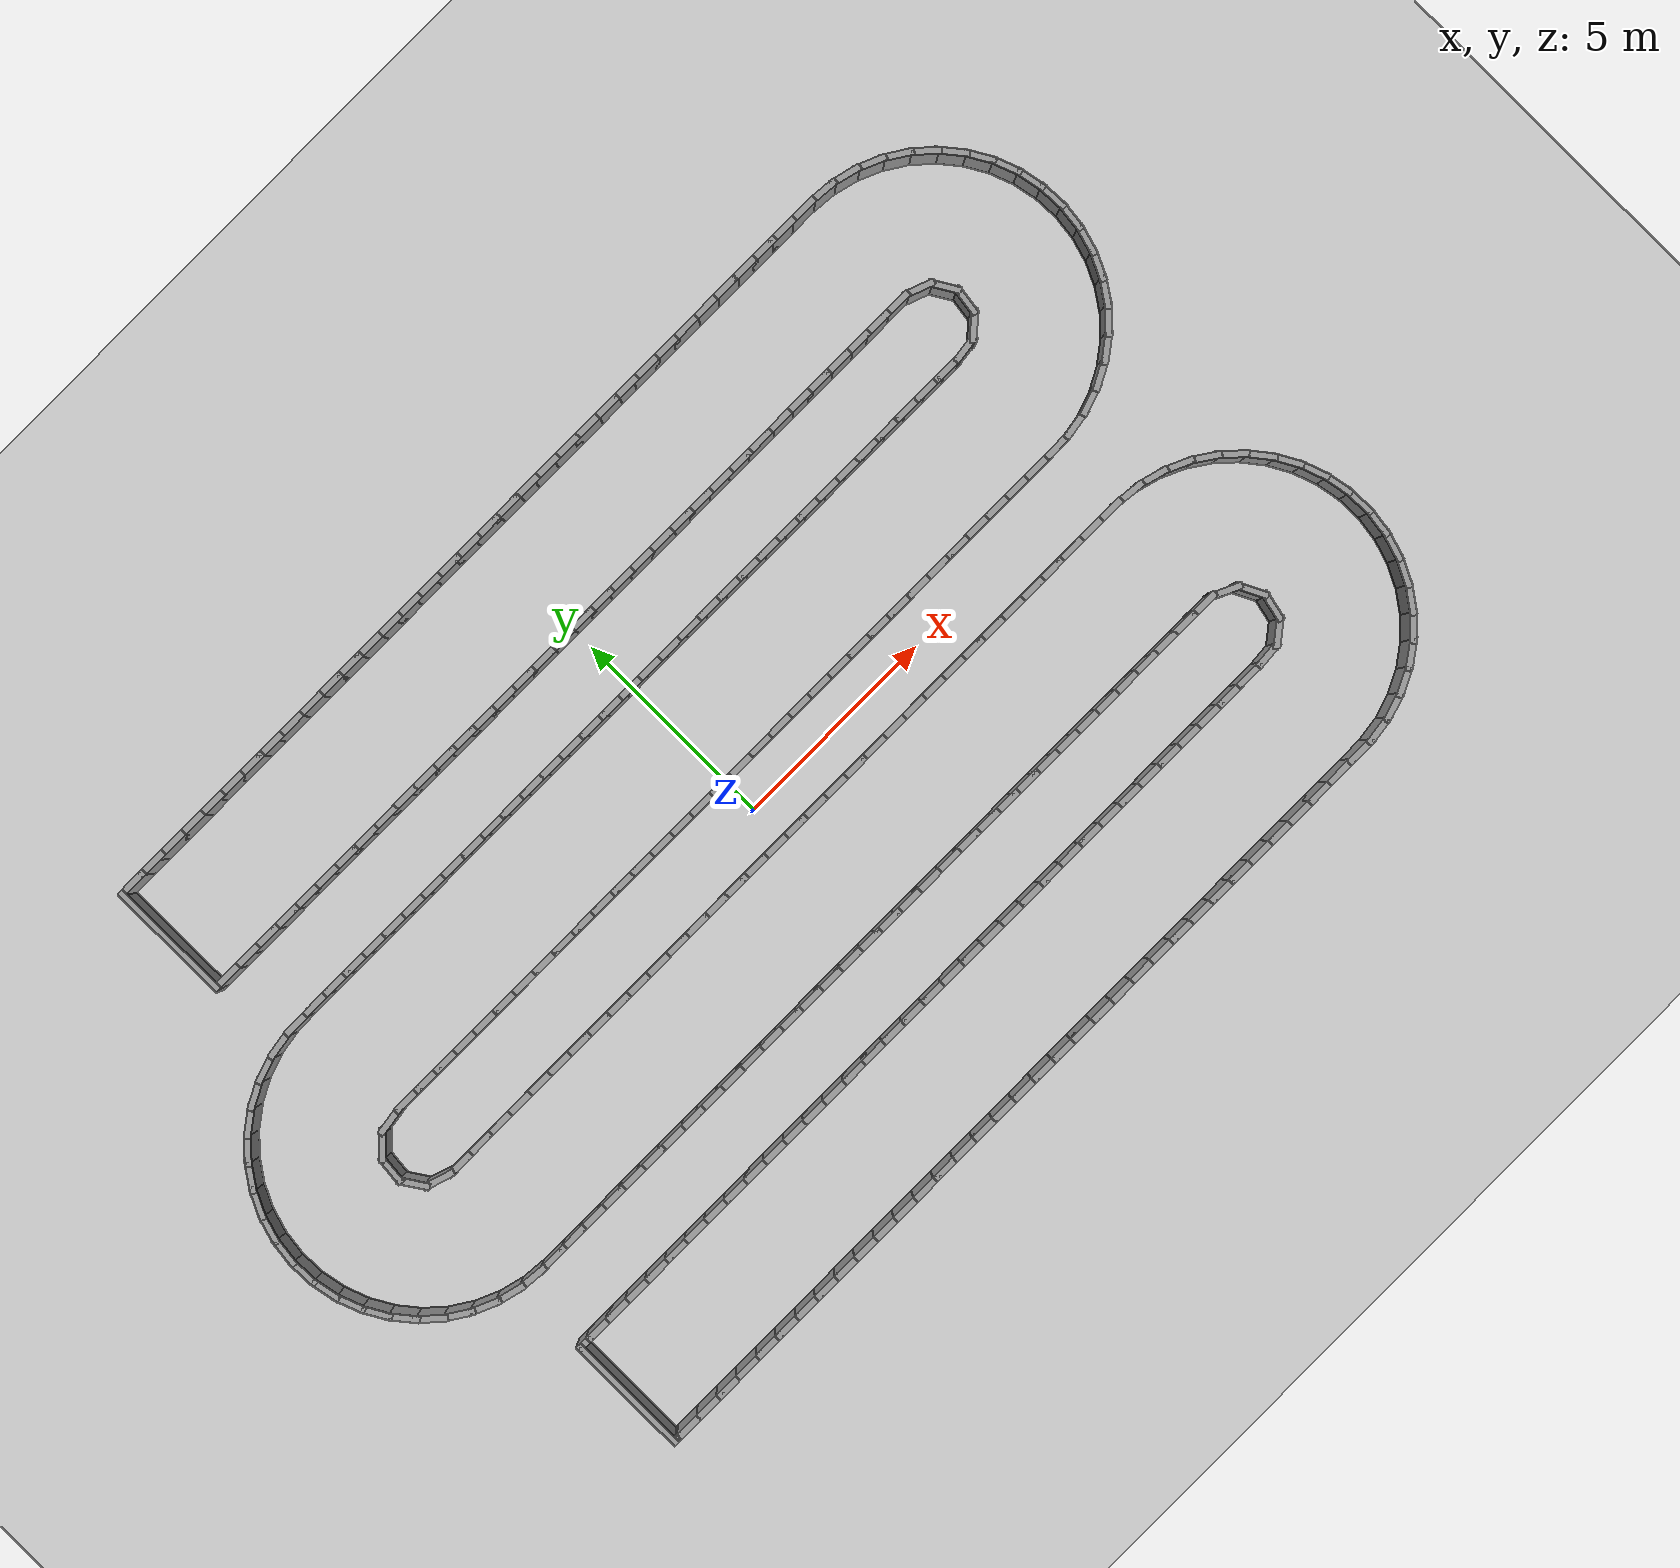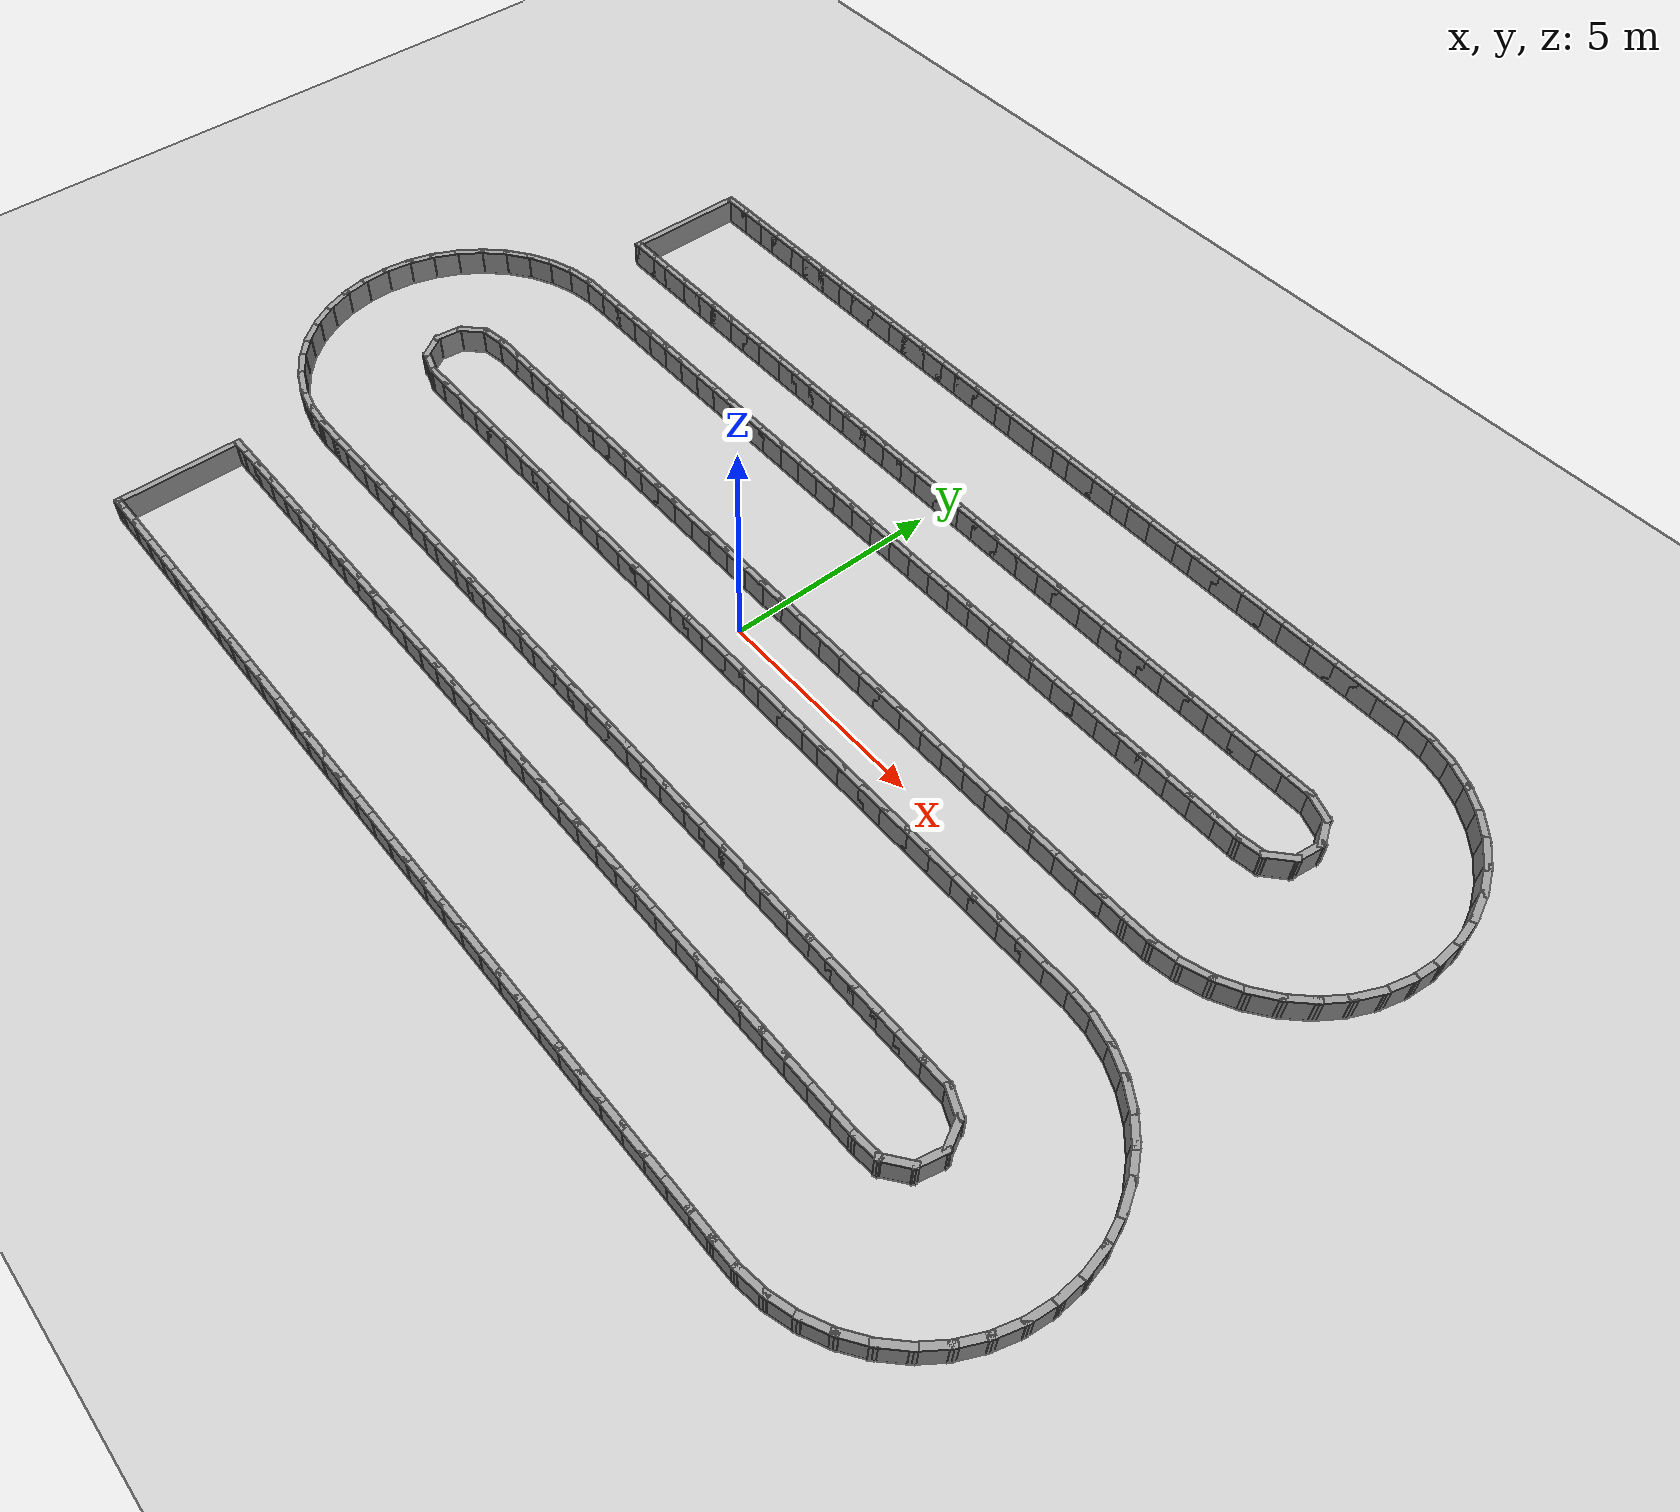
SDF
<?xml version="1.0" ?>
<sdf version='1.7'>
  <world name='default'>
    <plugin name='gazebo_ros_state' filename='libgazebo_ros_state.so'>
      <ros>
        <namespace>/</namespace>
      </ros>
      <update_rate>1000.0</update_rate>
    </plugin>

    <light name='sun' type='directional'>
      <cast_shadows>1</cast_shadows>
      <pose>0 0 10 0 -0 0</pose>
      <diffuse>0.8 0.8 0.8 1</diffuse>
      <specular>0.2 0.2 0.2 1</specular>
      <attenuation>
        <range>1000</range>
        <constant>0.9</constant>
        <linear>0.01</linear>
        <quadratic>0.001</quadratic>
      </attenuation>
      <direction>-0.5 0.1 -0.9</direction>
      <spot>
        <inner_angle>0</inner_angle>
        <outer_angle>0</outer_angle>
        <falloff>0</falloff>
      </spot>
    </light>
    <model name='ground_plane'>
      <static>1</static>
      <link name='link'>
        <collision name='collision'>
          <geometry>
            <plane>
              <normal>0 0 1</normal>
              <size>100 100</size>
            </plane>
          </geometry>
          <surface>
            <friction>
              <ode>
                <mu>100</mu>
                <mu2>50</mu2>
              </ode>
              <torsional>
                <ode/>
              </torsional>
            </friction>
            <contact>
              <ode/>
            </contact>
            <bounce/>
          </surface>
          <max_contacts>10</max_contacts>
        </collision>
        <visual name='visual'>
          <cast_shadows>0</cast_shadows>
          <geometry>
            <plane>
              <normal>0 0 1</normal>
              <size>100 100</size>
            </plane>
          </geometry>
          <material>
            <script>
              <uri>file://media/materials/scripts/gazebo.material</uri>
              <name>Gazebo/Grey</name>
            </script>
          </material>
        </visual>
        <self_collide>0</self_collide>
        <enable_wind>0</enable_wind>
        <kinematic>0</kinematic>
      </link>
    </model>
    <gravity>0 0 -9.8</gravity>
    <magnetic_field>6e-06 2.3e-05 -4.2e-05</magnetic_field>
    <atmosphere type='adiabatic'/>
    <physics type='ode'>
      <max_step_size>0.001</max_step_size>
      <real_time_factor>1</real_time_factor>
      <real_time_update_rate>1000</real_time_update_rate>
    </physics>
    <scene>
      <ambient>0.4 0.4 0.4 1</ambient>
      <background>0.7 0.7 0.7 1</background>
      <shadows>1</shadows>
    </scene>
    <audio>
      <device>default</device>
    </audio>
    <wind/>
    <spherical_coordinates>
      <surface_model>EARTH_WGS84</surface_model>
      <latitude_deg>0</latitude_deg>
      <longitude_deg>0</longitude_deg>
      <elevation>0</elevation>
      <heading_deg>0</heading_deg>
    </spherical_coordinates>
  <model name='rand_serp_00'>
    <pose>0 0 0 0 -0 0</pose>
    <link name='Wall_0'>
      <collision name='Wall_0_Collision'>
        <geometry><box><size>0.7500 0.1500 0.6000</size></box></geometry>
        <pose>0 0 0.3000 0 -0 0</pose>
      </collision>
      <visual name='Wall_0_Visual'>
        <pose>0 0 0.3000 0 -0 0</pose>
        <geometry><box><size>0.7500 0.1500 0.6000</size></box></geometry>
        <material>
          <script>
            <uri>file://media/materials/scripts/gazebo.material</uri>
            <name>Gazebo/Grey</name>
          </script>
          <ambient>1 1 1 1</ambient>
        </material>
      </visual>
      <pose>-10.5433 8.3501 0 0 -0 0.00000</pose>
    </link>
    <link name='Wall_1'>
      <collision name='Wall_1_Collision'>
        <geometry><box><size>0.7500 0.1500 0.6000</size></box></geometry>
        <pose>0 0 0.3000 0 -0 0</pose>
      </collision>
      <visual name='Wall_1_Visual'>
        <pose>0 0 0.3000 0 -0 0</pose>
        <geometry><box><size>0.7500 0.1500 0.6000</size></box></geometry>
        <material>
          <script>
            <uri>file://media/materials/scripts/gazebo.material</uri>
            <name>Gazebo/Grey</name>
          </script>
          <ambient>1 1 1 1</ambient>
        </material>
      </visual>
      <pose>-9.9433 8.3501 0 0 -0 0.00000</pose>
    </link>
    <link name='Wall_2'>
      <collision name='Wall_2_Collision'>
        <geometry><box><size>0.7500 0.1500 0.6000</size></box></geometry>
        <pose>0 0 0.3000 0 -0 0</pose>
      </collision>
      <visual name='Wall_2_Visual'>
        <pose>0 0 0.3000 0 -0 0</pose>
        <geometry><box><size>0.7500 0.1500 0.6000</size></box></geometry>
        <material>
          <script>
            <uri>file://media/materials/scripts/gazebo.material</uri>
            <name>Gazebo/Grey</name>
          </script>
          <ambient>1 1 1 1</ambient>
        </material>
      </visual>
      <pose>-9.3433 8.3501 0 0 -0 0.00000</pose>
    </link>
    <link name='Wall_3'>
      <collision name='Wall_3_Collision'>
        <geometry><box><size>0.7500 0.1500 0.6000</size></box></geometry>
        <pose>0 0 0.3000 0 -0 0</pose>
      </collision>
      <visual name='Wall_3_Visual'>
        <pose>0 0 0.3000 0 -0 0</pose>
        <geometry><box><size>0.7500 0.1500 0.6000</size></box></geometry>
        <material>
          <script>
            <uri>file://media/materials/scripts/gazebo.material</uri>
            <name>Gazebo/Grey</name>
          </script>
          <ambient>1 1 1 1</ambient>
        </material>
      </visual>
      <pose>-8.7433 8.3501 0 0 -0 0.00000</pose>
    </link>
    <link name='Wall_4'>
      <collision name='Wall_4_Collision'>
        <geometry><box><size>0.7500 0.1500 0.6000</size></box></geometry>
        <pose>0 0 0.3000 0 -0 0</pose>
      </collision>
      <visual name='Wall_4_Visual'>
        <pose>0 0 0.3000 0 -0 0</pose>
        <geometry><box><size>0.7500 0.1500 0.6000</size></box></geometry>
        <material>
          <script>
            <uri>file://media/materials/scripts/gazebo.material</uri>
            <name>Gazebo/Grey</name>
          </script>
          <ambient>1 1 1 1</ambient>
        </material>
      </visual>
      <pose>-8.1433 8.3501 0 0 -0 0.00000</pose>
    </link>
    <link name='Wall_5'>
      <collision name='Wall_5_Collision'>
        <geometry><box><size>0.7500 0.1500 0.6000</size></box></geometry>
        <pose>0 0 0.3000 0 -0 0</pose>
      </collision>
      <visual name='Wall_5_Visual'>
        <pose>0 0 0.3000 0 -0 0</pose>
        <geometry><box><size>0.7500 0.1500 0.6000</size></box></geometry>
        <material>
          <script>
            <uri>file://media/materials/scripts/gazebo.material</uri>
            <name>Gazebo/Grey</name>
          </script>
          <ambient>1 1 1 1</ambient>
        </material>
      </visual>
      <pose>-7.5433 8.3501 0 0 -0 0.00000</pose>
    </link>
    <link name='Wall_6'>
      <collision name='Wall_6_Collision'>
        <geometry><box><size>0.7500 0.1500 0.6000</size></box></geometry>
        <pose>0 0 0.3000 0 -0 0</pose>
      </collision>
      <visual name='Wall_6_Visual'>
        <pose>0 0 0.3000 0 -0 0</pose>
        <geometry><box><size>0.7500 0.1500 0.6000</size></box></geometry>
        <material>
          <script>
            <uri>file://media/materials/scripts/gazebo.material</uri>
            <name>Gazebo/Grey</name>
          </script>
          <ambient>1 1 1 1</ambient>
        </material>
      </visual>
      <pose>-6.9433 8.3501 0 0 -0 0.00000</pose>
    </link>
    <link name='Wall_7'>
      <collision name='Wall_7_Collision'>
        <geometry><box><size>0.7500 0.1500 0.6000</size></box></geometry>
        <pose>0 0 0.3000 0 -0 0</pose>
      </collision>
      <visual name='Wall_7_Visual'>
        <pose>0 0 0.3000 0 -0 0</pose>
        <geometry><box><size>0.7500 0.1500 0.6000</size></box></geometry>
        <material>
          <script>
            <uri>file://media/materials/scripts/gazebo.material</uri>
            <name>Gazebo/Grey</name>
          </script>
          <ambient>1 1 1 1</ambient>
        </material>
      </visual>
      <pose>-6.3433 8.3501 0 0 -0 0.00000</pose>
    </link>
    <link name='Wall_8'>
      <collision name='Wall_8_Collision'>
        <geometry><box><size>0.7500 0.1500 0.6000</size></box></geometry>
        <pose>0 0 0.3000 0 -0 0</pose>
      </collision>
      <visual name='Wall_8_Visual'>
        <pose>0 0 0.3000 0 -0 0</pose>
        <geometry><box><size>0.7500 0.1500 0.6000</size></box></geometry>
        <material>
          <script>
            <uri>file://media/materials/scripts/gazebo.material</uri>
            <name>Gazebo/Grey</name>
          </script>
          <ambient>1 1 1 1</ambient>
        </material>
      </visual>
      <pose>-5.7433 8.3501 0 0 -0 0.00000</pose>
    </link>
    <link name='Wall_9'>
      <collision name='Wall_9_Collision'>
        <geometry><box><size>0.7500 0.1500 0.6000</size></box></geometry>
        <pose>0 0 0.3000 0 -0 0</pose>
      </collision>
      <visual name='Wall_9_Visual'>
        <pose>0 0 0.3000 0 -0 0</pose>
        <geometry><box><size>0.7500 0.1500 0.6000</size></box></geometry>
        <material>
          <script>
            <uri>file://media/materials/scripts/gazebo.material</uri>
            <name>Gazebo/Grey</name>
          </script>
          <ambient>1 1 1 1</ambient>
        </material>
      </visual>
      <pose>-5.1433 8.3501 0 0 -0 0.00000</pose>
    </link>
    <link name='Wall_10'>
      <collision name='Wall_10_Collision'>
        <geometry><box><size>0.7500 0.1500 0.6000</size></box></geometry>
        <pose>0 0 0.3000 0 -0 0</pose>
      </collision>
      <visual name='Wall_10_Visual'>
        <pose>0 0 0.3000 0 -0 0</pose>
        <geometry><box><size>0.7500 0.1500 0.6000</size></box></geometry>
        <material>
          <script>
            <uri>file://media/materials/scripts/gazebo.material</uri>
            <name>Gazebo/Grey</name>
          </script>
          <ambient>1 1 1 1</ambient>
        </material>
      </visual>
      <pose>-4.5433 8.3501 0 0 -0 0.00000</pose>
    </link>
    <link name='Wall_11'>
      <collision name='Wall_11_Collision'>
        <geometry><box><size>0.7500 0.1500 0.6000</size></box></geometry>
        <pose>0 0 0.3000 0 -0 0</pose>
      </collision>
      <visual name='Wall_11_Visual'>
        <pose>0 0 0.3000 0 -0 0</pose>
        <geometry><box><size>0.7500 0.1500 0.6000</size></box></geometry>
        <material>
          <script>
            <uri>file://media/materials/scripts/gazebo.material</uri>
            <name>Gazebo/Grey</name>
          </script>
          <ambient>1 1 1 1</ambient>
        </material>
      </visual>
      <pose>-3.9433 8.3501 0 0 -0 0.00000</pose>
    </link>
    <link name='Wall_12'>
      <collision name='Wall_12_Collision'>
        <geometry><box><size>0.7500 0.1500 0.6000</size></box></geometry>
        <pose>0 0 0.3000 0 -0 0</pose>
      </collision>
      <visual name='Wall_12_Visual'>
        <pose>0 0 0.3000 0 -0 0</pose>
        <geometry><box><size>0.7500 0.1500 0.6000</size></box></geometry>
        <material>
          <script>
            <uri>file://media/materials/scripts/gazebo.material</uri>
            <name>Gazebo/Grey</name>
          </script>
          <ambient>1 1 1 1</ambient>
        </material>
      </visual>
      <pose>-3.3433 8.3501 0 0 -0 0.00000</pose>
    </link>
    <link name='Wall_13'>
      <collision name='Wall_13_Collision'>
        <geometry><box><size>0.7500 0.1500 0.6000</size></box></geometry>
        <pose>0 0 0.3000 0 -0 0</pose>
      </collision>
      <visual name='Wall_13_Visual'>
        <pose>0 0 0.3000 0 -0 0</pose>
        <geometry><box><size>0.7500 0.1500 0.6000</size></box></geometry>
        <material>
          <script>
            <uri>file://media/materials/scripts/gazebo.material</uri>
            <name>Gazebo/Grey</name>
          </script>
          <ambient>1 1 1 1</ambient>
        </material>
      </visual>
      <pose>-2.7433 8.3501 0 0 -0 0.00000</pose>
    </link>
    <link name='Wall_14'>
      <collision name='Wall_14_Collision'>
        <geometry><box><size>0.7500 0.1500 0.6000</size></box></geometry>
        <pose>0 0 0.3000 0 -0 0</pose>
      </collision>
      <visual name='Wall_14_Visual'>
        <pose>0 0 0.3000 0 -0 0</pose>
        <geometry><box><size>0.7500 0.1500 0.6000</size></box></geometry>
        <material>
          <script>
            <uri>file://media/materials/scripts/gazebo.material</uri>
            <name>Gazebo/Grey</name>
          </script>
          <ambient>1 1 1 1</ambient>
        </material>
      </visual>
      <pose>-2.1433 8.3501 0 0 -0 0.00000</pose>
    </link>
    <link name='Wall_15'>
      <collision name='Wall_15_Collision'>
        <geometry><box><size>0.7500 0.1500 0.6000</size></box></geometry>
        <pose>0 0 0.3000 0 -0 0</pose>
      </collision>
      <visual name='Wall_15_Visual'>
        <pose>0 0 0.3000 0 -0 0</pose>
        <geometry><box><size>0.7500 0.1500 0.6000</size></box></geometry>
        <material>
          <script>
            <uri>file://media/materials/scripts/gazebo.material</uri>
            <name>Gazebo/Grey</name>
          </script>
          <ambient>1 1 1 1</ambient>
        </material>
      </visual>
      <pose>-1.5433 8.3501 0 0 -0 0.00000</pose>
    </link>
    <link name='Wall_16'>
      <collision name='Wall_16_Collision'>
        <geometry><box><size>0.7500 0.1500 0.6000</size></box></geometry>
        <pose>0 0 0.3000 0 -0 0</pose>
      </collision>
      <visual name='Wall_16_Visual'>
        <pose>0 0 0.3000 0 -0 0</pose>
        <geometry><box><size>0.7500 0.1500 0.6000</size></box></geometry>
        <material>
          <script>
            <uri>file://media/materials/scripts/gazebo.material</uri>
            <name>Gazebo/Grey</name>
          </script>
          <ambient>1 1 1 1</ambient>
        </material>
      </visual>
      <pose>-0.9433 8.3501 0 0 -0 0.00000</pose>
    </link>
    <link name='Wall_17'>
      <collision name='Wall_17_Collision'>
        <geometry><box><size>0.7500 0.1500 0.6000</size></box></geometry>
        <pose>0 0 0.3000 0 -0 0</pose>
      </collision>
      <visual name='Wall_17_Visual'>
        <pose>0 0 0.3000 0 -0 0</pose>
        <geometry><box><size>0.7500 0.1500 0.6000</size></box></geometry>
        <material>
          <script>
            <uri>file://media/materials/scripts/gazebo.material</uri>
            <name>Gazebo/Grey</name>
          </script>
          <ambient>1 1 1 1</ambient>
        </material>
      </visual>
      <pose>-0.3433 8.3501 0 0 -0 0.00000</pose>
    </link>
    <link name='Wall_18'>
      <collision name='Wall_18_Collision'>
        <geometry><box><size>0.7500 0.1500 0.6000</size></box></geometry>
        <pose>0 0 0.3000 0 -0 0</pose>
      </collision>
      <visual name='Wall_18_Visual'>
        <pose>0 0 0.3000 0 -0 0</pose>
        <geometry><box><size>0.7500 0.1500 0.6000</size></box></geometry>
        <material>
          <script>
            <uri>file://media/materials/scripts/gazebo.material</uri>
            <name>Gazebo/Grey</name>
          </script>
          <ambient>1 1 1 1</ambient>
        </material>
      </visual>
      <pose>0.2567 8.3501 0 0 -0 0.00000</pose>
    </link>
    <link name='Wall_19'>
      <collision name='Wall_19_Collision'>
        <geometry><box><size>0.7500 0.1500 0.6000</size></box></geometry>
        <pose>0 0 0.3000 0 -0 0</pose>
      </collision>
      <visual name='Wall_19_Visual'>
        <pose>0 0 0.3000 0 -0 0</pose>
        <geometry><box><size>0.7500 0.1500 0.6000</size></box></geometry>
        <material>
          <script>
            <uri>file://media/materials/scripts/gazebo.material</uri>
            <name>Gazebo/Grey</name>
          </script>
          <ambient>1 1 1 1</ambient>
        </material>
      </visual>
      <pose>0.8567 8.3501 0 0 -0 0.00000</pose>
    </link>
    <link name='Wall_20'>
      <collision name='Wall_20_Collision'>
        <geometry><box><size>0.7500 0.1500 0.6000</size></box></geometry>
        <pose>0 0 0.3000 0 -0 0</pose>
      </collision>
      <visual name='Wall_20_Visual'>
        <pose>0 0 0.3000 0 -0 0</pose>
        <geometry><box><size>0.7500 0.1500 0.6000</size></box></geometry>
        <material>
          <script>
            <uri>file://media/materials/scripts/gazebo.material</uri>
            <name>Gazebo/Grey</name>
          </script>
          <ambient>1 1 1 1</ambient>
        </material>
      </visual>
      <pose>1.4567 8.3501 0 0 -0 0.00000</pose>
    </link>
    <link name='Wall_21'>
      <collision name='Wall_21_Collision'>
        <geometry><box><size>0.7500 0.1500 0.6000</size></box></geometry>
        <pose>0 0 0.3000 0 -0 0</pose>
      </collision>
      <visual name='Wall_21_Visual'>
        <pose>0 0 0.3000 0 -0 0</pose>
        <geometry><box><size>0.7500 0.1500 0.6000</size></box></geometry>
        <material>
          <script>
            <uri>file://media/materials/scripts/gazebo.material</uri>
            <name>Gazebo/Grey</name>
          </script>
          <ambient>1 1 1 1</ambient>
        </material>
      </visual>
      <pose>2.0567 8.3501 0 0 -0 0.00000</pose>
    </link>
    <link name='Wall_22'>
      <collision name='Wall_22_Collision'>
        <geometry><box><size>0.7500 0.1500 0.6000</size></box></geometry>
        <pose>0 0 0.3000 0 -0 0</pose>
      </collision>
      <visual name='Wall_22_Visual'>
        <pose>0 0 0.3000 0 -0 0</pose>
        <geometry><box><size>0.7500 0.1500 0.6000</size></box></geometry>
        <material>
          <script>
            <uri>file://media/materials/scripts/gazebo.material</uri>
            <name>Gazebo/Grey</name>
          </script>
          <ambient>1 1 1 1</ambient>
        </material>
      </visual>
      <pose>2.6567 8.3501 0 0 -0 0.00000</pose>
    </link>
    <link name='Wall_23'>
      <collision name='Wall_23_Collision'>
        <geometry><box><size>0.7500 0.1500 0.6000</size></box></geometry>
        <pose>0 0 0.3000 0 -0 0</pose>
      </collision>
      <visual name='Wall_23_Visual'>
        <pose>0 0 0.3000 0 -0 0</pose>
        <geometry><box><size>0.7500 0.1500 0.6000</size></box></geometry>
        <material>
          <script>
            <uri>file://media/materials/scripts/gazebo.material</uri>
            <name>Gazebo/Grey</name>
          </script>
          <ambient>1 1 1 1</ambient>
        </material>
      </visual>
      <pose>3.2567 8.3501 0 0 -0 0.00000</pose>
    </link>
    <link name='Wall_24'>
      <collision name='Wall_24_Collision'>
        <geometry><box><size>0.7500 0.1500 0.6000</size></box></geometry>
        <pose>0 0 0.3000 0 -0 0</pose>
      </collision>
      <visual name='Wall_24_Visual'>
        <pose>0 0 0.3000 0 -0 0</pose>
        <geometry><box><size>0.7500 0.1500 0.6000</size></box></geometry>
        <material>
          <script>
            <uri>file://media/materials/scripts/gazebo.material</uri>
            <name>Gazebo/Grey</name>
          </script>
          <ambient>1 1 1 1</ambient>
        </material>
      </visual>
      <pose>3.8567 8.3501 0 0 -0 0.00000</pose>
    </link>
    <link name='Wall_25'>
      <collision name='Wall_25_Collision'>
        <geometry><box><size>0.7500 0.1500 0.6000</size></box></geometry>
        <pose>0 0 0.3000 0 -0 0</pose>
      </collision>
      <visual name='Wall_25_Visual'>
        <pose>0 0 0.3000 0 -0 0</pose>
        <geometry><box><size>0.7500 0.1500 0.6000</size></box></geometry>
        <material>
          <script>
            <uri>file://media/materials/scripts/gazebo.material</uri>
            <name>Gazebo/Grey</name>
          </script>
          <ambient>1 1 1 1</ambient>
        </material>
      </visual>
      <pose>4.4567 8.3501 0 0 -0 0.00000</pose>
    </link>
    <link name='Wall_26'>
      <collision name='Wall_26_Collision'>
        <geometry><box><size>0.7500 0.1500 0.6000</size></box></geometry>
        <pose>0 0 0.3000 0 -0 0</pose>
      </collision>
      <visual name='Wall_26_Visual'>
        <pose>0 0 0.3000 0 -0 0</pose>
        <geometry><box><size>0.7500 0.1500 0.6000</size></box></geometry>
        <material>
          <script>
            <uri>file://media/materials/scripts/gazebo.material</uri>
            <name>Gazebo/Grey</name>
          </script>
          <ambient>1 1 1 1</ambient>
        </material>
      </visual>
      <pose>5.0567 8.3501 0 0 -0 0.00000</pose>
    </link>
    <link name='Wall_27'>
      <collision name='Wall_27_Collision'>
        <geometry><box><size>0.7500 0.1500 0.6000</size></box></geometry>
        <pose>0 0 0.3000 0 -0 0</pose>
      </collision>
      <visual name='Wall_27_Visual'>
        <pose>0 0 0.3000 0 -0 0</pose>
        <geometry><box><size>0.7500 0.1500 0.6000</size></box></geometry>
        <material>
          <script>
            <uri>file://media/materials/scripts/gazebo.material</uri>
            <name>Gazebo/Grey</name>
          </script>
          <ambient>1 1 1 1</ambient>
        </material>
      </visual>
      <pose>5.6567 8.3501 0 0 -0 0.00000</pose>
    </link>
    <link name='Wall_28'>
      <collision name='Wall_28_Collision'>
        <geometry><box><size>0.7500 0.1500 0.6000</size></box></geometry>
        <pose>0 0 0.3000 0 -0 0</pose>
      </collision>
      <visual name='Wall_28_Visual'>
        <pose>0 0 0.3000 0 -0 0</pose>
        <geometry><box><size>0.7500 0.1500 0.6000</size></box></geometry>
        <material>
          <script>
            <uri>file://media/materials/scripts/gazebo.material</uri>
            <name>Gazebo/Grey</name>
          </script>
          <ambient>1 1 1 1</ambient>
        </material>
      </visual>
      <pose>6.2567 8.3501 0 0 -0 0.00000</pose>
    </link>
    <link name='Wall_29'>
      <collision name='Wall_29_Collision'>
        <geometry><box><size>0.7500 0.1500 0.6000</size></box></geometry>
        <pose>0 0 0.3000 0 -0 0</pose>
      </collision>
      <visual name='Wall_29_Visual'>
        <pose>0 0 0.3000 0 -0 0</pose>
        <geometry><box><size>0.7500 0.1500 0.6000</size></box></geometry>
        <material>
          <script>
            <uri>file://media/materials/scripts/gazebo.material</uri>
            <name>Gazebo/Grey</name>
          </script>
          <ambient>1 1 1 1</ambient>
        </material>
      </visual>
      <pose>6.8567 8.3501 0 0 -0 0.00000</pose>
    </link>
    <link name='Wall_30'>
      <collision name='Wall_30_Collision'>
        <geometry><box><size>0.7500 0.1500 0.6000</size></box></geometry>
        <pose>0 0 0.3000 0 -0 0</pose>
      </collision>
      <visual name='Wall_30_Visual'>
        <pose>0 0 0.3000 0 -0 0</pose>
        <geometry><box><size>0.7500 0.1500 0.6000</size></box></geometry>
        <material>
          <script>
            <uri>file://media/materials/scripts/gazebo.material</uri>
            <name>Gazebo/Grey</name>
          </script>
          <ambient>1 1 1 1</ambient>
        </material>
      </visual>
      <pose>7.4567 8.3501 0 0 -0 0.00000</pose>
    </link>
    <link name='Wall_31'>
      <collision name='Wall_31_Collision'>
        <geometry><box><size>0.7500 0.1500 0.6000</size></box></geometry>
        <pose>0 0 0.3000 0 -0 0</pose>
      </collision>
      <visual name='Wall_31_Visual'>
        <pose>0 0 0.3000 0 -0 0</pose>
        <geometry><box><size>0.7500 0.1500 0.6000</size></box></geometry>
        <material>
          <script>
            <uri>file://media/materials/scripts/gazebo.material</uri>
            <name>Gazebo/Grey</name>
          </script>
          <ambient>1 1 1 1</ambient>
        </material>
      </visual>
      <pose>8.0567 8.3501 0 0 -0 0.00000</pose>
    </link>
    <link name='Wall_32'>
      <collision name='Wall_32_Collision'>
        <geometry><box><size>0.7500 0.1500 0.6000</size></box></geometry>
        <pose>0 0 0.3000 0 -0 0</pose>
      </collision>
      <visual name='Wall_32_Visual'>
        <pose>0 0 0.3000 0 -0 0</pose>
        <geometry><box><size>0.7500 0.1500 0.6000</size></box></geometry>
        <material>
          <script>
            <uri>file://media/materials/scripts/gazebo.material</uri>
            <name>Gazebo/Grey</name>
          </script>
          <ambient>1 1 1 1</ambient>
        </material>
      </visual>
      <pose>8.6567 8.3501 0 0 -0 0.00000</pose>
    </link>
    <link name='Wall_33'>
      <collision name='Wall_33_Collision'>
        <geometry><box><size>0.7500 0.1500 0.6000</size></box></geometry>
        <pose>0 0 0.3000 0 -0 0</pose>
      </collision>
      <visual name='Wall_33_Visual'>
        <pose>0 0 0.3000 0 -0 0</pose>
        <geometry><box><size>0.7500 0.1500 0.6000</size></box></geometry>
        <material>
          <script>
            <uri>file://media/materials/scripts/gazebo.material</uri>
            <name>Gazebo/Grey</name>
          </script>
          <ambient>1 1 1 1</ambient>
        </material>
      </visual>
      <pose>9.2567 8.3501 0 0 -0 0.00000</pose>
    </link>
    <link name='Wall_34'>
      <collision name='Wall_34_Collision'>
        <geometry><box><size>0.7500 0.1500 0.6000</size></box></geometry>
        <pose>0 0 0.3000 0 -0 0</pose>
      </collision>
      <visual name='Wall_34_Visual'>
        <pose>0 0 0.3000 0 -0 0</pose>
        <geometry><box><size>0.7500 0.1500 0.6000</size></box></geometry>
        <material>
          <script>
            <uri>file://media/materials/scripts/gazebo.material</uri>
            <name>Gazebo/Grey</name>
          </script>
          <ambient>1 1 1 1</ambient>
        </material>
      </visual>
      <pose>9.8567 8.3500 0 0 -0 -0.00021</pose>
    </link>
    <link name='Wall_35'>
      <collision name='Wall_35_Collision'>
        <geometry><box><size>0.7494 0.1500 0.6000</size></box></geometry>
        <pose>0 0 0.3000 0 -0 0</pose>
      </collision>
      <visual name='Wall_35_Visual'>
        <pose>0 0 0.3000 0 -0 0</pose>
        <geometry><box><size>0.7494 0.1500 0.6000</size></box></geometry>
        <material>
          <script>
            <uri>file://media/materials/scripts/gazebo.material</uri>
            <name>Gazebo/Grey</name>
          </script>
          <ambient>1 1 1 1</ambient>
        </material>
      </visual>
      <pose>10.4553 8.3247 0 0 -0 -0.08430</pose>
    </link>
    <link name='Wall_36'>
      <collision name='Wall_36_Collision'>
        <geometry><box><size>0.7493 0.1500 0.6000</size></box></geometry>
        <pose>0 0 0.3000 0 -0 0</pose>
      </collision>
      <visual name='Wall_36_Visual'>
        <pose>0 0 0.3000 0 -0 0</pose>
        <geometry><box><size>0.7493 0.1500 0.6000</size></box></geometry>
        <material>
          <script>
            <uri>file://media/materials/scripts/gazebo.material</uri>
            <name>Gazebo/Grey</name>
          </script>
          <ambient>1 1 1 1</ambient>
        </material>
      </visual>
      <pose>11.0446 8.2269 0 0 -0 -0.24476</pose>
    </link>
    <link name='Wall_37'>
      <collision name='Wall_37_Collision'>
        <geometry><box><size>0.7493 0.1500 0.6000</size></box></geometry>
        <pose>0 0 0.3000 0 -0 0</pose>
      </collision>
      <visual name='Wall_37_Visual'>
        <pose>0 0 0.3000 0 -0 0</pose>
        <geometry><box><size>0.7493 0.1500 0.6000</size></box></geometry>
        <material>
          <script>
            <uri>file://media/materials/scripts/gazebo.material</uri>
            <name>Gazebo/Grey</name>
          </script>
          <ambient>1 1 1 1</ambient>
        </material>
      </visual>
      <pose>11.6107 8.0361 0 0 -0 -0.40544</pose>
    </link>
    <link name='Wall_38'>
      <collision name='Wall_38_Collision'>
        <geometry><box><size>0.7493 0.1500 0.6000</size></box></geometry>
        <pose>0 0 0.3000 0 -0 0</pose>
      </collision>
      <visual name='Wall_38_Visual'>
        <pose>0 0 0.3000 0 -0 0</pose>
        <geometry><box><size>0.7493 0.1500 0.6000</size></box></geometry>
        <material>
          <script>
            <uri>file://media/materials/scripts/gazebo.material</uri>
            <name>Gazebo/Grey</name>
          </script>
          <ambient>1 1 1 1</ambient>
        </material>
      </visual>
      <pose>12.1390 7.7572 0 0 -0 -0.56612</pose>
    </link>
    <link name='Wall_39'>
      <collision name='Wall_39_Collision'>
        <geometry><box><size>0.7493 0.1500 0.6000</size></box></geometry>
        <pose>0 0 0.3000 0 -0 0</pose>
      </collision>
      <visual name='Wall_39_Visual'>
        <pose>0 0 0.3000 0 -0 0</pose>
        <geometry><box><size>0.7493 0.1500 0.6000</size></box></geometry>
        <material>
          <script>
            <uri>file://media/materials/scripts/gazebo.material</uri>
            <name>Gazebo/Grey</name>
          </script>
          <ambient>1 1 1 1</ambient>
        </material>
      </visual>
      <pose>12.6158 7.3973 0 0 -0 -0.72681</pose>
    </link>
    <link name='Wall_40'>
      <collision name='Wall_40_Collision'>
        <geometry><box><size>0.7493 0.1500 0.6000</size></box></geometry>
        <pose>0 0 0.3000 0 -0 0</pose>
      </collision>
      <visual name='Wall_40_Visual'>
        <pose>0 0 0.3000 0 -0 0</pose>
        <geometry><box><size>0.7493 0.1500 0.6000</size></box></geometry>
        <material>
          <script>
            <uri>file://media/materials/scripts/gazebo.material</uri>
            <name>Gazebo/Grey</name>
          </script>
          <ambient>1 1 1 1</ambient>
        </material>
      </visual>
      <pose>13.0289 6.9658 0 0 -0 -0.88749</pose>
    </link>
    <link name='Wall_41'>
      <collision name='Wall_41_Collision'>
        <geometry><box><size>0.7493 0.1500 0.6000</size></box></geometry>
        <pose>0 0 0.3000 0 -0 0</pose>
      </collision>
      <visual name='Wall_41_Visual'>
        <pose>0 0 0.3000 0 -0 0</pose>
        <geometry><box><size>0.7493 0.1500 0.6000</size></box></geometry>
        <material>
          <script>
            <uri>file://media/materials/scripts/gazebo.material</uri>
            <name>Gazebo/Grey</name>
          </script>
          <ambient>1 1 1 1</ambient>
        </material>
      </visual>
      <pose>13.3677 6.4738 0 0 -0 -1.04818</pose>
    </link>
    <link name='Wall_42'>
      <collision name='Wall_42_Collision'>
        <geometry><box><size>0.7493 0.1500 0.6000</size></box></geometry>
        <pose>0 0 0.3000 0 -0 0</pose>
      </collision>
      <visual name='Wall_42_Visual'>
        <pose>0 0 0.3000 0 -0 0</pose>
        <geometry><box><size>0.7493 0.1500 0.6000</size></box></geometry>
        <material>
          <script>
            <uri>file://media/materials/scripts/gazebo.material</uri>
            <name>Gazebo/Grey</name>
          </script>
          <ambient>1 1 1 1</ambient>
        </material>
      </visual>
      <pose>13.6234 5.9339 0 0 -0 -1.20886</pose>
    </link>
    <link name='Wall_43'>
      <collision name='Wall_43_Collision'>
        <geometry><box><size>0.7493 0.1500 0.6000</size></box></geometry>
        <pose>0 0 0.3000 0 -0 0</pose>
      </collision>
      <visual name='Wall_43_Visual'>
        <pose>0 0 0.3000 0 -0 0</pose>
        <geometry><box><size>0.7493 0.1500 0.6000</size></box></geometry>
        <material>
          <script>
            <uri>file://media/materials/scripts/gazebo.material</uri>
            <name>Gazebo/Grey</name>
          </script>
          <ambient>1 1 1 1</ambient>
        </material>
      </visual>
      <pose>13.7893 5.3601 0 0 -0 -1.36954</pose>
    </link>
    <link name='Wall_44'>
      <collision name='Wall_44_Collision'>
        <geometry><box><size>0.7493 0.1500 0.6000</size></box></geometry>
        <pose>0 0 0.3000 0 -0 0</pose>
      </collision>
      <visual name='Wall_44_Visual'>
        <pose>0 0 0.3000 0 -0 0</pose>
        <geometry><box><size>0.7493 0.1500 0.6000</size></box></geometry>
        <material>
          <script>
            <uri>file://media/materials/scripts/gazebo.material</uri>
            <name>Gazebo/Grey</name>
          </script>
          <ambient>1 1 1 1</ambient>
        </material>
      </visual>
      <pose>13.8614 4.7671 0 0 -0 -1.53023</pose>
    </link>
    <link name='Wall_45'>
      <collision name='Wall_45_Collision'>
        <geometry><box><size>0.7493 0.1500 0.6000</size></box></geometry>
        <pose>0 0 0.3000 0 -0 0</pose>
      </collision>
      <visual name='Wall_45_Visual'>
        <pose>0 0 0.3000 0 -0 0</pose>
        <geometry><box><size>0.7493 0.1500 0.6000</size></box></geometry>
        <material>
          <script>
            <uri>file://media/materials/scripts/gazebo.material</uri>
            <name>Gazebo/Grey</name>
          </script>
          <ambient>1 1 1 1</ambient>
        </material>
      </visual>
      <pose>13.8376 4.1703 0 0 -0 -1.69091</pose>
    </link>
    <link name='Wall_46'>
      <collision name='Wall_46_Collision'>
        <geometry><box><size>0.7493 0.1500 0.6000</size></box></geometry>
        <pose>0 0 0.3000 0 -0 0</pose>
      </collision>
      <visual name='Wall_46_Visual'>
        <pose>0 0 0.3000 0 -0 0</pose>
        <geometry><box><size>0.7493 0.1500 0.6000</size></box></geometry>
        <material>
          <script>
            <uri>file://media/materials/scripts/gazebo.material</uri>
            <name>Gazebo/Grey</name>
          </script>
          <ambient>1 1 1 1</ambient>
        </material>
      </visual>
      <pose>13.7187 3.5849 0 0 -0 -1.85160</pose>
    </link>
    <link name='Wall_47'>
      <collision name='Wall_47_Collision'>
        <geometry><box><size>0.7493 0.1500 0.6000</size></box></geometry>
        <pose>0 0 0.3000 0 -0 0</pose>
      </collision>
      <visual name='Wall_47_Visual'>
        <pose>0 0 0.3000 0 -0 0</pose>
        <geometry><box><size>0.7493 0.1500 0.6000</size></box></geometry>
        <material>
          <script>
            <uri>file://media/materials/scripts/gazebo.material</uri>
            <name>Gazebo/Grey</name>
          </script>
          <ambient>1 1 1 1</ambient>
        </material>
      </visual>
      <pose>13.5076 3.0261 0 0 -0 -2.01228</pose>
    </link>
    <link name='Wall_48'>
      <collision name='Wall_48_Collision'>
        <geometry><box><size>0.7493 0.1500 0.6000</size></box></geometry>
        <pose>0 0 0.3000 0 -0 0</pose>
      </collision>
      <visual name='Wall_48_Visual'>
        <pose>0 0 0.3000 0 -0 0</pose>
        <geometry><box><size>0.7493 0.1500 0.6000</size></box></geometry>
        <material>
          <script>
            <uri>file://media/materials/scripts/gazebo.material</uri>
            <name>Gazebo/Grey</name>
          </script>
          <ambient>1 1 1 1</ambient>
        </material>
      </visual>
      <pose>13.2099 2.5082 0 0 -0 -2.17297</pose>
    </link>
    <link name='Wall_49'>
      <collision name='Wall_49_Collision'>
        <geometry><box><size>0.7493 0.1500 0.6000</size></box></geometry>
        <pose>0 0 0.3000 0 -0 0</pose>
      </collision>
      <visual name='Wall_49_Visual'>
        <pose>0 0 0.3000 0 -0 0</pose>
        <geometry><box><size>0.7493 0.1500 0.6000</size></box></geometry>
        <material>
          <script>
            <uri>file://media/materials/scripts/gazebo.material</uri>
            <name>Gazebo/Grey</name>
          </script>
          <ambient>1 1 1 1</ambient>
        </material>
      </visual>
      <pose>12.8331 2.0447 0 0 -0 -2.33365</pose>
    </link>
    <link name='Wall_50'>
      <collision name='Wall_50_Collision'>
        <geometry><box><size>0.7493 0.1500 0.6000</size></box></geometry>
        <pose>0 0 0.3000 0 -0 0</pose>
      </collision>
      <visual name='Wall_50_Visual'>
        <pose>0 0 0.3000 0 -0 0</pose>
        <geometry><box><size>0.7493 0.1500 0.6000</size></box></geometry>
        <material>
          <script>
            <uri>file://media/materials/scripts/gazebo.material</uri>
            <name>Gazebo/Grey</name>
          </script>
          <ambient>1 1 1 1</ambient>
        </material>
      </visual>
      <pose>12.3870 1.6474 0 0 -0 -2.49433</pose>
    </link>
    <link name='Wall_51'>
      <collision name='Wall_51_Collision'>
        <geometry><box><size>0.7493 0.1500 0.6000</size></box></geometry>
        <pose>0 0 0.3000 0 -0 0</pose>
      </collision>
      <visual name='Wall_51_Visual'>
        <pose>0 0 0.3000 0 -0 0</pose>
        <geometry><box><size>0.7493 0.1500 0.6000</size></box></geometry>
        <material>
          <script>
            <uri>file://media/materials/scripts/gazebo.material</uri>
            <name>Gazebo/Grey</name>
          </script>
          <ambient>1 1 1 1</ambient>
        </material>
      </visual>
      <pose>11.8831 1.3266 0 0 -0 -2.65502</pose>
    </link>
    <link name='Wall_52'>
      <collision name='Wall_52_Collision'>
        <geometry><box><size>0.7493 0.1500 0.6000</size></box></geometry>
        <pose>0 0 0.3000 0 -0 0</pose>
      </collision>
      <visual name='Wall_52_Visual'>
        <pose>0 0 0.3000 0 -0 0</pose>
        <geometry><box><size>0.7493 0.1500 0.6000</size></box></geometry>
        <material>
          <script>
            <uri>file://media/materials/scripts/gazebo.material</uri>
            <name>Gazebo/Grey</name>
          </script>
          <ambient>1 1 1 1</ambient>
        </material>
      </visual>
      <pose>11.3343 1.0905 0 0 -0 -2.81570</pose>
    </link>
    <link name='Wall_53'>
      <collision name='Wall_53_Collision'>
        <geometry><box><size>0.7493 0.1500 0.6000</size></box></geometry>
        <pose>0 0 0.3000 0 -0 0</pose>
      </collision>
      <visual name='Wall_53_Visual'>
        <pose>0 0 0.3000 0 -0 0</pose>
        <geometry><box><size>0.7493 0.1500 0.6000</size></box></geometry>
        <material>
          <script>
            <uri>file://media/materials/scripts/gazebo.material</uri>
            <name>Gazebo/Grey</name>
          </script>
          <ambient>1 1 1 1</ambient>
        </material>
      </visual>
      <pose>10.7548 0.9453 0 0 -0 -2.97639</pose>
    </link>
    <link name='Wall_54'>
      <collision name='Wall_54_Collision'>
        <geometry><box><size>0.7498 0.1500 0.6000</size></box></geometry>
        <pose>0 0 0.3000 0 -0 0</pose>
      </collision>
      <visual name='Wall_54_Visual'>
        <pose>0 0 0.3000 0 -0 0</pose>
        <geometry><box><size>0.7498 0.1500 0.6000</size></box></geometry>
        <material>
          <script>
            <uri>file://media/materials/scripts/gazebo.material</uri>
            <name>Gazebo/Grey</name>
          </script>
          <ambient>1 1 1 1</ambient>
        </material>
      </visual>
      <pose>10.1595 0.8892 0 0 -0 -3.11871</pose>
    </link>
    <link name='Wall_55'>
      <collision name='Wall_55_Collision'>
        <geometry><box><size>0.7500 0.1500 0.6000</size></box></geometry>
        <pose>0 0 0.3000 0 -0 0</pose>
      </collision>
      <visual name='Wall_55_Visual'>
        <pose>0 0 0.3000 0 -0 0</pose>
        <geometry><box><size>0.7500 0.1500 0.6000</size></box></geometry>
        <material>
          <script>
            <uri>file://media/materials/scripts/gazebo.material</uri>
            <name>Gazebo/Grey</name>
          </script>
          <ambient>1 1 1 1</ambient>
        </material>
      </visual>
      <pose>9.5596 0.8823 0 0 -0 3.14159</pose>
    </link>
    <link name='Wall_56'>
      <collision name='Wall_56_Collision'>
        <geometry><box><size>0.7500 0.1500 0.6000</size></box></geometry>
        <pose>0 0 0.3000 0 -0 0</pose>
      </collision>
      <visual name='Wall_56_Visual'>
        <pose>0 0 0.3000 0 -0 0</pose>
        <geometry><box><size>0.7500 0.1500 0.6000</size></box></geometry>
        <material>
          <script>
            <uri>file://media/materials/scripts/gazebo.material</uri>
            <name>Gazebo/Grey</name>
          </script>
          <ambient>1 1 1 1</ambient>
        </material>
      </visual>
      <pose>8.9596 0.8823 0 0 -0 3.14159</pose>
    </link>
    <link name='Wall_57'>
      <collision name='Wall_57_Collision'>
        <geometry><box><size>0.7500 0.1500 0.6000</size></box></geometry>
        <pose>0 0 0.3000 0 -0 0</pose>
      </collision>
      <visual name='Wall_57_Visual'>
        <pose>0 0 0.3000 0 -0 0</pose>
        <geometry><box><size>0.7500 0.1500 0.6000</size></box></geometry>
        <material>
          <script>
            <uri>file://media/materials/scripts/gazebo.material</uri>
            <name>Gazebo/Grey</name>
          </script>
          <ambient>1 1 1 1</ambient>
        </material>
      </visual>
      <pose>8.3596 0.8823 0 0 -0 3.14159</pose>
    </link>
    <link name='Wall_58'>
      <collision name='Wall_58_Collision'>
        <geometry><box><size>0.7500 0.1500 0.6000</size></box></geometry>
        <pose>0 0 0.3000 0 -0 0</pose>
      </collision>
      <visual name='Wall_58_Visual'>
        <pose>0 0 0.3000 0 -0 0</pose>
        <geometry><box><size>0.7500 0.1500 0.6000</size></box></geometry>
        <material>
          <script>
            <uri>file://media/materials/scripts/gazebo.material</uri>
            <name>Gazebo/Grey</name>
          </script>
          <ambient>1 1 1 1</ambient>
        </material>
      </visual>
      <pose>7.7596 0.8823 0 0 -0 3.14159</pose>
    </link>
    <link name='Wall_59'>
      <collision name='Wall_59_Collision'>
        <geometry><box><size>0.7500 0.1500 0.6000</size></box></geometry>
        <pose>0 0 0.3000 0 -0 0</pose>
      </collision>
      <visual name='Wall_59_Visual'>
        <pose>0 0 0.3000 0 -0 0</pose>
        <geometry><box><size>0.7500 0.1500 0.6000</size></box></geometry>
        <material>
          <script>
            <uri>file://media/materials/scripts/gazebo.material</uri>
            <name>Gazebo/Grey</name>
          </script>
          <ambient>1 1 1 1</ambient>
        </material>
      </visual>
      <pose>7.1596 0.8823 0 0 -0 3.14159</pose>
    </link>
    <link name='Wall_60'>
      <collision name='Wall_60_Collision'>
        <geometry><box><size>0.7500 0.1500 0.6000</size></box></geometry>
        <pose>0 0 0.3000 0 -0 0</pose>
      </collision>
      <visual name='Wall_60_Visual'>
        <pose>0 0 0.3000 0 -0 0</pose>
        <geometry><box><size>0.7500 0.1500 0.6000</size></box></geometry>
        <material>
          <script>
            <uri>file://media/materials/scripts/gazebo.material</uri>
            <name>Gazebo/Grey</name>
          </script>
          <ambient>1 1 1 1</ambient>
        </material>
      </visual>
      <pose>6.5596 0.8823 0 0 -0 3.14159</pose>
    </link>
    <link name='Wall_61'>
      <collision name='Wall_61_Collision'>
        <geometry><box><size>0.7500 0.1500 0.6000</size></box></geometry>
        <pose>0 0 0.3000 0 -0 0</pose>
      </collision>
      <visual name='Wall_61_Visual'>
        <pose>0 0 0.3000 0 -0 0</pose>
        <geometry><box><size>0.7500 0.1500 0.6000</size></box></geometry>
        <material>
          <script>
            <uri>file://media/materials/scripts/gazebo.material</uri>
            <name>Gazebo/Grey</name>
          </script>
          <ambient>1 1 1 1</ambient>
        </material>
      </visual>
      <pose>5.9596 0.8823 0 0 -0 3.14159</pose>
    </link>
    <link name='Wall_62'>
      <collision name='Wall_62_Collision'>
        <geometry><box><size>0.7500 0.1500 0.6000</size></box></geometry>
        <pose>0 0 0.3000 0 -0 0</pose>
      </collision>
      <visual name='Wall_62_Visual'>
        <pose>0 0 0.3000 0 -0 0</pose>
        <geometry><box><size>0.7500 0.1500 0.6000</size></box></geometry>
        <material>
          <script>
            <uri>file://media/materials/scripts/gazebo.material</uri>
            <name>Gazebo/Grey</name>
          </script>
          <ambient>1 1 1 1</ambient>
        </material>
      </visual>
      <pose>5.3596 0.8823 0 0 -0 3.14159</pose>
    </link>
    <link name='Wall_63'>
      <collision name='Wall_63_Collision'>
        <geometry><box><size>0.7500 0.1500 0.6000</size></box></geometry>
        <pose>0 0 0.3000 0 -0 0</pose>
      </collision>
      <visual name='Wall_63_Visual'>
        <pose>0 0 0.3000 0 -0 0</pose>
        <geometry><box><size>0.7500 0.1500 0.6000</size></box></geometry>
        <material>
          <script>
            <uri>file://media/materials/scripts/gazebo.material</uri>
            <name>Gazebo/Grey</name>
          </script>
          <ambient>1 1 1 1</ambient>
        </material>
      </visual>
      <pose>4.7596 0.8823 0 0 -0 3.14159</pose>
    </link>
    <link name='Wall_64'>
      <collision name='Wall_64_Collision'>
        <geometry><box><size>0.7500 0.1500 0.6000</size></box></geometry>
        <pose>0 0 0.3000 0 -0 0</pose>
      </collision>
      <visual name='Wall_64_Visual'>
        <pose>0 0 0.3000 0 -0 0</pose>
        <geometry><box><size>0.7500 0.1500 0.6000</size></box></geometry>
        <material>
          <script>
            <uri>file://media/materials/scripts/gazebo.material</uri>
            <name>Gazebo/Grey</name>
          </script>
          <ambient>1 1 1 1</ambient>
        </material>
      </visual>
      <pose>4.1596 0.8823 0 0 -0 3.14159</pose>
    </link>
    <link name='Wall_65'>
      <collision name='Wall_65_Collision'>
        <geometry><box><size>0.7500 0.1500 0.6000</size></box></geometry>
        <pose>0 0 0.3000 0 -0 0</pose>
      </collision>
      <visual name='Wall_65_Visual'>
        <pose>0 0 0.3000 0 -0 0</pose>
        <geometry><box><size>0.7500 0.1500 0.6000</size></box></geometry>
        <material>
          <script>
            <uri>file://media/materials/scripts/gazebo.material</uri>
            <name>Gazebo/Grey</name>
          </script>
          <ambient>1 1 1 1</ambient>
        </material>
      </visual>
      <pose>3.5596 0.8823 0 0 -0 3.14159</pose>
    </link>
    <link name='Wall_66'>
      <collision name='Wall_66_Collision'>
        <geometry><box><size>0.7500 0.1500 0.6000</size></box></geometry>
        <pose>0 0 0.3000 0 -0 0</pose>
      </collision>
      <visual name='Wall_66_Visual'>
        <pose>0 0 0.3000 0 -0 0</pose>
        <geometry><box><size>0.7500 0.1500 0.6000</size></box></geometry>
        <material>
          <script>
            <uri>file://media/materials/scripts/gazebo.material</uri>
            <name>Gazebo/Grey</name>
          </script>
          <ambient>1 1 1 1</ambient>
        </material>
      </visual>
      <pose>2.9596 0.8823 0 0 -0 3.14159</pose>
    </link>
    <link name='Wall_67'>
      <collision name='Wall_67_Collision'>
        <geometry><box><size>0.7500 0.1500 0.6000</size></box></geometry>
        <pose>0 0 0.3000 0 -0 0</pose>
      </collision>
      <visual name='Wall_67_Visual'>
        <pose>0 0 0.3000 0 -0 0</pose>
        <geometry><box><size>0.7500 0.1500 0.6000</size></box></geometry>
        <material>
          <script>
            <uri>file://media/materials/scripts/gazebo.material</uri>
            <name>Gazebo/Grey</name>
          </script>
          <ambient>1 1 1 1</ambient>
        </material>
      </visual>
      <pose>2.3596 0.8823 0 0 -0 3.14159</pose>
    </link>
    <link name='Wall_68'>
      <collision name='Wall_68_Collision'>
        <geometry><box><size>0.7500 0.1500 0.6000</size></box></geometry>
        <pose>0 0 0.3000 0 -0 0</pose>
      </collision>
      <visual name='Wall_68_Visual'>
        <pose>0 0 0.3000 0 -0 0</pose>
        <geometry><box><size>0.7500 0.1500 0.6000</size></box></geometry>
        <material>
          <script>
            <uri>file://media/materials/scripts/gazebo.material</uri>
            <name>Gazebo/Grey</name>
          </script>
          <ambient>1 1 1 1</ambient>
        </material>
      </visual>
      <pose>1.7596 0.8823 0 0 -0 3.14159</pose>
    </link>
    <link name='Wall_69'>
      <collision name='Wall_69_Collision'>
        <geometry><box><size>0.7500 0.1500 0.6000</size></box></geometry>
        <pose>0 0 0.3000 0 -0 0</pose>
      </collision>
      <visual name='Wall_69_Visual'>
        <pose>0 0 0.3000 0 -0 0</pose>
        <geometry><box><size>0.7500 0.1500 0.6000</size></box></geometry>
        <material>
          <script>
            <uri>file://media/materials/scripts/gazebo.material</uri>
            <name>Gazebo/Grey</name>
          </script>
          <ambient>1 1 1 1</ambient>
        </material>
      </visual>
      <pose>1.1596 0.8823 0 0 -0 3.14159</pose>
    </link>
    <link name='Wall_70'>
      <collision name='Wall_70_Collision'>
        <geometry><box><size>0.7500 0.1500 0.6000</size></box></geometry>
        <pose>0 0 0.3000 0 -0 0</pose>
      </collision>
      <visual name='Wall_70_Visual'>
        <pose>0 0 0.3000 0 -0 0</pose>
        <geometry><box><size>0.7500 0.1500 0.6000</size></box></geometry>
        <material>
          <script>
            <uri>file://media/materials/scripts/gazebo.material</uri>
            <name>Gazebo/Grey</name>
          </script>
          <ambient>1 1 1 1</ambient>
        </material>
      </visual>
      <pose>0.5596 0.8823 0 0 -0 3.14159</pose>
    </link>
    <link name='Wall_71'>
      <collision name='Wall_71_Collision'>
        <geometry><box><size>0.7500 0.1500 0.6000</size></box></geometry>
        <pose>0 0 0.3000 0 -0 0</pose>
      </collision>
      <visual name='Wall_71_Visual'>
        <pose>0 0 0.3000 0 -0 0</pose>
        <geometry><box><size>0.7500 0.1500 0.6000</size></box></geometry>
        <material>
          <script>
            <uri>file://media/materials/scripts/gazebo.material</uri>
            <name>Gazebo/Grey</name>
          </script>
          <ambient>1 1 1 1</ambient>
        </material>
      </visual>
      <pose>-0.0404 0.8823 0 0 -0 3.14159</pose>
    </link>
    <link name='Wall_72'>
      <collision name='Wall_72_Collision'>
        <geometry><box><size>0.7500 0.1500 0.6000</size></box></geometry>
        <pose>0 0 0.3000 0 -0 0</pose>
      </collision>
      <visual name='Wall_72_Visual'>
        <pose>0 0 0.3000 0 -0 0</pose>
        <geometry><box><size>0.7500 0.1500 0.6000</size></box></geometry>
        <material>
          <script>
            <uri>file://media/materials/scripts/gazebo.material</uri>
            <name>Gazebo/Grey</name>
          </script>
          <ambient>1 1 1 1</ambient>
        </material>
      </visual>
      <pose>-0.6404 0.8823 0 0 -0 3.14159</pose>
    </link>
    <link name='Wall_73'>
      <collision name='Wall_73_Collision'>
        <geometry><box><size>0.7500 0.1500 0.6000</size></box></geometry>
        <pose>0 0 0.3000 0 -0 0</pose>
      </collision>
      <visual name='Wall_73_Visual'>
        <pose>0 0 0.3000 0 -0 0</pose>
        <geometry><box><size>0.7500 0.1500 0.6000</size></box></geometry>
        <material>
          <script>
            <uri>file://media/materials/scripts/gazebo.material</uri>
            <name>Gazebo/Grey</name>
          </script>
          <ambient>1 1 1 1</ambient>
        </material>
      </visual>
      <pose>-1.2404 0.8823 0 0 -0 3.14159</pose>
    </link>
    <link name='Wall_74'>
      <collision name='Wall_74_Collision'>
        <geometry><box><size>0.7500 0.1500 0.6000</size></box></geometry>
        <pose>0 0 0.3000 0 -0 0</pose>
      </collision>
      <visual name='Wall_74_Visual'>
        <pose>0 0 0.3000 0 -0 0</pose>
        <geometry><box><size>0.7500 0.1500 0.6000</size></box></geometry>
        <material>
          <script>
            <uri>file://media/materials/scripts/gazebo.material</uri>
            <name>Gazebo/Grey</name>
          </script>
          <ambient>1 1 1 1</ambient>
        </material>
      </visual>
      <pose>-1.8404 0.8823 0 0 -0 3.14159</pose>
    </link>
    <link name='Wall_75'>
      <collision name='Wall_75_Collision'>
        <geometry><box><size>0.7500 0.1500 0.6000</size></box></geometry>
        <pose>0 0 0.3000 0 -0 0</pose>
      </collision>
      <visual name='Wall_75_Visual'>
        <pose>0 0 0.3000 0 -0 0</pose>
        <geometry><box><size>0.7500 0.1500 0.6000</size></box></geometry>
        <material>
          <script>
            <uri>file://media/materials/scripts/gazebo.material</uri>
            <name>Gazebo/Grey</name>
          </script>
          <ambient>1 1 1 1</ambient>
        </material>
      </visual>
      <pose>-2.4404 0.8823 0 0 -0 3.14159</pose>
    </link>
    <link name='Wall_76'>
      <collision name='Wall_76_Collision'>
        <geometry><box><size>0.7500 0.1500 0.6000</size></box></geometry>
        <pose>0 0 0.3000 0 -0 0</pose>
      </collision>
      <visual name='Wall_76_Visual'>
        <pose>0 0 0.3000 0 -0 0</pose>
        <geometry><box><size>0.7500 0.1500 0.6000</size></box></geometry>
        <material>
          <script>
            <uri>file://media/materials/scripts/gazebo.material</uri>
            <name>Gazebo/Grey</name>
          </script>
          <ambient>1 1 1 1</ambient>
        </material>
      </visual>
      <pose>-3.0404 0.8823 0 0 -0 3.14159</pose>
    </link>
    <link name='Wall_77'>
      <collision name='Wall_77_Collision'>
        <geometry><box><size>0.7500 0.1500 0.6000</size></box></geometry>
        <pose>0 0 0.3000 0 -0 0</pose>
      </collision>
      <visual name='Wall_77_Visual'>
        <pose>0 0 0.3000 0 -0 0</pose>
        <geometry><box><size>0.7500 0.1500 0.6000</size></box></geometry>
        <material>
          <script>
            <uri>file://media/materials/scripts/gazebo.material</uri>
            <name>Gazebo/Grey</name>
          </script>
          <ambient>1 1 1 1</ambient>
        </material>
      </visual>
      <pose>-3.6404 0.8823 0 0 -0 3.14159</pose>
    </link>
    <link name='Wall_78'>
      <collision name='Wall_78_Collision'>
        <geometry><box><size>0.7500 0.1500 0.6000</size></box></geometry>
        <pose>0 0 0.3000 0 -0 0</pose>
      </collision>
      <visual name='Wall_78_Visual'>
        <pose>0 0 0.3000 0 -0 0</pose>
        <geometry><box><size>0.7500 0.1500 0.6000</size></box></geometry>
        <material>
          <script>
            <uri>file://media/materials/scripts/gazebo.material</uri>
            <name>Gazebo/Grey</name>
          </script>
          <ambient>1 1 1 1</ambient>
        </material>
      </visual>
      <pose>-4.2404 0.8823 0 0 -0 3.14159</pose>
    </link>
    <link name='Wall_79'>
      <collision name='Wall_79_Collision'>
        <geometry><box><size>0.7500 0.1500 0.6000</size></box></geometry>
        <pose>0 0 0.3000 0 -0 0</pose>
      </collision>
      <visual name='Wall_79_Visual'>
        <pose>0 0 0.3000 0 -0 0</pose>
        <geometry><box><size>0.7500 0.1500 0.6000</size></box></geometry>
        <material>
          <script>
            <uri>file://media/materials/scripts/gazebo.material</uri>
            <name>Gazebo/Grey</name>
          </script>
          <ambient>1 1 1 1</ambient>
        </material>
      </visual>
      <pose>-4.8404 0.8823 0 0 -0 3.14159</pose>
    </link>
    <link name='Wall_80'>
      <collision name='Wall_80_Collision'>
        <geometry><box><size>0.7500 0.1500 0.6000</size></box></geometry>
        <pose>0 0 0.3000 0 -0 0</pose>
      </collision>
      <visual name='Wall_80_Visual'>
        <pose>0 0 0.3000 0 -0 0</pose>
        <geometry><box><size>0.7500 0.1500 0.6000</size></box></geometry>
        <material>
          <script>
            <uri>file://media/materials/scripts/gazebo.material</uri>
            <name>Gazebo/Grey</name>
          </script>
          <ambient>1 1 1 1</ambient>
        </material>
      </visual>
      <pose>-5.4404 0.8823 0 0 -0 3.14159</pose>
    </link>
    <link name='Wall_81'>
      <collision name='Wall_81_Collision'>
        <geometry><box><size>0.7500 0.1500 0.6000</size></box></geometry>
        <pose>0 0 0.3000 0 -0 0</pose>
      </collision>
      <visual name='Wall_81_Visual'>
        <pose>0 0 0.3000 0 -0 0</pose>
        <geometry><box><size>0.7500 0.1500 0.6000</size></box></geometry>
        <material>
          <script>
            <uri>file://media/materials/scripts/gazebo.material</uri>
            <name>Gazebo/Grey</name>
          </script>
          <ambient>1 1 1 1</ambient>
        </material>
      </visual>
      <pose>-6.0404 0.8823 0 0 -0 3.14159</pose>
    </link>
    <link name='Wall_82'>
      <collision name='Wall_82_Collision'>
        <geometry><box><size>0.7500 0.1500 0.6000</size></box></geometry>
        <pose>0 0 0.3000 0 -0 0</pose>
      </collision>
      <visual name='Wall_82_Visual'>
        <pose>0 0 0.3000 0 -0 0</pose>
        <geometry><box><size>0.7500 0.1500 0.6000</size></box></geometry>
        <material>
          <script>
            <uri>file://media/materials/scripts/gazebo.material</uri>
            <name>Gazebo/Grey</name>
          </script>
          <ambient>1 1 1 1</ambient>
        </material>
      </visual>
      <pose>-6.6404 0.8823 0 0 -0 3.14159</pose>
    </link>
    <link name='Wall_83'>
      <collision name='Wall_83_Collision'>
        <geometry><box><size>0.7500 0.1500 0.6000</size></box></geometry>
        <pose>0 0 0.3000 0 -0 0</pose>
      </collision>
      <visual name='Wall_83_Visual'>
        <pose>0 0 0.3000 0 -0 0</pose>
        <geometry><box><size>0.7500 0.1500 0.6000</size></box></geometry>
        <material>
          <script>
            <uri>file://media/materials/scripts/gazebo.material</uri>
            <name>Gazebo/Grey</name>
          </script>
          <ambient>1 1 1 1</ambient>
        </material>
      </visual>
      <pose>-7.2404 0.8823 0 0 -0 3.14159</pose>
    </link>
    <link name='Wall_84'>
      <collision name='Wall_84_Collision'>
        <geometry><box><size>0.7500 0.1500 0.6000</size></box></geometry>
        <pose>0 0 0.3000 0 -0 0</pose>
      </collision>
      <visual name='Wall_84_Visual'>
        <pose>0 0 0.3000 0 -0 0</pose>
        <geometry><box><size>0.7500 0.1500 0.6000</size></box></geometry>
        <material>
          <script>
            <uri>file://media/materials/scripts/gazebo.material</uri>
            <name>Gazebo/Grey</name>
          </script>
          <ambient>1 1 1 1</ambient>
        </material>
      </visual>
      <pose>-7.8404 0.8823 0 0 -0 3.14159</pose>
    </link>
    <link name='Wall_85'>
      <collision name='Wall_85_Collision'>
        <geometry><box><size>0.7500 0.1500 0.6000</size></box></geometry>
        <pose>0 0 0.3000 0 -0 0</pose>
      </collision>
      <visual name='Wall_85_Visual'>
        <pose>0 0 0.3000 0 -0 0</pose>
        <geometry><box><size>0.7500 0.1500 0.6000</size></box></geometry>
        <material>
          <script>
            <uri>file://media/materials/scripts/gazebo.material</uri>
            <name>Gazebo/Grey</name>
          </script>
          <ambient>1 1 1 1</ambient>
        </material>
      </visual>
      <pose>-8.4404 0.8823 0 0 -0 3.14159</pose>
    </link>
    <link name='Wall_86'>
      <collision name='Wall_86_Collision'>
        <geometry><box><size>0.7500 0.1500 0.6000</size></box></geometry>
        <pose>0 0 0.3000 0 -0 0</pose>
      </collision>
      <visual name='Wall_86_Visual'>
        <pose>0 0 0.3000 0 -0 0</pose>
        <geometry><box><size>0.7500 0.1500 0.6000</size></box></geometry>
        <material>
          <script>
            <uri>file://media/materials/scripts/gazebo.material</uri>
            <name>Gazebo/Grey</name>
          </script>
          <ambient>1 1 1 1</ambient>
        </material>
      </visual>
      <pose>-9.0404 0.8823 0 0 -0 3.14159</pose>
    </link>
    <link name='Wall_87'>
      <collision name='Wall_87_Collision'>
        <geometry><box><size>0.7500 0.1500 0.6000</size></box></geometry>
        <pose>0 0 0.3000 0 -0 0</pose>
      </collision>
      <visual name='Wall_87_Visual'>
        <pose>0 0 0.3000 0 -0 0</pose>
        <geometry><box><size>0.7500 0.1500 0.6000</size></box></geometry>
        <material>
          <script>
            <uri>file://media/materials/scripts/gazebo.material</uri>
            <name>Gazebo/Grey</name>
          </script>
          <ambient>1 1 1 1</ambient>
        </material>
      </visual>
      <pose>-9.6404 0.8823 0 0 -0 3.14159</pose>
    </link>
    <link name='Wall_88'>
      <collision name='Wall_88_Collision'>
        <geometry><box><size>0.7433 0.1500 0.6000</size></box></geometry>
        <pose>0 0 0.3000 0 -0 0</pose>
      </collision>
      <visual name='Wall_88_Visual'>
        <pose>0 0 0.3000 0 -0 0</pose>
        <geometry><box><size>0.7433 0.1500 0.6000</size></box></geometry>
        <material>
          <script>
            <uri>file://media/materials/scripts/gazebo.material</uri>
            <name>Gazebo/Grey</name>
          </script>
          <ambient>1 1 1 1</ambient>
        </material>
      </visual>
      <pose>-10.2337 0.8383 0 0 -0 -2.99276</pose>
    </link>
    <link name='Wall_89'>
      <collision name='Wall_89_Collision'>
        <geometry><box><size>0.7384 0.1500 0.6000</size></box></geometry>
        <pose>0 0 0.3000 0 -0 0</pose>
      </collision>
      <visual name='Wall_89_Visual'>
        <pose>0 0 0.3000 0 -0 0</pose>
        <geometry><box><size>0.7384 0.1500 0.6000</size></box></geometry>
        <material>
          <script>
            <uri>file://media/materials/scripts/gazebo.material</uri>
            <name>Gazebo/Grey</name>
          </script>
          <ambient>1 1 1 1</ambient>
        </material>
      </visual>
      <pose>-10.7341 0.5853 0 0 -0 -2.35152</pose>
    </link>
    <link name='Wall_90'>
      <collision name='Wall_90_Collision'>
        <geometry><box><size>0.7384 0.1500 0.6000</size></box></geometry>
        <pose>0 0 0.3000 0 -0 0</pose>
      </collision>
      <visual name='Wall_90_Visual'>
        <pose>0 0 0.3000 0 -0 0</pose>
        <geometry><box><size>0.7384 0.1500 0.6000</size></box></geometry>
        <material>
          <script>
            <uri>file://media/materials/scripts/gazebo.material</uri>
            <name>Gazebo/Grey</name>
          </script>
          <ambient>1 1 1 1</ambient>
        </material>
      </visual>
      <pose>-10.9708 0.0836 0 0 -0 -1.67146</pose>
    </link>
    <link name='Wall_91'>
      <collision name='Wall_91_Collision'>
        <geometry><box><size>0.7384 0.1500 0.6000</size></box></geometry>
        <pose>0 0 0.3000 0 -0 0</pose>
      </collision>
      <visual name='Wall_91_Visual'>
        <pose>0 0 0.3000 0 -0 0</pose>
        <geometry><box><size>0.7384 0.1500 0.6000</size></box></geometry>
        <material>
          <script>
            <uri>file://media/materials/scripts/gazebo.material</uri>
            <name>Gazebo/Grey</name>
          </script>
          <ambient>1 1 1 1</ambient>
        </material>
      </visual>
      <pose>-10.8392 -0.4553 0 0 -0 -0.99139</pose>
    </link>
    <link name='Wall_92'>
      <collision name='Wall_92_Collision'>
        <geometry><box><size>0.7387 0.1500 0.6000</size></box></geometry>
        <pose>0 0 0.3000 0 -0 0</pose>
      </collision>
      <visual name='Wall_92_Visual'>
        <pose>0 0 0.3000 0 -0 0</pose>
        <geometry><box><size>0.7387 0.1500 0.6000</size></box></geometry>
        <material>
          <script>
            <uri>file://media/materials/scripts/gazebo.material</uri>
            <name>Gazebo/Grey</name>
          </script>
          <ambient>1 1 1 1</ambient>
        </material>
      </visual>
      <pose>-10.3981 -0.7920 0 0 -0 -0.31253</pose>
    </link>
    <link name='Wall_93'>
      <collision name='Wall_93_Collision'>
        <geometry><box><size>0.6933 0.1500 0.6000</size></box></geometry>
        <pose>0 0 0.3000 0 -0 0</pose>
      </collision>
      <visual name='Wall_93_Visual'>
        <pose>0 0 0.3000 0 -0 0</pose>
        <geometry><box><size>0.6933 0.1500 0.6000</size></box></geometry>
        <material>
          <script>
            <uri>file://media/materials/scripts/gazebo.material</uri>
            <name>Gazebo/Grey</name>
          </script>
          <ambient>1 1 1 1</ambient>
        </material>
      </visual>
      <pose>-9.8463 -0.8824 0 0 -0 0.00043</pose>
    </link>
    <link name='Wall_94'>
      <collision name='Wall_94_Collision'>
        <geometry><box><size>0.7500 0.1500 0.6000</size></box></geometry>
        <pose>0 0 0.3000 0 -0 0</pose>
      </collision>
      <visual name='Wall_94_Visual'>
        <pose>0 0 0.3000 0 -0 0</pose>
        <geometry><box><size>0.7500 0.1500 0.6000</size></box></geometry>
        <material>
          <script>
            <uri>file://media/materials/scripts/gazebo.material</uri>
            <name>Gazebo/Grey</name>
          </script>
          <ambient>1 1 1 1</ambient>
        </material>
      </visual>
      <pose>-9.2747 -0.8823 0 0 -0 0.00000</pose>
    </link>
    <link name='Wall_95'>
      <collision name='Wall_95_Collision'>
        <geometry><box><size>0.7500 0.1500 0.6000</size></box></geometry>
        <pose>0 0 0.3000 0 -0 0</pose>
      </collision>
      <visual name='Wall_95_Visual'>
        <pose>0 0 0.3000 0 -0 0</pose>
        <geometry><box><size>0.7500 0.1500 0.6000</size></box></geometry>
        <material>
          <script>
            <uri>file://media/materials/scripts/gazebo.material</uri>
            <name>Gazebo/Grey</name>
          </script>
          <ambient>1 1 1 1</ambient>
        </material>
      </visual>
      <pose>-8.6747 -0.8823 0 0 -0 0.00000</pose>
    </link>
    <link name='Wall_96'>
      <collision name='Wall_96_Collision'>
        <geometry><box><size>0.7500 0.1500 0.6000</size></box></geometry>
        <pose>0 0 0.3000 0 -0 0</pose>
      </collision>
      <visual name='Wall_96_Visual'>
        <pose>0 0 0.3000 0 -0 0</pose>
        <geometry><box><size>0.7500 0.1500 0.6000</size></box></geometry>
        <material>
          <script>
            <uri>file://media/materials/scripts/gazebo.material</uri>
            <name>Gazebo/Grey</name>
          </script>
          <ambient>1 1 1 1</ambient>
        </material>
      </visual>
      <pose>-8.0747 -0.8823 0 0 -0 0.00000</pose>
    </link>
    <link name='Wall_97'>
      <collision name='Wall_97_Collision'>
        <geometry><box><size>0.7500 0.1500 0.6000</size></box></geometry>
        <pose>0 0 0.3000 0 -0 0</pose>
      </collision>
      <visual name='Wall_97_Visual'>
        <pose>0 0 0.3000 0 -0 0</pose>
        <geometry><box><size>0.7500 0.1500 0.6000</size></box></geometry>
        <material>
          <script>
            <uri>file://media/materials/scripts/gazebo.material</uri>
            <name>Gazebo/Grey</name>
          </script>
          <ambient>1 1 1 1</ambient>
        </material>
      </visual>
      <pose>-7.4747 -0.8823 0 0 -0 0.00000</pose>
    </link>
    <link name='Wall_98'>
      <collision name='Wall_98_Collision'>
        <geometry><box><size>0.7500 0.1500 0.6000</size></box></geometry>
        <pose>0 0 0.3000 0 -0 0</pose>
      </collision>
      <visual name='Wall_98_Visual'>
        <pose>0 0 0.3000 0 -0 0</pose>
        <geometry><box><size>0.7500 0.1500 0.6000</size></box></geometry>
        <material>
          <script>
            <uri>file://media/materials/scripts/gazebo.material</uri>
            <name>Gazebo/Grey</name>
          </script>
          <ambient>1 1 1 1</ambient>
        </material>
      </visual>
      <pose>-6.8747 -0.8823 0 0 -0 0.00000</pose>
    </link>
    <link name='Wall_99'>
      <collision name='Wall_99_Collision'>
        <geometry><box><size>0.7500 0.1500 0.6000</size></box></geometry>
        <pose>0 0 0.3000 0 -0 0</pose>
      </collision>
      <visual name='Wall_99_Visual'>
        <pose>0 0 0.3000 0 -0 0</pose>
        <geometry><box><size>0.7500 0.1500 0.6000</size></box></geometry>
        <material>
          <script>
            <uri>file://media/materials/scripts/gazebo.material</uri>
            <name>Gazebo/Grey</name>
          </script>
          <ambient>1 1 1 1</ambient>
        </material>
      </visual>
      <pose>-6.2747 -0.8823 0 0 -0 0.00000</pose>
    </link>
    <link name='Wall_100'>
      <collision name='Wall_100_Collision'>
        <geometry><box><size>0.7500 0.1500 0.6000</size></box></geometry>
        <pose>0 0 0.3000 0 -0 0</pose>
      </collision>
      <visual name='Wall_100_Visual'>
        <pose>0 0 0.3000 0 -0 0</pose>
        <geometry><box><size>0.7500 0.1500 0.6000</size></box></geometry>
        <material>
          <script>
            <uri>file://media/materials/scripts/gazebo.material</uri>
            <name>Gazebo/Grey</name>
          </script>
          <ambient>1 1 1 1</ambient>
        </material>
      </visual>
      <pose>-5.6747 -0.8823 0 0 -0 0.00000</pose>
    </link>
    <link name='Wall_101'>
      <collision name='Wall_101_Collision'>
        <geometry><box><size>0.7500 0.1500 0.6000</size></box></geometry>
        <pose>0 0 0.3000 0 -0 0</pose>
      </collision>
      <visual name='Wall_101_Visual'>
        <pose>0 0 0.3000 0 -0 0</pose>
        <geometry><box><size>0.7500 0.1500 0.6000</size></box></geometry>
        <material>
          <script>
            <uri>file://media/materials/scripts/gazebo.material</uri>
            <name>Gazebo/Grey</name>
          </script>
          <ambient>1 1 1 1</ambient>
        </material>
      </visual>
      <pose>-5.0747 -0.8823 0 0 -0 0.00000</pose>
    </link>
    <link name='Wall_102'>
      <collision name='Wall_102_Collision'>
        <geometry><box><size>0.7500 0.1500 0.6000</size></box></geometry>
        <pose>0 0 0.3000 0 -0 0</pose>
      </collision>
      <visual name='Wall_102_Visual'>
        <pose>0 0 0.3000 0 -0 0</pose>
        <geometry><box><size>0.7500 0.1500 0.6000</size></box></geometry>
        <material>
          <script>
            <uri>file://media/materials/scripts/gazebo.material</uri>
            <name>Gazebo/Grey</name>
          </script>
          <ambient>1 1 1 1</ambient>
        </material>
      </visual>
      <pose>-4.4747 -0.8823 0 0 -0 0.00000</pose>
    </link>
    <link name='Wall_103'>
      <collision name='Wall_103_Collision'>
        <geometry><box><size>0.7500 0.1500 0.6000</size></box></geometry>
        <pose>0 0 0.3000 0 -0 0</pose>
      </collision>
      <visual name='Wall_103_Visual'>
        <pose>0 0 0.3000 0 -0 0</pose>
        <geometry><box><size>0.7500 0.1500 0.6000</size></box></geometry>
        <material>
          <script>
            <uri>file://media/materials/scripts/gazebo.material</uri>
            <name>Gazebo/Grey</name>
          </script>
          <ambient>1 1 1 1</ambient>
        </material>
      </visual>
      <pose>-3.8747 -0.8823 0 0 -0 0.00000</pose>
    </link>
    <link name='Wall_104'>
      <collision name='Wall_104_Collision'>
        <geometry><box><size>0.7500 0.1500 0.6000</size></box></geometry>
        <pose>0 0 0.3000 0 -0 0</pose>
      </collision>
      <visual name='Wall_104_Visual'>
        <pose>0 0 0.3000 0 -0 0</pose>
        <geometry><box><size>0.7500 0.1500 0.6000</size></box></geometry>
        <material>
          <script>
            <uri>file://media/materials/scripts/gazebo.material</uri>
            <name>Gazebo/Grey</name>
          </script>
          <ambient>1 1 1 1</ambient>
        </material>
      </visual>
      <pose>-3.2747 -0.8823 0 0 -0 0.00000</pose>
    </link>
    <link name='Wall_105'>
      <collision name='Wall_105_Collision'>
        <geometry><box><size>0.7500 0.1500 0.6000</size></box></geometry>
        <pose>0 0 0.3000 0 -0 0</pose>
      </collision>
      <visual name='Wall_105_Visual'>
        <pose>0 0 0.3000 0 -0 0</pose>
        <geometry><box><size>0.7500 0.1500 0.6000</size></box></geometry>
        <material>
          <script>
            <uri>file://media/materials/scripts/gazebo.material</uri>
            <name>Gazebo/Grey</name>
          </script>
          <ambient>1 1 1 1</ambient>
        </material>
      </visual>
      <pose>-2.6747 -0.8823 0 0 -0 0.00000</pose>
    </link>
    <link name='Wall_106'>
      <collision name='Wall_106_Collision'>
        <geometry><box><size>0.7500 0.1500 0.6000</size></box></geometry>
        <pose>0 0 0.3000 0 -0 0</pose>
      </collision>
      <visual name='Wall_106_Visual'>
        <pose>0 0 0.3000 0 -0 0</pose>
        <geometry><box><size>0.7500 0.1500 0.6000</size></box></geometry>
        <material>
          <script>
            <uri>file://media/materials/scripts/gazebo.material</uri>
            <name>Gazebo/Grey</name>
          </script>
          <ambient>1 1 1 1</ambient>
        </material>
      </visual>
      <pose>-2.0747 -0.8823 0 0 -0 0.00000</pose>
    </link>
    <link name='Wall_107'>
      <collision name='Wall_107_Collision'>
        <geometry><box><size>0.7500 0.1500 0.6000</size></box></geometry>
        <pose>0 0 0.3000 0 -0 0</pose>
      </collision>
      <visual name='Wall_107_Visual'>
        <pose>0 0 0.3000 0 -0 0</pose>
        <geometry><box><size>0.7500 0.1500 0.6000</size></box></geometry>
        <material>
          <script>
            <uri>file://media/materials/scripts/gazebo.material</uri>
            <name>Gazebo/Grey</name>
          </script>
          <ambient>1 1 1 1</ambient>
        </material>
      </visual>
      <pose>-1.4747 -0.8823 0 0 -0 0.00000</pose>
    </link>
    <link name='Wall_108'>
      <collision name='Wall_108_Collision'>
        <geometry><box><size>0.7500 0.1500 0.6000</size></box></geometry>
        <pose>0 0 0.3000 0 -0 0</pose>
      </collision>
      <visual name='Wall_108_Visual'>
        <pose>0 0 0.3000 0 -0 0</pose>
        <geometry><box><size>0.7500 0.1500 0.6000</size></box></geometry>
        <material>
          <script>
            <uri>file://media/materials/scripts/gazebo.material</uri>
            <name>Gazebo/Grey</name>
          </script>
          <ambient>1 1 1 1</ambient>
        </material>
      </visual>
      <pose>-0.8747 -0.8823 0 0 -0 0.00000</pose>
    </link>
    <link name='Wall_109'>
      <collision name='Wall_109_Collision'>
        <geometry><box><size>0.7500 0.1500 0.6000</size></box></geometry>
        <pose>0 0 0.3000 0 -0 0</pose>
      </collision>
      <visual name='Wall_109_Visual'>
        <pose>0 0 0.3000 0 -0 0</pose>
        <geometry><box><size>0.7500 0.1500 0.6000</size></box></geometry>
        <material>
          <script>
            <uri>file://media/materials/scripts/gazebo.material</uri>
            <name>Gazebo/Grey</name>
          </script>
          <ambient>1 1 1 1</ambient>
        </material>
      </visual>
      <pose>-0.2747 -0.8823 0 0 -0 0.00000</pose>
    </link>
    <link name='Wall_110'>
      <collision name='Wall_110_Collision'>
        <geometry><box><size>0.7500 0.1500 0.6000</size></box></geometry>
        <pose>0 0 0.3000 0 -0 0</pose>
      </collision>
      <visual name='Wall_110_Visual'>
        <pose>0 0 0.3000 0 -0 0</pose>
        <geometry><box><size>0.7500 0.1500 0.6000</size></box></geometry>
        <material>
          <script>
            <uri>file://media/materials/scripts/gazebo.material</uri>
            <name>Gazebo/Grey</name>
          </script>
          <ambient>1 1 1 1</ambient>
        </material>
      </visual>
      <pose>0.3253 -0.8823 0 0 -0 0.00000</pose>
    </link>
    <link name='Wall_111'>
      <collision name='Wall_111_Collision'>
        <geometry><box><size>0.7500 0.1500 0.6000</size></box></geometry>
        <pose>0 0 0.3000 0 -0 0</pose>
      </collision>
      <visual name='Wall_111_Visual'>
        <pose>0 0 0.3000 0 -0 0</pose>
        <geometry><box><size>0.7500 0.1500 0.6000</size></box></geometry>
        <material>
          <script>
            <uri>file://media/materials/scripts/gazebo.material</uri>
            <name>Gazebo/Grey</name>
          </script>
          <ambient>1 1 1 1</ambient>
        </material>
      </visual>
      <pose>0.9253 -0.8823 0 0 -0 0.00000</pose>
    </link>
    <link name='Wall_112'>
      <collision name='Wall_112_Collision'>
        <geometry><box><size>0.7500 0.1500 0.6000</size></box></geometry>
        <pose>0 0 0.3000 0 -0 0</pose>
      </collision>
      <visual name='Wall_112_Visual'>
        <pose>0 0 0.3000 0 -0 0</pose>
        <geometry><box><size>0.7500 0.1500 0.6000</size></box></geometry>
        <material>
          <script>
            <uri>file://media/materials/scripts/gazebo.material</uri>
            <name>Gazebo/Grey</name>
          </script>
          <ambient>1 1 1 1</ambient>
        </material>
      </visual>
      <pose>1.5253 -0.8823 0 0 -0 0.00000</pose>
    </link>
    <link name='Wall_113'>
      <collision name='Wall_113_Collision'>
        <geometry><box><size>0.7500 0.1500 0.6000</size></box></geometry>
        <pose>0 0 0.3000 0 -0 0</pose>
      </collision>
      <visual name='Wall_113_Visual'>
        <pose>0 0 0.3000 0 -0 0</pose>
        <geometry><box><size>0.7500 0.1500 0.6000</size></box></geometry>
        <material>
          <script>
            <uri>file://media/materials/scripts/gazebo.material</uri>
            <name>Gazebo/Grey</name>
          </script>
          <ambient>1 1 1 1</ambient>
        </material>
      </visual>
      <pose>2.1253 -0.8823 0 0 -0 0.00000</pose>
    </link>
    <link name='Wall_114'>
      <collision name='Wall_114_Collision'>
        <geometry><box><size>0.7500 0.1500 0.6000</size></box></geometry>
        <pose>0 0 0.3000 0 -0 0</pose>
      </collision>
      <visual name='Wall_114_Visual'>
        <pose>0 0 0.3000 0 -0 0</pose>
        <geometry><box><size>0.7500 0.1500 0.6000</size></box></geometry>
        <material>
          <script>
            <uri>file://media/materials/scripts/gazebo.material</uri>
            <name>Gazebo/Grey</name>
          </script>
          <ambient>1 1 1 1</ambient>
        </material>
      </visual>
      <pose>2.7253 -0.8823 0 0 -0 0.00000</pose>
    </link>
    <link name='Wall_115'>
      <collision name='Wall_115_Collision'>
        <geometry><box><size>0.7500 0.1500 0.6000</size></box></geometry>
        <pose>0 0 0.3000 0 -0 0</pose>
      </collision>
      <visual name='Wall_115_Visual'>
        <pose>0 0 0.3000 0 -0 0</pose>
        <geometry><box><size>0.7500 0.1500 0.6000</size></box></geometry>
        <material>
          <script>
            <uri>file://media/materials/scripts/gazebo.material</uri>
            <name>Gazebo/Grey</name>
          </script>
          <ambient>1 1 1 1</ambient>
        </material>
      </visual>
      <pose>3.3253 -0.8823 0 0 -0 0.00000</pose>
    </link>
    <link name='Wall_116'>
      <collision name='Wall_116_Collision'>
        <geometry><box><size>0.7500 0.1500 0.6000</size></box></geometry>
        <pose>0 0 0.3000 0 -0 0</pose>
      </collision>
      <visual name='Wall_116_Visual'>
        <pose>0 0 0.3000 0 -0 0</pose>
        <geometry><box><size>0.7500 0.1500 0.6000</size></box></geometry>
        <material>
          <script>
            <uri>file://media/materials/scripts/gazebo.material</uri>
            <name>Gazebo/Grey</name>
          </script>
          <ambient>1 1 1 1</ambient>
        </material>
      </visual>
      <pose>3.9253 -0.8823 0 0 -0 0.00000</pose>
    </link>
    <link name='Wall_117'>
      <collision name='Wall_117_Collision'>
        <geometry><box><size>0.7500 0.1500 0.6000</size></box></geometry>
        <pose>0 0 0.3000 0 -0 0</pose>
      </collision>
      <visual name='Wall_117_Visual'>
        <pose>0 0 0.3000 0 -0 0</pose>
        <geometry><box><size>0.7500 0.1500 0.6000</size></box></geometry>
        <material>
          <script>
            <uri>file://media/materials/scripts/gazebo.material</uri>
            <name>Gazebo/Grey</name>
          </script>
          <ambient>1 1 1 1</ambient>
        </material>
      </visual>
      <pose>4.5253 -0.8823 0 0 -0 0.00000</pose>
    </link>
    <link name='Wall_118'>
      <collision name='Wall_118_Collision'>
        <geometry><box><size>0.7500 0.1500 0.6000</size></box></geometry>
        <pose>0 0 0.3000 0 -0 0</pose>
      </collision>
      <visual name='Wall_118_Visual'>
        <pose>0 0 0.3000 0 -0 0</pose>
        <geometry><box><size>0.7500 0.1500 0.6000</size></box></geometry>
        <material>
          <script>
            <uri>file://media/materials/scripts/gazebo.material</uri>
            <name>Gazebo/Grey</name>
          </script>
          <ambient>1 1 1 1</ambient>
        </material>
      </visual>
      <pose>5.1253 -0.8823 0 0 -0 0.00000</pose>
    </link>
    <link name='Wall_119'>
      <collision name='Wall_119_Collision'>
        <geometry><box><size>0.7500 0.1500 0.6000</size></box></geometry>
        <pose>0 0 0.3000 0 -0 0</pose>
      </collision>
      <visual name='Wall_119_Visual'>
        <pose>0 0 0.3000 0 -0 0</pose>
        <geometry><box><size>0.7500 0.1500 0.6000</size></box></geometry>
        <material>
          <script>
            <uri>file://media/materials/scripts/gazebo.material</uri>
            <name>Gazebo/Grey</name>
          </script>
          <ambient>1 1 1 1</ambient>
        </material>
      </visual>
      <pose>5.7253 -0.8823 0 0 -0 0.00000</pose>
    </link>
    <link name='Wall_120'>
      <collision name='Wall_120_Collision'>
        <geometry><box><size>0.7500 0.1500 0.6000</size></box></geometry>
        <pose>0 0 0.3000 0 -0 0</pose>
      </collision>
      <visual name='Wall_120_Visual'>
        <pose>0 0 0.3000 0 -0 0</pose>
        <geometry><box><size>0.7500 0.1500 0.6000</size></box></geometry>
        <material>
          <script>
            <uri>file://media/materials/scripts/gazebo.material</uri>
            <name>Gazebo/Grey</name>
          </script>
          <ambient>1 1 1 1</ambient>
        </material>
      </visual>
      <pose>6.3253 -0.8823 0 0 -0 0.00000</pose>
    </link>
    <link name='Wall_121'>
      <collision name='Wall_121_Collision'>
        <geometry><box><size>0.7500 0.1500 0.6000</size></box></geometry>
        <pose>0 0 0.3000 0 -0 0</pose>
      </collision>
      <visual name='Wall_121_Visual'>
        <pose>0 0 0.3000 0 -0 0</pose>
        <geometry><box><size>0.7500 0.1500 0.6000</size></box></geometry>
        <material>
          <script>
            <uri>file://media/materials/scripts/gazebo.material</uri>
            <name>Gazebo/Grey</name>
          </script>
          <ambient>1 1 1 1</ambient>
        </material>
      </visual>
      <pose>6.9253 -0.8823 0 0 -0 0.00000</pose>
    </link>
    <link name='Wall_122'>
      <collision name='Wall_122_Collision'>
        <geometry><box><size>0.7500 0.1500 0.6000</size></box></geometry>
        <pose>0 0 0.3000 0 -0 0</pose>
      </collision>
      <visual name='Wall_122_Visual'>
        <pose>0 0 0.3000 0 -0 0</pose>
        <geometry><box><size>0.7500 0.1500 0.6000</size></box></geometry>
        <material>
          <script>
            <uri>file://media/materials/scripts/gazebo.material</uri>
            <name>Gazebo/Grey</name>
          </script>
          <ambient>1 1 1 1</ambient>
        </material>
      </visual>
      <pose>7.5253 -0.8823 0 0 -0 0.00000</pose>
    </link>
    <link name='Wall_123'>
      <collision name='Wall_123_Collision'>
        <geometry><box><size>0.7500 0.1500 0.6000</size></box></geometry>
        <pose>0 0 0.3000 0 -0 0</pose>
      </collision>
      <visual name='Wall_123_Visual'>
        <pose>0 0 0.3000 0 -0 0</pose>
        <geometry><box><size>0.7500 0.1500 0.6000</size></box></geometry>
        <material>
          <script>
            <uri>file://media/materials/scripts/gazebo.material</uri>
            <name>Gazebo/Grey</name>
          </script>
          <ambient>1 1 1 1</ambient>
        </material>
      </visual>
      <pose>8.1253 -0.8823 0 0 -0 0.00000</pose>
    </link>
    <link name='Wall_124'>
      <collision name='Wall_124_Collision'>
        <geometry><box><size>0.7500 0.1500 0.6000</size></box></geometry>
        <pose>0 0 0.3000 0 -0 0</pose>
      </collision>
      <visual name='Wall_124_Visual'>
        <pose>0 0 0.3000 0 -0 0</pose>
        <geometry><box><size>0.7500 0.1500 0.6000</size></box></geometry>
        <material>
          <script>
            <uri>file://media/materials/scripts/gazebo.material</uri>
            <name>Gazebo/Grey</name>
          </script>
          <ambient>1 1 1 1</ambient>
        </material>
      </visual>
      <pose>8.7253 -0.8823 0 0 -0 0.00000</pose>
    </link>
    <link name='Wall_125'>
      <collision name='Wall_125_Collision'>
        <geometry><box><size>0.7500 0.1500 0.6000</size></box></geometry>
        <pose>0 0 0.3000 0 -0 0</pose>
      </collision>
      <visual name='Wall_125_Visual'>
        <pose>0 0 0.3000 0 -0 0</pose>
        <geometry><box><size>0.7500 0.1500 0.6000</size></box></geometry>
        <material>
          <script>
            <uri>file://media/materials/scripts/gazebo.material</uri>
            <name>Gazebo/Grey</name>
          </script>
          <ambient>1 1 1 1</ambient>
        </material>
      </visual>
      <pose>9.3253 -0.8823 0 0 -0 0.00000</pose>
    </link>
    <link name='Wall_126'>
      <collision name='Wall_126_Collision'>
        <geometry><box><size>0.7500 0.1500 0.6000</size></box></geometry>
        <pose>0 0 0.3000 0 -0 0</pose>
      </collision>
      <visual name='Wall_126_Visual'>
        <pose>0 0 0.3000 0 -0 0</pose>
        <geometry><box><size>0.7500 0.1500 0.6000</size></box></geometry>
        <material>
          <script>
            <uri>file://media/materials/scripts/gazebo.material</uri>
            <name>Gazebo/Grey</name>
          </script>
          <ambient>1 1 1 1</ambient>
        </material>
      </visual>
      <pose>9.9253 -0.8830 0 0 -0 -0.00249</pose>
    </link>
    <link name='Wall_127'>
      <collision name='Wall_127_Collision'>
        <geometry><box><size>0.7493 0.1500 0.6000</size></box></geometry>
        <pose>0 0 0.3000 0 -0 0</pose>
      </collision>
      <visual name='Wall_127_Visual'>
        <pose>0 0 0.3000 0 -0 0</pose>
        <geometry><box><size>0.7493 0.1500 0.6000</size></box></geometry>
        <material>
          <script>
            <uri>file://media/materials/scripts/gazebo.material</uri>
            <name>Gazebo/Grey</name>
          </script>
          <ambient>1 1 1 1</ambient>
        </material>
      </visual>
      <pose>10.5234 -0.9145 0 0 -0 -0.10250</pose>
    </link>
    <link name='Wall_128'>
      <collision name='Wall_128_Collision'>
        <geometry><box><size>0.7493 0.1500 0.6000</size></box></geometry>
        <pose>0 0 0.3000 0 -0 0</pose>
      </collision>
      <visual name='Wall_128_Visual'>
        <pose>0 0 0.3000 0 -0 0</pose>
        <geometry><box><size>0.7493 0.1500 0.6000</size></box></geometry>
        <material>
          <script>
            <uri>file://media/materials/scripts/gazebo.material</uri>
            <name>Gazebo/Grey</name>
          </script>
          <ambient>1 1 1 1</ambient>
        </material>
      </visual>
      <pose>11.1108 -1.0230 0 0 -0 -0.26296</pose>
    </link>
    <link name='Wall_129'>
      <collision name='Wall_129_Collision'>
        <geometry><box><size>0.7493 0.1500 0.6000</size></box></geometry>
        <pose>0 0 0.3000 0 -0 0</pose>
      </collision>
      <visual name='Wall_129_Visual'>
        <pose>0 0 0.3000 0 -0 0</pose>
        <geometry><box><size>0.7493 0.1500 0.6000</size></box></geometry>
        <material>
          <script>
            <uri>file://media/materials/scripts/gazebo.material</uri>
            <name>Gazebo/Grey</name>
          </script>
          <ambient>1 1 1 1</ambient>
        </material>
      </visual>
      <pose>11.6733 -1.2241 0 0 -0 -0.42365</pose>
    </link>
    <link name='Wall_130'>
      <collision name='Wall_130_Collision'>
        <geometry><box><size>0.7493 0.1500 0.6000</size></box></geometry>
        <pose>0 0 0.3000 0 -0 0</pose>
      </collision>
      <visual name='Wall_130_Visual'>
        <pose>0 0 0.3000 0 -0 0</pose>
        <geometry><box><size>0.7493 0.1500 0.6000</size></box></geometry>
        <material>
          <script>
            <uri>file://media/materials/scripts/gazebo.material</uri>
            <name>Gazebo/Grey</name>
          </script>
          <ambient>1 1 1 1</ambient>
        </material>
      </visual>
      <pose>12.1964 -1.5126 0 0 -0 -0.58433</pose>
    </link>
    <link name='Wall_131'>
      <collision name='Wall_131_Collision'>
        <geometry><box><size>0.7493 0.1500 0.6000</size></box></geometry>
        <pose>0 0 0.3000 0 -0 0</pose>
      </collision>
      <visual name='Wall_131_Visual'>
        <pose>0 0 0.3000 0 -0 0</pose>
        <geometry><box><size>0.7493 0.1500 0.6000</size></box></geometry>
        <material>
          <script>
            <uri>file://media/materials/scripts/gazebo.material</uri>
            <name>Gazebo/Grey</name>
          </script>
          <ambient>1 1 1 1</ambient>
        </material>
      </visual>
      <pose>12.6666 -1.8810 0 0 -0 -0.74501</pose>
    </link>
    <link name='Wall_132'>
      <collision name='Wall_132_Collision'>
        <geometry><box><size>0.7493 0.1500 0.6000</size></box></geometry>
        <pose>0 0 0.3000 0 -0 0</pose>
      </collision>
      <visual name='Wall_132_Visual'>
        <pose>0 0 0.3000 0 -0 0</pose>
        <geometry><box><size>0.7493 0.1500 0.6000</size></box></geometry>
        <material>
          <script>
            <uri>file://media/materials/scripts/gazebo.material</uri>
            <name>Gazebo/Grey</name>
          </script>
          <ambient>1 1 1 1</ambient>
        </material>
      </visual>
      <pose>13.0718 -2.3200 0 0 -0 -0.90570</pose>
    </link>
    <link name='Wall_133'>
      <collision name='Wall_133_Collision'>
        <geometry><box><size>0.7493 0.1500 0.6000</size></box></geometry>
        <pose>0 0 0.3000 0 -0 0</pose>
      </collision>
      <visual name='Wall_133_Visual'>
        <pose>0 0 0.3000 0 -0 0</pose>
        <geometry><box><size>0.7493 0.1500 0.6000</size></box></geometry>
        <material>
          <script>
            <uri>file://media/materials/scripts/gazebo.material</uri>
            <name>Gazebo/Grey</name>
          </script>
          <ambient>1 1 1 1</ambient>
        </material>
      </visual>
      <pose>13.4015 -2.8181 0 0 -0 -1.06638</pose>
    </link>
    <link name='Wall_134'>
      <collision name='Wall_134_Collision'>
        <geometry><box><size>0.7493 0.1500 0.6000</size></box></geometry>
        <pose>0 0 0.3000 0 -0 0</pose>
      </collision>
      <visual name='Wall_134_Visual'>
        <pose>0 0 0.3000 0 -0 0</pose>
        <geometry><box><size>0.7493 0.1500 0.6000</size></box></geometry>
        <material>
          <script>
            <uri>file://media/materials/scripts/gazebo.material</uri>
            <name>Gazebo/Grey</name>
          </script>
          <ambient>1 1 1 1</ambient>
        </material>
      </visual>
      <pose>13.6473 -3.3626 0 0 -0 -1.22707</pose>
    </link>
    <link name='Wall_135'>
      <collision name='Wall_135_Collision'>
        <geometry><box><size>0.7494 0.1500 0.6000</size></box></geometry>
        <pose>0 0 0.3000 0 -0 0</pose>
      </collision>
      <visual name='Wall_135_Visual'>
        <pose>0 0 0.3000 0 -0 0</pose>
        <geometry><box><size>0.7494 0.1500 0.6000</size></box></geometry>
        <material>
          <script>
            <uri>file://media/materials/scripts/gazebo.material</uri>
            <name>Gazebo/Grey</name>
          </script>
          <ambient>1 1 1 1</ambient>
        </material>
      </visual>
      <pose>13.8029 -3.9394 0 0 -0 -1.38775</pose>
    </link>
    <link name='Wall_136'>
      <collision name='Wall_136_Collision'>
        <geometry><box><size>0.7494 0.1500 0.6000</size></box></geometry>
        <pose>0 0 0.3000 0 -0 0</pose>
      </collision>
      <visual name='Wall_136_Visual'>
        <pose>0 0 0.3000 0 -0 0</pose>
        <geometry><box><size>0.7494 0.1500 0.6000</size></box></geometry>
        <material>
          <script>
            <uri>file://media/materials/scripts/gazebo.material</uri>
            <name>Gazebo/Grey</name>
          </script>
          <ambient>1 1 1 1</ambient>
        </material>
      </visual>
      <pose>13.8641 -4.5336 0 0 -0 -1.54843</pose>
    </link>
    <link name='Wall_137'>
      <collision name='Wall_137_Collision'>
        <geometry><box><size>0.7494 0.1500 0.6000</size></box></geometry>
        <pose>0 0 0.3000 0 -0 0</pose>
      </collision>
      <visual name='Wall_137_Visual'>
        <pose>0 0 0.3000 0 -0 0</pose>
        <geometry><box><size>0.7494 0.1500 0.6000</size></box></geometry>
        <material>
          <script>
            <uri>file://media/materials/scripts/gazebo.material</uri>
            <name>Gazebo/Grey</name>
          </script>
          <ambient>1 1 1 1</ambient>
        </material>
      </visual>
      <pose>13.8295 -5.1301 0 0 -0 -1.70915</pose>
    </link>
    <link name='Wall_138'>
      <collision name='Wall_138_Collision'>
        <geometry><box><size>0.7494 0.1500 0.6000</size></box></geometry>
        <pose>0 0 0.3000 0 -0 0</pose>
      </collision>
      <visual name='Wall_138_Visual'>
        <pose>0 0 0.3000 0 -0 0</pose>
        <geometry><box><size>0.7494 0.1500 0.6000</size></box></geometry>
        <material>
          <script>
            <uri>file://media/materials/scripts/gazebo.material</uri>
            <name>Gazebo/Grey</name>
          </script>
          <ambient>1 1 1 1</ambient>
        </material>
      </visual>
      <pose>13.6998 -5.7133 0 0 -0 -1.87020</pose>
    </link>
    <link name='Wall_139'>
      <collision name='Wall_139_Collision'>
        <geometry><box><size>0.7494 0.1500 0.6000</size></box></geometry>
        <pose>0 0 0.3000 0 -0 0</pose>
      </collision>
      <visual name='Wall_139_Visual'>
        <pose>0 0 0.3000 0 -0 0</pose>
        <geometry><box><size>0.7494 0.1500 0.6000</size></box></geometry>
        <material>
          <script>
            <uri>file://media/materials/scripts/gazebo.material</uri>
            <name>Gazebo/Grey</name>
          </script>
          <ambient>1 1 1 1</ambient>
        </material>
      </visual>
      <pose>13.4783 -6.2681 0 0 -0 -2.03089</pose>
    </link>
    <link name='Wall_140'>
      <collision name='Wall_140_Collision'>
        <geometry><box><size>0.7493 0.1500 0.6000</size></box></geometry>
        <pose>0 0 0.3000 0 -0 0</pose>
      </collision>
      <visual name='Wall_140_Visual'>
        <pose>0 0 0.3000 0 -0 0</pose>
        <geometry><box><size>0.7493 0.1500 0.6000</size></box></geometry>
        <material>
          <script>
            <uri>file://media/materials/scripts/gazebo.material</uri>
            <name>Gazebo/Grey</name>
          </script>
          <ambient>1 1 1 1</ambient>
        </material>
      </visual>
      <pose>13.1709 -6.7804 0 0 -0 -2.19157</pose>
    </link>
    <link name='Wall_141'>
      <collision name='Wall_141_Collision'>
        <geometry><box><size>0.7493 0.1500 0.6000</size></box></geometry>
        <pose>0 0 0.3000 0 -0 0</pose>
      </collision>
      <visual name='Wall_141_Visual'>
        <pose>0 0 0.3000 0 -0 0</pose>
        <geometry><box><size>0.7493 0.1500 0.6000</size></box></geometry>
        <material>
          <script>
            <uri>file://media/materials/scripts/gazebo.material</uri>
            <name>Gazebo/Grey</name>
          </script>
          <ambient>1 1 1 1</ambient>
        </material>
      </visual>
      <pose>12.7855 -7.2369 0 0 -0 -2.35226</pose>
    </link>
    <link name='Wall_142'>
      <collision name='Wall_142_Collision'>
        <geometry><box><size>0.7493 0.1500 0.6000</size></box></geometry>
        <pose>0 0 0.3000 0 -0 0</pose>
      </collision>
      <visual name='Wall_142_Visual'>
        <pose>0 0 0.3000 0 -0 0</pose>
        <geometry><box><size>0.7493 0.1500 0.6000</size></box></geometry>
        <material>
          <script>
            <uri>file://media/materials/scripts/gazebo.material</uri>
            <name>Gazebo/Grey</name>
          </script>
          <ambient>1 1 1 1</ambient>
        </material>
      </visual>
      <pose>12.3321 -7.6259 0 0 -0 -2.51294</pose>
    </link>
    <link name='Wall_143'>
      <collision name='Wall_143_Collision'>
        <geometry><box><size>0.7493 0.1500 0.6000</size></box></geometry>
        <pose>0 0 0.3000 0 -0 0</pose>
      </collision>
      <visual name='Wall_143_Visual'>
        <pose>0 0 0.3000 0 -0 0</pose>
        <geometry><box><size>0.7493 0.1500 0.6000</size></box></geometry>
        <material>
          <script>
            <uri>file://media/materials/scripts/gazebo.material</uri>
            <name>Gazebo/Grey</name>
          </script>
          <ambient>1 1 1 1</ambient>
        </material>
      </visual>
      <pose>11.8223 -7.9373 0 0 -0 -2.67362</pose>
    </link>
    <link name='Wall_144'>
      <collision name='Wall_144_Collision'>
        <geometry><box><size>0.7493 0.1500 0.6000</size></box></geometry>
        <pose>0 0 0.3000 0 -0 0</pose>
      </collision>
      <visual name='Wall_144_Visual'>
        <pose>0 0 0.3000 0 -0 0</pose>
        <geometry><box><size>0.7493 0.1500 0.6000</size></box></geometry>
        <material>
          <script>
            <uri>file://media/materials/scripts/gazebo.material</uri>
            <name>Gazebo/Grey</name>
          </script>
          <ambient>1 1 1 1</ambient>
        </material>
      </visual>
      <pose>11.2693 -8.1631 0 0 -0 -2.83431</pose>
    </link>
    <link name='Wall_145'>
      <collision name='Wall_145_Collision'>
        <geometry><box><size>0.7493 0.1500 0.6000</size></box></geometry>
        <pose>0 0 0.3000 0 -0 0</pose>
      </collision>
      <visual name='Wall_145_Visual'>
        <pose>0 0 0.3000 0 -0 0</pose>
        <geometry><box><size>0.7493 0.1500 0.6000</size></box></geometry>
        <material>
          <script>
            <uri>file://media/materials/scripts/gazebo.material</uri>
            <name>Gazebo/Grey</name>
          </script>
          <ambient>1 1 1 1</ambient>
        </material>
      </visual>
      <pose>10.6872 -8.2975 0 0 -0 -2.99499</pose>
    </link>
    <link name='Wall_146'>
      <collision name='Wall_146_Collision'>
        <geometry><box><size>0.7499 0.1500 0.6000</size></box></geometry>
        <pose>0 0 0.3000 0 -0 0</pose>
      </collision>
      <visual name='Wall_146_Visual'>
        <pose>0 0 0.3000 0 -0 0</pose>
        <geometry><box><size>0.7499 0.1500 0.6000</size></box></geometry>
        <material>
          <script>
            <uri>file://media/materials/scripts/gazebo.material</uri>
            <name>Gazebo/Grey</name>
          </script>
          <ambient>1 1 1 1</ambient>
        </material>
      </visual>
      <pose>10.0909 -8.3457 0 0 -0 -3.12682</pose>
    </link>
    <link name='Wall_147'>
      <collision name='Wall_147_Collision'>
        <geometry><box><size>0.7500 0.1500 0.6000</size></box></geometry>
        <pose>0 0 0.3000 0 -0 0</pose>
      </collision>
      <visual name='Wall_147_Visual'>
        <pose>0 0 0.3000 0 -0 0</pose>
        <geometry><box><size>0.7500 0.1500 0.6000</size></box></geometry>
        <material>
          <script>
            <uri>file://media/materials/scripts/gazebo.material</uri>
            <name>Gazebo/Grey</name>
          </script>
          <ambient>1 1 1 1</ambient>
        </material>
      </visual>
      <pose>9.4910 -8.3501 0 0 -0 3.14159</pose>
    </link>
    <link name='Wall_148'>
      <collision name='Wall_148_Collision'>
        <geometry><box><size>0.7500 0.1500 0.6000</size></box></geometry>
        <pose>0 0 0.3000 0 -0 0</pose>
      </collision>
      <visual name='Wall_148_Visual'>
        <pose>0 0 0.3000 0 -0 0</pose>
        <geometry><box><size>0.7500 0.1500 0.6000</size></box></geometry>
        <material>
          <script>
            <uri>file://media/materials/scripts/gazebo.material</uri>
            <name>Gazebo/Grey</name>
          </script>
          <ambient>1 1 1 1</ambient>
        </material>
      </visual>
      <pose>8.8910 -8.3501 0 0 -0 3.14159</pose>
    </link>
    <link name='Wall_149'>
      <collision name='Wall_149_Collision'>
        <geometry><box><size>0.7500 0.1500 0.6000</size></box></geometry>
        <pose>0 0 0.3000 0 -0 0</pose>
      </collision>
      <visual name='Wall_149_Visual'>
        <pose>0 0 0.3000 0 -0 0</pose>
        <geometry><box><size>0.7500 0.1500 0.6000</size></box></geometry>
        <material>
          <script>
            <uri>file://media/materials/scripts/gazebo.material</uri>
            <name>Gazebo/Grey</name>
          </script>
          <ambient>1 1 1 1</ambient>
        </material>
      </visual>
      <pose>8.2910 -8.3501 0 0 -0 3.14159</pose>
    </link>
    <link name='Wall_150'>
      <collision name='Wall_150_Collision'>
        <geometry><box><size>0.7500 0.1500 0.6000</size></box></geometry>
        <pose>0 0 0.3000 0 -0 0</pose>
      </collision>
      <visual name='Wall_150_Visual'>
        <pose>0 0 0.3000 0 -0 0</pose>
        <geometry><box><size>0.7500 0.1500 0.6000</size></box></geometry>
        <material>
          <script>
            <uri>file://media/materials/scripts/gazebo.material</uri>
            <name>Gazebo/Grey</name>
          </script>
          <ambient>1 1 1 1</ambient>
        </material>
      </visual>
      <pose>7.6910 -8.3501 0 0 -0 3.14159</pose>
    </link>
    <link name='Wall_151'>
      <collision name='Wall_151_Collision'>
        <geometry><box><size>0.7500 0.1500 0.6000</size></box></geometry>
        <pose>0 0 0.3000 0 -0 0</pose>
      </collision>
      <visual name='Wall_151_Visual'>
        <pose>0 0 0.3000 0 -0 0</pose>
        <geometry><box><size>0.7500 0.1500 0.6000</size></box></geometry>
        <material>
          <script>
            <uri>file://media/materials/scripts/gazebo.material</uri>
            <name>Gazebo/Grey</name>
          </script>
          <ambient>1 1 1 1</ambient>
        </material>
      </visual>
      <pose>7.0910 -8.3501 0 0 -0 3.14159</pose>
    </link>
    <link name='Wall_152'>
      <collision name='Wall_152_Collision'>
        <geometry><box><size>0.7500 0.1500 0.6000</size></box></geometry>
        <pose>0 0 0.3000 0 -0 0</pose>
      </collision>
      <visual name='Wall_152_Visual'>
        <pose>0 0 0.3000 0 -0 0</pose>
        <geometry><box><size>0.7500 0.1500 0.6000</size></box></geometry>
        <material>
          <script>
            <uri>file://media/materials/scripts/gazebo.material</uri>
            <name>Gazebo/Grey</name>
          </script>
          <ambient>1 1 1 1</ambient>
        </material>
      </visual>
      <pose>6.4910 -8.3501 0 0 -0 3.14159</pose>
    </link>
    <link name='Wall_153'>
      <collision name='Wall_153_Collision'>
        <geometry><box><size>0.7500 0.1500 0.6000</size></box></geometry>
        <pose>0 0 0.3000 0 -0 0</pose>
      </collision>
      <visual name='Wall_153_Visual'>
        <pose>0 0 0.3000 0 -0 0</pose>
        <geometry><box><size>0.7500 0.1500 0.6000</size></box></geometry>
        <material>
          <script>
            <uri>file://media/materials/scripts/gazebo.material</uri>
            <name>Gazebo/Grey</name>
          </script>
          <ambient>1 1 1 1</ambient>
        </material>
      </visual>
      <pose>5.8910 -8.3501 0 0 -0 3.14159</pose>
    </link>
    <link name='Wall_154'>
      <collision name='Wall_154_Collision'>
        <geometry><box><size>0.7500 0.1500 0.6000</size></box></geometry>
        <pose>0 0 0.3000 0 -0 0</pose>
      </collision>
      <visual name='Wall_154_Visual'>
        <pose>0 0 0.3000 0 -0 0</pose>
        <geometry><box><size>0.7500 0.1500 0.6000</size></box></geometry>
        <material>
          <script>
            <uri>file://media/materials/scripts/gazebo.material</uri>
            <name>Gazebo/Grey</name>
          </script>
          <ambient>1 1 1 1</ambient>
        </material>
      </visual>
      <pose>5.2910 -8.3501 0 0 -0 3.14159</pose>
    </link>
    <link name='Wall_155'>
      <collision name='Wall_155_Collision'>
        <geometry><box><size>0.7500 0.1500 0.6000</size></box></geometry>
        <pose>0 0 0.3000 0 -0 0</pose>
      </collision>
      <visual name='Wall_155_Visual'>
        <pose>0 0 0.3000 0 -0 0</pose>
        <geometry><box><size>0.7500 0.1500 0.6000</size></box></geometry>
        <material>
          <script>
            <uri>file://media/materials/scripts/gazebo.material</uri>
            <name>Gazebo/Grey</name>
          </script>
          <ambient>1 1 1 1</ambient>
        </material>
      </visual>
      <pose>4.6910 -8.3501 0 0 -0 3.14159</pose>
    </link>
    <link name='Wall_156'>
      <collision name='Wall_156_Collision'>
        <geometry><box><size>0.7500 0.1500 0.6000</size></box></geometry>
        <pose>0 0 0.3000 0 -0 0</pose>
      </collision>
      <visual name='Wall_156_Visual'>
        <pose>0 0 0.3000 0 -0 0</pose>
        <geometry><box><size>0.7500 0.1500 0.6000</size></box></geometry>
        <material>
          <script>
            <uri>file://media/materials/scripts/gazebo.material</uri>
            <name>Gazebo/Grey</name>
          </script>
          <ambient>1 1 1 1</ambient>
        </material>
      </visual>
      <pose>4.0910 -8.3501 0 0 -0 3.14159</pose>
    </link>
    <link name='Wall_157'>
      <collision name='Wall_157_Collision'>
        <geometry><box><size>0.7500 0.1500 0.6000</size></box></geometry>
        <pose>0 0 0.3000 0 -0 0</pose>
      </collision>
      <visual name='Wall_157_Visual'>
        <pose>0 0 0.3000 0 -0 0</pose>
        <geometry><box><size>0.7500 0.1500 0.6000</size></box></geometry>
        <material>
          <script>
            <uri>file://media/materials/scripts/gazebo.material</uri>
            <name>Gazebo/Grey</name>
          </script>
          <ambient>1 1 1 1</ambient>
        </material>
      </visual>
      <pose>3.4910 -8.3501 0 0 -0 3.14159</pose>
    </link>
    <link name='Wall_158'>
      <collision name='Wall_158_Collision'>
        <geometry><box><size>0.7500 0.1500 0.6000</size></box></geometry>
        <pose>0 0 0.3000 0 -0 0</pose>
      </collision>
      <visual name='Wall_158_Visual'>
        <pose>0 0 0.3000 0 -0 0</pose>
        <geometry><box><size>0.7500 0.1500 0.6000</size></box></geometry>
        <material>
          <script>
            <uri>file://media/materials/scripts/gazebo.material</uri>
            <name>Gazebo/Grey</name>
          </script>
          <ambient>1 1 1 1</ambient>
        </material>
      </visual>
      <pose>2.8910 -8.3501 0 0 -0 3.14159</pose>
    </link>
    <link name='Wall_159'>
      <collision name='Wall_159_Collision'>
        <geometry><box><size>0.7500 0.1500 0.6000</size></box></geometry>
        <pose>0 0 0.3000 0 -0 0</pose>
      </collision>
      <visual name='Wall_159_Visual'>
        <pose>0 0 0.3000 0 -0 0</pose>
        <geometry><box><size>0.7500 0.1500 0.6000</size></box></geometry>
        <material>
          <script>
            <uri>file://media/materials/scripts/gazebo.material</uri>
            <name>Gazebo/Grey</name>
          </script>
          <ambient>1 1 1 1</ambient>
        </material>
      </visual>
      <pose>2.2910 -8.3501 0 0 -0 3.14159</pose>
    </link>
    <link name='Wall_160'>
      <collision name='Wall_160_Collision'>
        <geometry><box><size>0.7500 0.1500 0.6000</size></box></geometry>
        <pose>0 0 0.3000 0 -0 0</pose>
      </collision>
      <visual name='Wall_160_Visual'>
        <pose>0 0 0.3000 0 -0 0</pose>
        <geometry><box><size>0.7500 0.1500 0.6000</size></box></geometry>
        <material>
          <script>
            <uri>file://media/materials/scripts/gazebo.material</uri>
            <name>Gazebo/Grey</name>
          </script>
          <ambient>1 1 1 1</ambient>
        </material>
      </visual>
      <pose>1.6910 -8.3501 0 0 -0 3.14159</pose>
    </link>
    <link name='Wall_161'>
      <collision name='Wall_161_Collision'>
        <geometry><box><size>0.7500 0.1500 0.6000</size></box></geometry>
        <pose>0 0 0.3000 0 -0 0</pose>
      </collision>
      <visual name='Wall_161_Visual'>
        <pose>0 0 0.3000 0 -0 0</pose>
        <geometry><box><size>0.7500 0.1500 0.6000</size></box></geometry>
        <material>
          <script>
            <uri>file://media/materials/scripts/gazebo.material</uri>
            <name>Gazebo/Grey</name>
          </script>
          <ambient>1 1 1 1</ambient>
        </material>
      </visual>
      <pose>1.0910 -8.3501 0 0 -0 3.14159</pose>
    </link>
    <link name='Wall_162'>
      <collision name='Wall_162_Collision'>
        <geometry><box><size>0.7500 0.1500 0.6000</size></box></geometry>
        <pose>0 0 0.3000 0 -0 0</pose>
      </collision>
      <visual name='Wall_162_Visual'>
        <pose>0 0 0.3000 0 -0 0</pose>
        <geometry><box><size>0.7500 0.1500 0.6000</size></box></geometry>
        <material>
          <script>
            <uri>file://media/materials/scripts/gazebo.material</uri>
            <name>Gazebo/Grey</name>
          </script>
          <ambient>1 1 1 1</ambient>
        </material>
      </visual>
      <pose>0.4910 -8.3501 0 0 -0 3.14159</pose>
    </link>
    <link name='Wall_163'>
      <collision name='Wall_163_Collision'>
        <geometry><box><size>0.7500 0.1500 0.6000</size></box></geometry>
        <pose>0 0 0.3000 0 -0 0</pose>
      </collision>
      <visual name='Wall_163_Visual'>
        <pose>0 0 0.3000 0 -0 0</pose>
        <geometry><box><size>0.7500 0.1500 0.6000</size></box></geometry>
        <material>
          <script>
            <uri>file://media/materials/scripts/gazebo.material</uri>
            <name>Gazebo/Grey</name>
          </script>
          <ambient>1 1 1 1</ambient>
        </material>
      </visual>
      <pose>-0.1090 -8.3501 0 0 -0 3.14159</pose>
    </link>
    <link name='Wall_164'>
      <collision name='Wall_164_Collision'>
        <geometry><box><size>0.7500 0.1500 0.6000</size></box></geometry>
        <pose>0 0 0.3000 0 -0 0</pose>
      </collision>
      <visual name='Wall_164_Visual'>
        <pose>0 0 0.3000 0 -0 0</pose>
        <geometry><box><size>0.7500 0.1500 0.6000</size></box></geometry>
        <material>
          <script>
            <uri>file://media/materials/scripts/gazebo.material</uri>
            <name>Gazebo/Grey</name>
          </script>
          <ambient>1 1 1 1</ambient>
        </material>
      </visual>
      <pose>-0.7090 -8.3501 0 0 -0 3.14159</pose>
    </link>
    <link name='Wall_165'>
      <collision name='Wall_165_Collision'>
        <geometry><box><size>0.7500 0.1500 0.6000</size></box></geometry>
        <pose>0 0 0.3000 0 -0 0</pose>
      </collision>
      <visual name='Wall_165_Visual'>
        <pose>0 0 0.3000 0 -0 0</pose>
        <geometry><box><size>0.7500 0.1500 0.6000</size></box></geometry>
        <material>
          <script>
            <uri>file://media/materials/scripts/gazebo.material</uri>
            <name>Gazebo/Grey</name>
          </script>
          <ambient>1 1 1 1</ambient>
        </material>
      </visual>
      <pose>-1.3090 -8.3501 0 0 -0 3.14159</pose>
    </link>
    <link name='Wall_166'>
      <collision name='Wall_166_Collision'>
        <geometry><box><size>0.7500 0.1500 0.6000</size></box></geometry>
        <pose>0 0 0.3000 0 -0 0</pose>
      </collision>
      <visual name='Wall_166_Visual'>
        <pose>0 0 0.3000 0 -0 0</pose>
        <geometry><box><size>0.7500 0.1500 0.6000</size></box></geometry>
        <material>
          <script>
            <uri>file://media/materials/scripts/gazebo.material</uri>
            <name>Gazebo/Grey</name>
          </script>
          <ambient>1 1 1 1</ambient>
        </material>
      </visual>
      <pose>-1.9090 -8.3501 0 0 -0 3.14159</pose>
    </link>
    <link name='Wall_167'>
      <collision name='Wall_167_Collision'>
        <geometry><box><size>0.7500 0.1500 0.6000</size></box></geometry>
        <pose>0 0 0.3000 0 -0 0</pose>
      </collision>
      <visual name='Wall_167_Visual'>
        <pose>0 0 0.3000 0 -0 0</pose>
        <geometry><box><size>0.7500 0.1500 0.6000</size></box></geometry>
        <material>
          <script>
            <uri>file://media/materials/scripts/gazebo.material</uri>
            <name>Gazebo/Grey</name>
          </script>
          <ambient>1 1 1 1</ambient>
        </material>
      </visual>
      <pose>-2.5090 -8.3501 0 0 -0 3.14159</pose>
    </link>
    <link name='Wall_168'>
      <collision name='Wall_168_Collision'>
        <geometry><box><size>0.7500 0.1500 0.6000</size></box></geometry>
        <pose>0 0 0.3000 0 -0 0</pose>
      </collision>
      <visual name='Wall_168_Visual'>
        <pose>0 0 0.3000 0 -0 0</pose>
        <geometry><box><size>0.7500 0.1500 0.6000</size></box></geometry>
        <material>
          <script>
            <uri>file://media/materials/scripts/gazebo.material</uri>
            <name>Gazebo/Grey</name>
          </script>
          <ambient>1 1 1 1</ambient>
        </material>
      </visual>
      <pose>-3.1090 -8.3501 0 0 -0 3.14159</pose>
    </link>
    <link name='Wall_169'>
      <collision name='Wall_169_Collision'>
        <geometry><box><size>0.7500 0.1500 0.6000</size></box></geometry>
        <pose>0 0 0.3000 0 -0 0</pose>
      </collision>
      <visual name='Wall_169_Visual'>
        <pose>0 0 0.3000 0 -0 0</pose>
        <geometry><box><size>0.7500 0.1500 0.6000</size></box></geometry>
        <material>
          <script>
            <uri>file://media/materials/scripts/gazebo.material</uri>
            <name>Gazebo/Grey</name>
          </script>
          <ambient>1 1 1 1</ambient>
        </material>
      </visual>
      <pose>-3.7090 -8.3501 0 0 -0 3.14159</pose>
    </link>
    <link name='Wall_170'>
      <collision name='Wall_170_Collision'>
        <geometry><box><size>0.7500 0.1500 0.6000</size></box></geometry>
        <pose>0 0 0.3000 0 -0 0</pose>
      </collision>
      <visual name='Wall_170_Visual'>
        <pose>0 0 0.3000 0 -0 0</pose>
        <geometry><box><size>0.7500 0.1500 0.6000</size></box></geometry>
        <material>
          <script>
            <uri>file://media/materials/scripts/gazebo.material</uri>
            <name>Gazebo/Grey</name>
          </script>
          <ambient>1 1 1 1</ambient>
        </material>
      </visual>
      <pose>-4.3090 -8.3501 0 0 -0 3.14159</pose>
    </link>
    <link name='Wall_171'>
      <collision name='Wall_171_Collision'>
        <geometry><box><size>0.7500 0.1500 0.6000</size></box></geometry>
        <pose>0 0 0.3000 0 -0 0</pose>
      </collision>
      <visual name='Wall_171_Visual'>
        <pose>0 0 0.3000 0 -0 0</pose>
        <geometry><box><size>0.7500 0.1500 0.6000</size></box></geometry>
        <material>
          <script>
            <uri>file://media/materials/scripts/gazebo.material</uri>
            <name>Gazebo/Grey</name>
          </script>
          <ambient>1 1 1 1</ambient>
        </material>
      </visual>
      <pose>-4.9090 -8.3501 0 0 -0 3.14159</pose>
    </link>
    <link name='Wall_172'>
      <collision name='Wall_172_Collision'>
        <geometry><box><size>0.7500 0.1500 0.6000</size></box></geometry>
        <pose>0 0 0.3000 0 -0 0</pose>
      </collision>
      <visual name='Wall_172_Visual'>
        <pose>0 0 0.3000 0 -0 0</pose>
        <geometry><box><size>0.7500 0.1500 0.6000</size></box></geometry>
        <material>
          <script>
            <uri>file://media/materials/scripts/gazebo.material</uri>
            <name>Gazebo/Grey</name>
          </script>
          <ambient>1 1 1 1</ambient>
        </material>
      </visual>
      <pose>-5.5090 -8.3501 0 0 -0 3.14159</pose>
    </link>
    <link name='Wall_173'>
      <collision name='Wall_173_Collision'>
        <geometry><box><size>0.7500 0.1500 0.6000</size></box></geometry>
        <pose>0 0 0.3000 0 -0 0</pose>
      </collision>
      <visual name='Wall_173_Visual'>
        <pose>0 0 0.3000 0 -0 0</pose>
        <geometry><box><size>0.7500 0.1500 0.6000</size></box></geometry>
        <material>
          <script>
            <uri>file://media/materials/scripts/gazebo.material</uri>
            <name>Gazebo/Grey</name>
          </script>
          <ambient>1 1 1 1</ambient>
        </material>
      </visual>
      <pose>-6.1090 -8.3501 0 0 -0 3.14159</pose>
    </link>
    <link name='Wall_174'>
      <collision name='Wall_174_Collision'>
        <geometry><box><size>0.7500 0.1500 0.6000</size></box></geometry>
        <pose>0 0 0.3000 0 -0 0</pose>
      </collision>
      <visual name='Wall_174_Visual'>
        <pose>0 0 0.3000 0 -0 0</pose>
        <geometry><box><size>0.7500 0.1500 0.6000</size></box></geometry>
        <material>
          <script>
            <uri>file://media/materials/scripts/gazebo.material</uri>
            <name>Gazebo/Grey</name>
          </script>
          <ambient>1 1 1 1</ambient>
        </material>
      </visual>
      <pose>-6.7090 -8.3501 0 0 -0 3.14159</pose>
    </link>
    <link name='Wall_175'>
      <collision name='Wall_175_Collision'>
        <geometry><box><size>0.7500 0.1500 0.6000</size></box></geometry>
        <pose>0 0 0.3000 0 -0 0</pose>
      </collision>
      <visual name='Wall_175_Visual'>
        <pose>0 0 0.3000 0 -0 0</pose>
        <geometry><box><size>0.7500 0.1500 0.6000</size></box></geometry>
        <material>
          <script>
            <uri>file://media/materials/scripts/gazebo.material</uri>
            <name>Gazebo/Grey</name>
          </script>
          <ambient>1 1 1 1</ambient>
        </material>
      </visual>
      <pose>-7.3090 -8.3501 0 0 -0 3.14159</pose>
    </link>
    <link name='Wall_176'>
      <collision name='Wall_176_Collision'>
        <geometry><box><size>0.7500 0.1500 0.6000</size></box></geometry>
        <pose>0 0 0.3000 0 -0 0</pose>
      </collision>
      <visual name='Wall_176_Visual'>
        <pose>0 0 0.3000 0 -0 0</pose>
        <geometry><box><size>0.7500 0.1500 0.6000</size></box></geometry>
        <material>
          <script>
            <uri>file://media/materials/scripts/gazebo.material</uri>
            <name>Gazebo/Grey</name>
          </script>
          <ambient>1 1 1 1</ambient>
        </material>
      </visual>
      <pose>-7.9090 -8.3501 0 0 -0 3.14159</pose>
    </link>
    <link name='Wall_177'>
      <collision name='Wall_177_Collision'>
        <geometry><box><size>0.7500 0.1500 0.6000</size></box></geometry>
        <pose>0 0 0.3000 0 -0 0</pose>
      </collision>
      <visual name='Wall_177_Visual'>
        <pose>0 0 0.3000 0 -0 0</pose>
        <geometry><box><size>0.7500 0.1500 0.6000</size></box></geometry>
        <material>
          <script>
            <uri>file://media/materials/scripts/gazebo.material</uri>
            <name>Gazebo/Grey</name>
          </script>
          <ambient>1 1 1 1</ambient>
        </material>
      </visual>
      <pose>-8.5090 -8.3501 0 0 -0 3.14159</pose>
    </link>
    <link name='Wall_178'>
      <collision name='Wall_178_Collision'>
        <geometry><box><size>0.7500 0.1500 0.6000</size></box></geometry>
        <pose>0 0 0.3000 0 -0 0</pose>
      </collision>
      <visual name='Wall_178_Visual'>
        <pose>0 0 0.3000 0 -0 0</pose>
        <geometry><box><size>0.7500 0.1500 0.6000</size></box></geometry>
        <material>
          <script>
            <uri>file://media/materials/scripts/gazebo.material</uri>
            <name>Gazebo/Grey</name>
          </script>
          <ambient>1 1 1 1</ambient>
        </material>
      </visual>
      <pose>-9.1090 -8.3501 0 0 -0 3.14159</pose>
    </link>
    <link name='Wall_179'>
      <collision name='Wall_179_Collision'>
        <geometry><box><size>0.7500 0.1500 0.6000</size></box></geometry>
        <pose>0 0 0.3000 0 -0 0</pose>
      </collision>
      <visual name='Wall_179_Visual'>
        <pose>0 0 0.3000 0 -0 0</pose>
        <geometry><box><size>0.7500 0.1500 0.6000</size></box></geometry>
        <material>
          <script>
            <uri>file://media/materials/scripts/gazebo.material</uri>
            <name>Gazebo/Grey</name>
          </script>
          <ambient>1 1 1 1</ambient>
        </material>
      </visual>
      <pose>-9.7090 -8.3501 0 0 -0 3.14159</pose>
    </link>
    <link name='Wall_180'>
      <collision name='Wall_180_Collision'>
        <geometry><box><size>0.7500 0.1500 0.6000</size></box></geometry>
        <pose>0 0 0.3000 0 -0 0</pose>
      </collision>
      <visual name='Wall_180_Visual'>
        <pose>0 0 0.3000 0 -0 0</pose>
        <geometry><box><size>0.7500 0.1500 0.6000</size></box></geometry>
        <material>
          <script>
            <uri>file://media/materials/scripts/gazebo.material</uri>
            <name>Gazebo/Grey</name>
          </script>
          <ambient>1 1 1 1</ambient>
        </material>
      </visual>
      <pose>-10.3090 -8.3501 0 0 -0 3.14159</pose>
    </link>
    <link name='Wall_181'>
      <collision name='Wall_181_Collision'>
        <geometry><box><size>0.3476 0.1500 0.6000</size></box></geometry>
        <pose>0 0 0.3000 0 -0 0</pose>
      </collision>
      <visual name='Wall_181_Visual'>
        <pose>0 0 0.3000 0 -0 0</pose>
        <geometry><box><size>0.3476 0.1500 0.6000</size></box></geometry>
        <material>
          <script>
            <uri>file://media/materials/scripts/gazebo.material</uri>
            <name>Gazebo/Grey</name>
          </script>
          <ambient>1 1 1 1</ambient>
        </material>
      </visual>
      <pose>-10.7078 -8.3501 0 0 -0 3.14159</pose>
    </link>
    <link name='Wall_182'>
      <collision name='Wall_182_Collision'>
        <geometry><box><size>0.7500 0.1500 0.6000</size></box></geometry>
        <pose>0 0 0.3000 0 -0 0</pose>
      </collision>
      <visual name='Wall_182_Visual'>
        <pose>0 0 0.3000 0 -0 0</pose>
        <geometry><box><size>0.7500 0.1500 0.6000</size></box></geometry>
        <material>
          <script>
            <uri>file://media/materials/scripts/gazebo.material</uri>
            <name>Gazebo/Grey</name>
          </script>
          <ambient>1 1 1 1</ambient>
        </material>
      </visual>
      <pose>-10.5433 5.4985 0 0 -0 0.00000</pose>
    </link>
    <link name='Wall_183'>
      <collision name='Wall_183_Collision'>
        <geometry><box><size>0.7500 0.1500 0.6000</size></box></geometry>
        <pose>0 0 0.3000 0 -0 0</pose>
      </collision>
      <visual name='Wall_183_Visual'>
        <pose>0 0 0.3000 0 -0 0</pose>
        <geometry><box><size>0.7500 0.1500 0.6000</size></box></geometry>
        <material>
          <script>
            <uri>file://media/materials/scripts/gazebo.material</uri>
            <name>Gazebo/Grey</name>
          </script>
          <ambient>1 1 1 1</ambient>
        </material>
      </visual>
      <pose>-9.9433 5.4985 0 0 -0 0.00000</pose>
    </link>
    <link name='Wall_184'>
      <collision name='Wall_184_Collision'>
        <geometry><box><size>0.7500 0.1500 0.6000</size></box></geometry>
        <pose>0 0 0.3000 0 -0 0</pose>
      </collision>
      <visual name='Wall_184_Visual'>
        <pose>0 0 0.3000 0 -0 0</pose>
        <geometry><box><size>0.7500 0.1500 0.6000</size></box></geometry>
        <material>
          <script>
            <uri>file://media/materials/scripts/gazebo.material</uri>
            <name>Gazebo/Grey</name>
          </script>
          <ambient>1 1 1 1</ambient>
        </material>
      </visual>
      <pose>-9.3433 5.4985 0 0 -0 0.00000</pose>
    </link>
    <link name='Wall_185'>
      <collision name='Wall_185_Collision'>
        <geometry><box><size>0.7500 0.1500 0.6000</size></box></geometry>
        <pose>0 0 0.3000 0 -0 0</pose>
      </collision>
      <visual name='Wall_185_Visual'>
        <pose>0 0 0.3000 0 -0 0</pose>
        <geometry><box><size>0.7500 0.1500 0.6000</size></box></geometry>
        <material>
          <script>
            <uri>file://media/materials/scripts/gazebo.material</uri>
            <name>Gazebo/Grey</name>
          </script>
          <ambient>1 1 1 1</ambient>
        </material>
      </visual>
      <pose>-8.7433 5.4985 0 0 -0 0.00000</pose>
    </link>
    <link name='Wall_186'>
      <collision name='Wall_186_Collision'>
        <geometry><box><size>0.7500 0.1500 0.6000</size></box></geometry>
        <pose>0 0 0.3000 0 -0 0</pose>
      </collision>
      <visual name='Wall_186_Visual'>
        <pose>0 0 0.3000 0 -0 0</pose>
        <geometry><box><size>0.7500 0.1500 0.6000</size></box></geometry>
        <material>
          <script>
            <uri>file://media/materials/scripts/gazebo.material</uri>
            <name>Gazebo/Grey</name>
          </script>
          <ambient>1 1 1 1</ambient>
        </material>
      </visual>
      <pose>-8.1433 5.4985 0 0 -0 0.00000</pose>
    </link>
    <link name='Wall_187'>
      <collision name='Wall_187_Collision'>
        <geometry><box><size>0.7500 0.1500 0.6000</size></box></geometry>
        <pose>0 0 0.3000 0 -0 0</pose>
      </collision>
      <visual name='Wall_187_Visual'>
        <pose>0 0 0.3000 0 -0 0</pose>
        <geometry><box><size>0.7500 0.1500 0.6000</size></box></geometry>
        <material>
          <script>
            <uri>file://media/materials/scripts/gazebo.material</uri>
            <name>Gazebo/Grey</name>
          </script>
          <ambient>1 1 1 1</ambient>
        </material>
      </visual>
      <pose>-7.5433 5.4985 0 0 -0 0.00000</pose>
    </link>
    <link name='Wall_188'>
      <collision name='Wall_188_Collision'>
        <geometry><box><size>0.7500 0.1500 0.6000</size></box></geometry>
        <pose>0 0 0.3000 0 -0 0</pose>
      </collision>
      <visual name='Wall_188_Visual'>
        <pose>0 0 0.3000 0 -0 0</pose>
        <geometry><box><size>0.7500 0.1500 0.6000</size></box></geometry>
        <material>
          <script>
            <uri>file://media/materials/scripts/gazebo.material</uri>
            <name>Gazebo/Grey</name>
          </script>
          <ambient>1 1 1 1</ambient>
        </material>
      </visual>
      <pose>-6.9433 5.4985 0 0 -0 0.00000</pose>
    </link>
    <link name='Wall_189'>
      <collision name='Wall_189_Collision'>
        <geometry><box><size>0.7500 0.1500 0.6000</size></box></geometry>
        <pose>0 0 0.3000 0 -0 0</pose>
      </collision>
      <visual name='Wall_189_Visual'>
        <pose>0 0 0.3000 0 -0 0</pose>
        <geometry><box><size>0.7500 0.1500 0.6000</size></box></geometry>
        <material>
          <script>
            <uri>file://media/materials/scripts/gazebo.material</uri>
            <name>Gazebo/Grey</name>
          </script>
          <ambient>1 1 1 1</ambient>
        </material>
      </visual>
      <pose>-6.3433 5.4985 0 0 -0 0.00000</pose>
    </link>
    <link name='Wall_190'>
      <collision name='Wall_190_Collision'>
        <geometry><box><size>0.7500 0.1500 0.6000</size></box></geometry>
        <pose>0 0 0.3000 0 -0 0</pose>
      </collision>
      <visual name='Wall_190_Visual'>
        <pose>0 0 0.3000 0 -0 0</pose>
        <geometry><box><size>0.7500 0.1500 0.6000</size></box></geometry>
        <material>
          <script>
            <uri>file://media/materials/scripts/gazebo.material</uri>
            <name>Gazebo/Grey</name>
          </script>
          <ambient>1 1 1 1</ambient>
        </material>
      </visual>
      <pose>-5.7433 5.4985 0 0 -0 0.00000</pose>
    </link>
    <link name='Wall_191'>
      <collision name='Wall_191_Collision'>
        <geometry><box><size>0.7500 0.1500 0.6000</size></box></geometry>
        <pose>0 0 0.3000 0 -0 0</pose>
      </collision>
      <visual name='Wall_191_Visual'>
        <pose>0 0 0.3000 0 -0 0</pose>
        <geometry><box><size>0.7500 0.1500 0.6000</size></box></geometry>
        <material>
          <script>
            <uri>file://media/materials/scripts/gazebo.material</uri>
            <name>Gazebo/Grey</name>
          </script>
          <ambient>1 1 1 1</ambient>
        </material>
      </visual>
      <pose>-5.1433 5.4985 0 0 -0 0.00000</pose>
    </link>
    <link name='Wall_192'>
      <collision name='Wall_192_Collision'>
        <geometry><box><size>0.7500 0.1500 0.6000</size></box></geometry>
        <pose>0 0 0.3000 0 -0 0</pose>
      </collision>
      <visual name='Wall_192_Visual'>
        <pose>0 0 0.3000 0 -0 0</pose>
        <geometry><box><size>0.7500 0.1500 0.6000</size></box></geometry>
        <material>
          <script>
            <uri>file://media/materials/scripts/gazebo.material</uri>
            <name>Gazebo/Grey</name>
          </script>
          <ambient>1 1 1 1</ambient>
        </material>
      </visual>
      <pose>-4.5433 5.4985 0 0 -0 0.00000</pose>
    </link>
    <link name='Wall_193'>
      <collision name='Wall_193_Collision'>
        <geometry><box><size>0.7500 0.1500 0.6000</size></box></geometry>
        <pose>0 0 0.3000 0 -0 0</pose>
      </collision>
      <visual name='Wall_193_Visual'>
        <pose>0 0 0.3000 0 -0 0</pose>
        <geometry><box><size>0.7500 0.1500 0.6000</size></box></geometry>
        <material>
          <script>
            <uri>file://media/materials/scripts/gazebo.material</uri>
            <name>Gazebo/Grey</name>
          </script>
          <ambient>1 1 1 1</ambient>
        </material>
      </visual>
      <pose>-3.9433 5.4985 0 0 -0 0.00000</pose>
    </link>
    <link name='Wall_194'>
      <collision name='Wall_194_Collision'>
        <geometry><box><size>0.7500 0.1500 0.6000</size></box></geometry>
        <pose>0 0 0.3000 0 -0 0</pose>
      </collision>
      <visual name='Wall_194_Visual'>
        <pose>0 0 0.3000 0 -0 0</pose>
        <geometry><box><size>0.7500 0.1500 0.6000</size></box></geometry>
        <material>
          <script>
            <uri>file://media/materials/scripts/gazebo.material</uri>
            <name>Gazebo/Grey</name>
          </script>
          <ambient>1 1 1 1</ambient>
        </material>
      </visual>
      <pose>-3.3433 5.4985 0 0 -0 0.00000</pose>
    </link>
    <link name='Wall_195'>
      <collision name='Wall_195_Collision'>
        <geometry><box><size>0.7500 0.1500 0.6000</size></box></geometry>
        <pose>0 0 0.3000 0 -0 0</pose>
      </collision>
      <visual name='Wall_195_Visual'>
        <pose>0 0 0.3000 0 -0 0</pose>
        <geometry><box><size>0.7500 0.1500 0.6000</size></box></geometry>
        <material>
          <script>
            <uri>file://media/materials/scripts/gazebo.material</uri>
            <name>Gazebo/Grey</name>
          </script>
          <ambient>1 1 1 1</ambient>
        </material>
      </visual>
      <pose>-2.7433 5.4985 0 0 -0 0.00000</pose>
    </link>
    <link name='Wall_196'>
      <collision name='Wall_196_Collision'>
        <geometry><box><size>0.7500 0.1500 0.6000</size></box></geometry>
        <pose>0 0 0.3000 0 -0 0</pose>
      </collision>
      <visual name='Wall_196_Visual'>
        <pose>0 0 0.3000 0 -0 0</pose>
        <geometry><box><size>0.7500 0.1500 0.6000</size></box></geometry>
        <material>
          <script>
            <uri>file://media/materials/scripts/gazebo.material</uri>
            <name>Gazebo/Grey</name>
          </script>
          <ambient>1 1 1 1</ambient>
        </material>
      </visual>
      <pose>-2.1433 5.4985 0 0 -0 0.00000</pose>
    </link>
    <link name='Wall_197'>
      <collision name='Wall_197_Collision'>
        <geometry><box><size>0.7500 0.1500 0.6000</size></box></geometry>
        <pose>0 0 0.3000 0 -0 0</pose>
      </collision>
      <visual name='Wall_197_Visual'>
        <pose>0 0 0.3000 0 -0 0</pose>
        <geometry><box><size>0.7500 0.1500 0.6000</size></box></geometry>
        <material>
          <script>
            <uri>file://media/materials/scripts/gazebo.material</uri>
            <name>Gazebo/Grey</name>
          </script>
          <ambient>1 1 1 1</ambient>
        </material>
      </visual>
      <pose>-1.5433 5.4985 0 0 -0 0.00000</pose>
    </link>
    <link name='Wall_198'>
      <collision name='Wall_198_Collision'>
        <geometry><box><size>0.7500 0.1500 0.6000</size></box></geometry>
        <pose>0 0 0.3000 0 -0 0</pose>
      </collision>
      <visual name='Wall_198_Visual'>
        <pose>0 0 0.3000 0 -0 0</pose>
        <geometry><box><size>0.7500 0.1500 0.6000</size></box></geometry>
        <material>
          <script>
            <uri>file://media/materials/scripts/gazebo.material</uri>
            <name>Gazebo/Grey</name>
          </script>
          <ambient>1 1 1 1</ambient>
        </material>
      </visual>
      <pose>-0.9433 5.4985 0 0 -0 0.00000</pose>
    </link>
    <link name='Wall_199'>
      <collision name='Wall_199_Collision'>
        <geometry><box><size>0.7500 0.1500 0.6000</size></box></geometry>
        <pose>0 0 0.3000 0 -0 0</pose>
      </collision>
      <visual name='Wall_199_Visual'>
        <pose>0 0 0.3000 0 -0 0</pose>
        <geometry><box><size>0.7500 0.1500 0.6000</size></box></geometry>
        <material>
          <script>
            <uri>file://media/materials/scripts/gazebo.material</uri>
            <name>Gazebo/Grey</name>
          </script>
          <ambient>1 1 1 1</ambient>
        </material>
      </visual>
      <pose>-0.3433 5.4985 0 0 -0 0.00000</pose>
    </link>
    <link name='Wall_200'>
      <collision name='Wall_200_Collision'>
        <geometry><box><size>0.7500 0.1500 0.6000</size></box></geometry>
        <pose>0 0 0.3000 0 -0 0</pose>
      </collision>
      <visual name='Wall_200_Visual'>
        <pose>0 0 0.3000 0 -0 0</pose>
        <geometry><box><size>0.7500 0.1500 0.6000</size></box></geometry>
        <material>
          <script>
            <uri>file://media/materials/scripts/gazebo.material</uri>
            <name>Gazebo/Grey</name>
          </script>
          <ambient>1 1 1 1</ambient>
        </material>
      </visual>
      <pose>0.2567 5.4985 0 0 -0 0.00000</pose>
    </link>
    <link name='Wall_201'>
      <collision name='Wall_201_Collision'>
        <geometry><box><size>0.7500 0.1500 0.6000</size></box></geometry>
        <pose>0 0 0.3000 0 -0 0</pose>
      </collision>
      <visual name='Wall_201_Visual'>
        <pose>0 0 0.3000 0 -0 0</pose>
        <geometry><box><size>0.7500 0.1500 0.6000</size></box></geometry>
        <material>
          <script>
            <uri>file://media/materials/scripts/gazebo.material</uri>
            <name>Gazebo/Grey</name>
          </script>
          <ambient>1 1 1 1</ambient>
        </material>
      </visual>
      <pose>0.8567 5.4985 0 0 -0 0.00000</pose>
    </link>
    <link name='Wall_202'>
      <collision name='Wall_202_Collision'>
        <geometry><box><size>0.7500 0.1500 0.6000</size></box></geometry>
        <pose>0 0 0.3000 0 -0 0</pose>
      </collision>
      <visual name='Wall_202_Visual'>
        <pose>0 0 0.3000 0 -0 0</pose>
        <geometry><box><size>0.7500 0.1500 0.6000</size></box></geometry>
        <material>
          <script>
            <uri>file://media/materials/scripts/gazebo.material</uri>
            <name>Gazebo/Grey</name>
          </script>
          <ambient>1 1 1 1</ambient>
        </material>
      </visual>
      <pose>1.4567 5.4985 0 0 -0 0.00000</pose>
    </link>
    <link name='Wall_203'>
      <collision name='Wall_203_Collision'>
        <geometry><box><size>0.7500 0.1500 0.6000</size></box></geometry>
        <pose>0 0 0.3000 0 -0 0</pose>
      </collision>
      <visual name='Wall_203_Visual'>
        <pose>0 0 0.3000 0 -0 0</pose>
        <geometry><box><size>0.7500 0.1500 0.6000</size></box></geometry>
        <material>
          <script>
            <uri>file://media/materials/scripts/gazebo.material</uri>
            <name>Gazebo/Grey</name>
          </script>
          <ambient>1 1 1 1</ambient>
        </material>
      </visual>
      <pose>2.0567 5.4985 0 0 -0 0.00000</pose>
    </link>
    <link name='Wall_204'>
      <collision name='Wall_204_Collision'>
        <geometry><box><size>0.7500 0.1500 0.6000</size></box></geometry>
        <pose>0 0 0.3000 0 -0 0</pose>
      </collision>
      <visual name='Wall_204_Visual'>
        <pose>0 0 0.3000 0 -0 0</pose>
        <geometry><box><size>0.7500 0.1500 0.6000</size></box></geometry>
        <material>
          <script>
            <uri>file://media/materials/scripts/gazebo.material</uri>
            <name>Gazebo/Grey</name>
          </script>
          <ambient>1 1 1 1</ambient>
        </material>
      </visual>
      <pose>2.6567 5.4985 0 0 -0 0.00000</pose>
    </link>
    <link name='Wall_205'>
      <collision name='Wall_205_Collision'>
        <geometry><box><size>0.7500 0.1500 0.6000</size></box></geometry>
        <pose>0 0 0.3000 0 -0 0</pose>
      </collision>
      <visual name='Wall_205_Visual'>
        <pose>0 0 0.3000 0 -0 0</pose>
        <geometry><box><size>0.7500 0.1500 0.6000</size></box></geometry>
        <material>
          <script>
            <uri>file://media/materials/scripts/gazebo.material</uri>
            <name>Gazebo/Grey</name>
          </script>
          <ambient>1 1 1 1</ambient>
        </material>
      </visual>
      <pose>3.2567 5.4985 0 0 -0 0.00000</pose>
    </link>
    <link name='Wall_206'>
      <collision name='Wall_206_Collision'>
        <geometry><box><size>0.7500 0.1500 0.6000</size></box></geometry>
        <pose>0 0 0.3000 0 -0 0</pose>
      </collision>
      <visual name='Wall_206_Visual'>
        <pose>0 0 0.3000 0 -0 0</pose>
        <geometry><box><size>0.7500 0.1500 0.6000</size></box></geometry>
        <material>
          <script>
            <uri>file://media/materials/scripts/gazebo.material</uri>
            <name>Gazebo/Grey</name>
          </script>
          <ambient>1 1 1 1</ambient>
        </material>
      </visual>
      <pose>3.8567 5.4985 0 0 -0 0.00000</pose>
    </link>
    <link name='Wall_207'>
      <collision name='Wall_207_Collision'>
        <geometry><box><size>0.7500 0.1500 0.6000</size></box></geometry>
        <pose>0 0 0.3000 0 -0 0</pose>
      </collision>
      <visual name='Wall_207_Visual'>
        <pose>0 0 0.3000 0 -0 0</pose>
        <geometry><box><size>0.7500 0.1500 0.6000</size></box></geometry>
        <material>
          <script>
            <uri>file://media/materials/scripts/gazebo.material</uri>
            <name>Gazebo/Grey</name>
          </script>
          <ambient>1 1 1 1</ambient>
        </material>
      </visual>
      <pose>4.4567 5.4985 0 0 -0 0.00000</pose>
    </link>
    <link name='Wall_208'>
      <collision name='Wall_208_Collision'>
        <geometry><box><size>0.7500 0.1500 0.6000</size></box></geometry>
        <pose>0 0 0.3000 0 -0 0</pose>
      </collision>
      <visual name='Wall_208_Visual'>
        <pose>0 0 0.3000 0 -0 0</pose>
        <geometry><box><size>0.7500 0.1500 0.6000</size></box></geometry>
        <material>
          <script>
            <uri>file://media/materials/scripts/gazebo.material</uri>
            <name>Gazebo/Grey</name>
          </script>
          <ambient>1 1 1 1</ambient>
        </material>
      </visual>
      <pose>5.0567 5.4985 0 0 -0 0.00000</pose>
    </link>
    <link name='Wall_209'>
      <collision name='Wall_209_Collision'>
        <geometry><box><size>0.7500 0.1500 0.6000</size></box></geometry>
        <pose>0 0 0.3000 0 -0 0</pose>
      </collision>
      <visual name='Wall_209_Visual'>
        <pose>0 0 0.3000 0 -0 0</pose>
        <geometry><box><size>0.7500 0.1500 0.6000</size></box></geometry>
        <material>
          <script>
            <uri>file://media/materials/scripts/gazebo.material</uri>
            <name>Gazebo/Grey</name>
          </script>
          <ambient>1 1 1 1</ambient>
        </material>
      </visual>
      <pose>5.6567 5.4985 0 0 -0 0.00000</pose>
    </link>
    <link name='Wall_210'>
      <collision name='Wall_210_Collision'>
        <geometry><box><size>0.7500 0.1500 0.6000</size></box></geometry>
        <pose>0 0 0.3000 0 -0 0</pose>
      </collision>
      <visual name='Wall_210_Visual'>
        <pose>0 0 0.3000 0 -0 0</pose>
        <geometry><box><size>0.7500 0.1500 0.6000</size></box></geometry>
        <material>
          <script>
            <uri>file://media/materials/scripts/gazebo.material</uri>
            <name>Gazebo/Grey</name>
          </script>
          <ambient>1 1 1 1</ambient>
        </material>
      </visual>
      <pose>6.2567 5.4985 0 0 -0 0.00000</pose>
    </link>
    <link name='Wall_211'>
      <collision name='Wall_211_Collision'>
        <geometry><box><size>0.7500 0.1500 0.6000</size></box></geometry>
        <pose>0 0 0.3000 0 -0 0</pose>
      </collision>
      <visual name='Wall_211_Visual'>
        <pose>0 0 0.3000 0 -0 0</pose>
        <geometry><box><size>0.7500 0.1500 0.6000</size></box></geometry>
        <material>
          <script>
            <uri>file://media/materials/scripts/gazebo.material</uri>
            <name>Gazebo/Grey</name>
          </script>
          <ambient>1 1 1 1</ambient>
        </material>
      </visual>
      <pose>6.8567 5.4985 0 0 -0 0.00000</pose>
    </link>
    <link name='Wall_212'>
      <collision name='Wall_212_Collision'>
        <geometry><box><size>0.7500 0.1500 0.6000</size></box></geometry>
        <pose>0 0 0.3000 0 -0 0</pose>
      </collision>
      <visual name='Wall_212_Visual'>
        <pose>0 0 0.3000 0 -0 0</pose>
        <geometry><box><size>0.7500 0.1500 0.6000</size></box></geometry>
        <material>
          <script>
            <uri>file://media/materials/scripts/gazebo.material</uri>
            <name>Gazebo/Grey</name>
          </script>
          <ambient>1 1 1 1</ambient>
        </material>
      </visual>
      <pose>7.4567 5.4985 0 0 -0 0.00000</pose>
    </link>
    <link name='Wall_213'>
      <collision name='Wall_213_Collision'>
        <geometry><box><size>0.7500 0.1500 0.6000</size></box></geometry>
        <pose>0 0 0.3000 0 -0 0</pose>
      </collision>
      <visual name='Wall_213_Visual'>
        <pose>0 0 0.3000 0 -0 0</pose>
        <geometry><box><size>0.7500 0.1500 0.6000</size></box></geometry>
        <material>
          <script>
            <uri>file://media/materials/scripts/gazebo.material</uri>
            <name>Gazebo/Grey</name>
          </script>
          <ambient>1 1 1 1</ambient>
        </material>
      </visual>
      <pose>8.0567 5.4985 0 0 -0 0.00000</pose>
    </link>
    <link name='Wall_214'>
      <collision name='Wall_214_Collision'>
        <geometry><box><size>0.7500 0.1500 0.6000</size></box></geometry>
        <pose>0 0 0.3000 0 -0 0</pose>
      </collision>
      <visual name='Wall_214_Visual'>
        <pose>0 0 0.3000 0 -0 0</pose>
        <geometry><box><size>0.7500 0.1500 0.6000</size></box></geometry>
        <material>
          <script>
            <uri>file://media/materials/scripts/gazebo.material</uri>
            <name>Gazebo/Grey</name>
          </script>
          <ambient>1 1 1 1</ambient>
        </material>
      </visual>
      <pose>8.6567 5.4985 0 0 -0 0.00000</pose>
    </link>
    <link name='Wall_215'>
      <collision name='Wall_215_Collision'>
        <geometry><box><size>0.7500 0.1500 0.6000</size></box></geometry>
        <pose>0 0 0.3000 0 -0 0</pose>
      </collision>
      <visual name='Wall_215_Visual'>
        <pose>0 0 0.3000 0 -0 0</pose>
        <geometry><box><size>0.7500 0.1500 0.6000</size></box></geometry>
        <material>
          <script>
            <uri>file://media/materials/scripts/gazebo.material</uri>
            <name>Gazebo/Grey</name>
          </script>
          <ambient>1 1 1 1</ambient>
        </material>
      </visual>
      <pose>9.2567 5.4985 0 0 -0 0.00000</pose>
    </link>
    <link name='Wall_216'>
      <collision name='Wall_216_Collision'>
        <geometry><box><size>0.7500 0.1500 0.6000</size></box></geometry>
        <pose>0 0 0.3000 0 -0 0</pose>
      </collision>
      <visual name='Wall_216_Visual'>
        <pose>0 0 0.3000 0 -0 0</pose>
        <geometry><box><size>0.7500 0.1500 0.6000</size></box></geometry>
        <material>
          <script>
            <uri>file://media/materials/scripts/gazebo.material</uri>
            <name>Gazebo/Grey</name>
          </script>
          <ambient>1 1 1 1</ambient>
        </material>
      </visual>
      <pose>9.8567 5.4983 0 0 -0 -0.00061</pose>
    </link>
    <link name='Wall_217'>
      <collision name='Wall_217_Collision'>
        <geometry><box><size>0.7384 0.1500 0.6000</size></box></geometry>
        <pose>0 0 0.3000 0 -0 0</pose>
      </collision>
      <visual name='Wall_217_Visual'>
        <pose>0 0 0.3000 0 -0 0</pose>
        <geometry><box><size>0.7384 0.1500 0.6000</size></box></geometry>
        <material>
          <script>
            <uri>file://media/materials/scripts/gazebo.material</uri>
            <name>Gazebo/Grey</name>
          </script>
          <ambient>1 1 1 1</ambient>
        </material>
      </visual>
      <pose>10.4325 5.3959 0 0 -0 -0.35498</pose>
    </link>
    <link name='Wall_218'>
      <collision name='Wall_218_Collision'>
        <geometry><box><size>0.7384 0.1500 0.6000</size></box></geometry>
        <pose>0 0 0.3000 0 -0 0</pose>
      </collision>
      <visual name='Wall_218_Visual'>
        <pose>0 0 0.3000 0 -0 0</pose>
        <geometry><box><size>0.7384 0.1500 0.6000</size></box></geometry>
        <material>
          <script>
            <uri>file://media/materials/scripts/gazebo.material</uri>
            <name>Gazebo/Grey</name>
          </script>
          <ambient>1 1 1 1</ambient>
        </material>
      </visual>
      <pose>10.8585 5.0406 0 0 -0 -1.03521</pose>
    </link>
    <link name='Wall_219'>
      <collision name='Wall_219_Collision'>
        <geometry><box><size>0.7384 0.1500 0.6000</size></box></geometry>
        <pose>0 0 0.3000 0 -0 0</pose>
      </collision>
      <visual name='Wall_219_Visual'>
        <pose>0 0 0.3000 0 -0 0</pose>
        <geometry><box><size>0.7384 0.1500 0.6000</size></box></geometry>
        <material>
          <script>
            <uri>file://media/materials/scripts/gazebo.material</uri>
            <name>Gazebo/Grey</name>
          </script>
          <ambient>1 1 1 1</ambient>
        </material>
      </visual>
      <pose>10.9663 4.4964 0 0 -0 -1.71527</pose>
    </link>
    <link name='Wall_220'>
      <collision name='Wall_220_Collision'>
        <geometry><box><size>0.7385 0.1500 0.6000</size></box></geometry>
        <pose>0 0 0.3000 0 -0 0</pose>
      </collision>
      <visual name='Wall_220_Visual'>
        <pose>0 0 0.3000 0 -0 0</pose>
        <geometry><box><size>0.7385 0.1500 0.6000</size></box></geometry>
        <material>
          <script>
            <uri>file://media/materials/scripts/gazebo.material</uri>
            <name>Gazebo/Grey</name>
          </script>
          <ambient>1 1 1 1</ambient>
        </material>
      </visual>
      <pose>10.7079 4.0055 0 0 -0 -2.39534</pose>
    </link>
    <link name='Wall_221'>
      <collision name='Wall_221_Collision'>
        <geometry><box><size>0.6883 0.1500 0.6000</size></box></geometry>
        <pose>0 0 0.3000 0 -0 0</pose>
      </collision>
      <visual name='Wall_221_Visual'>
        <pose>0 0 0.3000 0 -0 0</pose>
        <geometry><box><size>0.6883 0.1500 0.6000</size></box></geometry>
        <material>
          <script>
            <uri>file://media/materials/scripts/gazebo.material</uri>
            <name>Gazebo/Grey</name>
          </script>
          <ambient>1 1 1 1</ambient>
        </material>
      </visual>
      <pose>10.2251 3.7698 0 0 -0 -3.00765</pose>
    </link>
    <link name='Wall_222'>
      <collision name='Wall_222_Collision'>
        <geometry><box><size>0.7500 0.1500 0.6000</size></box></geometry>
        <pose>0 0 0.3000 0 -0 0</pose>
      </collision>
      <visual name='Wall_222_Visual'>
        <pose>0 0 0.3000 0 -0 0</pose>
        <geometry><box><size>0.7500 0.1500 0.6000</size></box></geometry>
        <material>
          <script>
            <uri>file://media/materials/scripts/gazebo.material</uri>
            <name>Gazebo/Grey</name>
          </script>
          <ambient>1 1 1 1</ambient>
        </material>
      </visual>
      <pose>9.6584 3.7339 0 0 -0 3.14159</pose>
    </link>
    <link name='Wall_223'>
      <collision name='Wall_223_Collision'>
        <geometry><box><size>0.7500 0.1500 0.6000</size></box></geometry>
        <pose>0 0 0.3000 0 -0 0</pose>
      </collision>
      <visual name='Wall_223_Visual'>
        <pose>0 0 0.3000 0 -0 0</pose>
        <geometry><box><size>0.7500 0.1500 0.6000</size></box></geometry>
        <material>
          <script>
            <uri>file://media/materials/scripts/gazebo.material</uri>
            <name>Gazebo/Grey</name>
          </script>
          <ambient>1 1 1 1</ambient>
        </material>
      </visual>
      <pose>9.0584 3.7339 0 0 -0 3.14159</pose>
    </link>
    <link name='Wall_224'>
      <collision name='Wall_224_Collision'>
        <geometry><box><size>0.7500 0.1500 0.6000</size></box></geometry>
        <pose>0 0 0.3000 0 -0 0</pose>
      </collision>
      <visual name='Wall_224_Visual'>
        <pose>0 0 0.3000 0 -0 0</pose>
        <geometry><box><size>0.7500 0.1500 0.6000</size></box></geometry>
        <material>
          <script>
            <uri>file://media/materials/scripts/gazebo.material</uri>
            <name>Gazebo/Grey</name>
          </script>
          <ambient>1 1 1 1</ambient>
        </material>
      </visual>
      <pose>8.4584 3.7339 0 0 -0 3.14159</pose>
    </link>
    <link name='Wall_225'>
      <collision name='Wall_225_Collision'>
        <geometry><box><size>0.7500 0.1500 0.6000</size></box></geometry>
        <pose>0 0 0.3000 0 -0 0</pose>
      </collision>
      <visual name='Wall_225_Visual'>
        <pose>0 0 0.3000 0 -0 0</pose>
        <geometry><box><size>0.7500 0.1500 0.6000</size></box></geometry>
        <material>
          <script>
            <uri>file://media/materials/scripts/gazebo.material</uri>
            <name>Gazebo/Grey</name>
          </script>
          <ambient>1 1 1 1</ambient>
        </material>
      </visual>
      <pose>7.8584 3.7339 0 0 -0 3.14159</pose>
    </link>
    <link name='Wall_226'>
      <collision name='Wall_226_Collision'>
        <geometry><box><size>0.7500 0.1500 0.6000</size></box></geometry>
        <pose>0 0 0.3000 0 -0 0</pose>
      </collision>
      <visual name='Wall_226_Visual'>
        <pose>0 0 0.3000 0 -0 0</pose>
        <geometry><box><size>0.7500 0.1500 0.6000</size></box></geometry>
        <material>
          <script>
            <uri>file://media/materials/scripts/gazebo.material</uri>
            <name>Gazebo/Grey</name>
          </script>
          <ambient>1 1 1 1</ambient>
        </material>
      </visual>
      <pose>7.2584 3.7339 0 0 -0 3.14159</pose>
    </link>
    <link name='Wall_227'>
      <collision name='Wall_227_Collision'>
        <geometry><box><size>0.7500 0.1500 0.6000</size></box></geometry>
        <pose>0 0 0.3000 0 -0 0</pose>
      </collision>
      <visual name='Wall_227_Visual'>
        <pose>0 0 0.3000 0 -0 0</pose>
        <geometry><box><size>0.7500 0.1500 0.6000</size></box></geometry>
        <material>
          <script>
            <uri>file://media/materials/scripts/gazebo.material</uri>
            <name>Gazebo/Grey</name>
          </script>
          <ambient>1 1 1 1</ambient>
        </material>
      </visual>
      <pose>6.6584 3.7339 0 0 -0 3.14159</pose>
    </link>
    <link name='Wall_228'>
      <collision name='Wall_228_Collision'>
        <geometry><box><size>0.7500 0.1500 0.6000</size></box></geometry>
        <pose>0 0 0.3000 0 -0 0</pose>
      </collision>
      <visual name='Wall_228_Visual'>
        <pose>0 0 0.3000 0 -0 0</pose>
        <geometry><box><size>0.7500 0.1500 0.6000</size></box></geometry>
        <material>
          <script>
            <uri>file://media/materials/scripts/gazebo.material</uri>
            <name>Gazebo/Grey</name>
          </script>
          <ambient>1 1 1 1</ambient>
        </material>
      </visual>
      <pose>6.0584 3.7339 0 0 -0 3.14159</pose>
    </link>
    <link name='Wall_229'>
      <collision name='Wall_229_Collision'>
        <geometry><box><size>0.7500 0.1500 0.6000</size></box></geometry>
        <pose>0 0 0.3000 0 -0 0</pose>
      </collision>
      <visual name='Wall_229_Visual'>
        <pose>0 0 0.3000 0 -0 0</pose>
        <geometry><box><size>0.7500 0.1500 0.6000</size></box></geometry>
        <material>
          <script>
            <uri>file://media/materials/scripts/gazebo.material</uri>
            <name>Gazebo/Grey</name>
          </script>
          <ambient>1 1 1 1</ambient>
        </material>
      </visual>
      <pose>5.4584 3.7339 0 0 -0 3.14159</pose>
    </link>
    <link name='Wall_230'>
      <collision name='Wall_230_Collision'>
        <geometry><box><size>0.7500 0.1500 0.6000</size></box></geometry>
        <pose>0 0 0.3000 0 -0 0</pose>
      </collision>
      <visual name='Wall_230_Visual'>
        <pose>0 0 0.3000 0 -0 0</pose>
        <geometry><box><size>0.7500 0.1500 0.6000</size></box></geometry>
        <material>
          <script>
            <uri>file://media/materials/scripts/gazebo.material</uri>
            <name>Gazebo/Grey</name>
          </script>
          <ambient>1 1 1 1</ambient>
        </material>
      </visual>
      <pose>4.8584 3.7339 0 0 -0 3.14159</pose>
    </link>
    <link name='Wall_231'>
      <collision name='Wall_231_Collision'>
        <geometry><box><size>0.7500 0.1500 0.6000</size></box></geometry>
        <pose>0 0 0.3000 0 -0 0</pose>
      </collision>
      <visual name='Wall_231_Visual'>
        <pose>0 0 0.3000 0 -0 0</pose>
        <geometry><box><size>0.7500 0.1500 0.6000</size></box></geometry>
        <material>
          <script>
            <uri>file://media/materials/scripts/gazebo.material</uri>
            <name>Gazebo/Grey</name>
          </script>
          <ambient>1 1 1 1</ambient>
        </material>
      </visual>
      <pose>4.2584 3.7339 0 0 -0 3.14159</pose>
    </link>
    <link name='Wall_232'>
      <collision name='Wall_232_Collision'>
        <geometry><box><size>0.7500 0.1500 0.6000</size></box></geometry>
        <pose>0 0 0.3000 0 -0 0</pose>
      </collision>
      <visual name='Wall_232_Visual'>
        <pose>0 0 0.3000 0 -0 0</pose>
        <geometry><box><size>0.7500 0.1500 0.6000</size></box></geometry>
        <material>
          <script>
            <uri>file://media/materials/scripts/gazebo.material</uri>
            <name>Gazebo/Grey</name>
          </script>
          <ambient>1 1 1 1</ambient>
        </material>
      </visual>
      <pose>3.6584 3.7339 0 0 -0 3.14159</pose>
    </link>
    <link name='Wall_233'>
      <collision name='Wall_233_Collision'>
        <geometry><box><size>0.7500 0.1500 0.6000</size></box></geometry>
        <pose>0 0 0.3000 0 -0 0</pose>
      </collision>
      <visual name='Wall_233_Visual'>
        <pose>0 0 0.3000 0 -0 0</pose>
        <geometry><box><size>0.7500 0.1500 0.6000</size></box></geometry>
        <material>
          <script>
            <uri>file://media/materials/scripts/gazebo.material</uri>
            <name>Gazebo/Grey</name>
          </script>
          <ambient>1 1 1 1</ambient>
        </material>
      </visual>
      <pose>3.0584 3.7339 0 0 -0 3.14159</pose>
    </link>
    <link name='Wall_234'>
      <collision name='Wall_234_Collision'>
        <geometry><box><size>0.7500 0.1500 0.6000</size></box></geometry>
        <pose>0 0 0.3000 0 -0 0</pose>
      </collision>
      <visual name='Wall_234_Visual'>
        <pose>0 0 0.3000 0 -0 0</pose>
        <geometry><box><size>0.7500 0.1500 0.6000</size></box></geometry>
        <material>
          <script>
            <uri>file://media/materials/scripts/gazebo.material</uri>
            <name>Gazebo/Grey</name>
          </script>
          <ambient>1 1 1 1</ambient>
        </material>
      </visual>
      <pose>2.4584 3.7339 0 0 -0 3.14159</pose>
    </link>
    <link name='Wall_235'>
      <collision name='Wall_235_Collision'>
        <geometry><box><size>0.7500 0.1500 0.6000</size></box></geometry>
        <pose>0 0 0.3000 0 -0 0</pose>
      </collision>
      <visual name='Wall_235_Visual'>
        <pose>0 0 0.3000 0 -0 0</pose>
        <geometry><box><size>0.7500 0.1500 0.6000</size></box></geometry>
        <material>
          <script>
            <uri>file://media/materials/scripts/gazebo.material</uri>
            <name>Gazebo/Grey</name>
          </script>
          <ambient>1 1 1 1</ambient>
        </material>
      </visual>
      <pose>1.8584 3.7339 0 0 -0 3.14159</pose>
    </link>
    <link name='Wall_236'>
      <collision name='Wall_236_Collision'>
        <geometry><box><size>0.7500 0.1500 0.6000</size></box></geometry>
        <pose>0 0 0.3000 0 -0 0</pose>
      </collision>
      <visual name='Wall_236_Visual'>
        <pose>0 0 0.3000 0 -0 0</pose>
        <geometry><box><size>0.7500 0.1500 0.6000</size></box></geometry>
        <material>
          <script>
            <uri>file://media/materials/scripts/gazebo.material</uri>
            <name>Gazebo/Grey</name>
          </script>
          <ambient>1 1 1 1</ambient>
        </material>
      </visual>
      <pose>1.2584 3.7339 0 0 -0 3.14159</pose>
    </link>
    <link name='Wall_237'>
      <collision name='Wall_237_Collision'>
        <geometry><box><size>0.7500 0.1500 0.6000</size></box></geometry>
        <pose>0 0 0.3000 0 -0 0</pose>
      </collision>
      <visual name='Wall_237_Visual'>
        <pose>0 0 0.3000 0 -0 0</pose>
        <geometry><box><size>0.7500 0.1500 0.6000</size></box></geometry>
        <material>
          <script>
            <uri>file://media/materials/scripts/gazebo.material</uri>
            <name>Gazebo/Grey</name>
          </script>
          <ambient>1 1 1 1</ambient>
        </material>
      </visual>
      <pose>0.6584 3.7339 0 0 -0 3.14159</pose>
    </link>
    <link name='Wall_238'>
      <collision name='Wall_238_Collision'>
        <geometry><box><size>0.7500 0.1500 0.6000</size></box></geometry>
        <pose>0 0 0.3000 0 -0 0</pose>
      </collision>
      <visual name='Wall_238_Visual'>
        <pose>0 0 0.3000 0 -0 0</pose>
        <geometry><box><size>0.7500 0.1500 0.6000</size></box></geometry>
        <material>
          <script>
            <uri>file://media/materials/scripts/gazebo.material</uri>
            <name>Gazebo/Grey</name>
          </script>
          <ambient>1 1 1 1</ambient>
        </material>
      </visual>
      <pose>0.0584 3.7339 0 0 -0 3.14159</pose>
    </link>
    <link name='Wall_239'>
      <collision name='Wall_239_Collision'>
        <geometry><box><size>0.7500 0.1500 0.6000</size></box></geometry>
        <pose>0 0 0.3000 0 -0 0</pose>
      </collision>
      <visual name='Wall_239_Visual'>
        <pose>0 0 0.3000 0 -0 0</pose>
        <geometry><box><size>0.7500 0.1500 0.6000</size></box></geometry>
        <material>
          <script>
            <uri>file://media/materials/scripts/gazebo.material</uri>
            <name>Gazebo/Grey</name>
          </script>
          <ambient>1 1 1 1</ambient>
        </material>
      </visual>
      <pose>-0.5416 3.7339 0 0 -0 3.14159</pose>
    </link>
    <link name='Wall_240'>
      <collision name='Wall_240_Collision'>
        <geometry><box><size>0.7500 0.1500 0.6000</size></box></geometry>
        <pose>0 0 0.3000 0 -0 0</pose>
      </collision>
      <visual name='Wall_240_Visual'>
        <pose>0 0 0.3000 0 -0 0</pose>
        <geometry><box><size>0.7500 0.1500 0.6000</size></box></geometry>
        <material>
          <script>
            <uri>file://media/materials/scripts/gazebo.material</uri>
            <name>Gazebo/Grey</name>
          </script>
          <ambient>1 1 1 1</ambient>
        </material>
      </visual>
      <pose>-1.1416 3.7339 0 0 -0 3.14159</pose>
    </link>
    <link name='Wall_241'>
      <collision name='Wall_241_Collision'>
        <geometry><box><size>0.7500 0.1500 0.6000</size></box></geometry>
        <pose>0 0 0.3000 0 -0 0</pose>
      </collision>
      <visual name='Wall_241_Visual'>
        <pose>0 0 0.3000 0 -0 0</pose>
        <geometry><box><size>0.7500 0.1500 0.6000</size></box></geometry>
        <material>
          <script>
            <uri>file://media/materials/scripts/gazebo.material</uri>
            <name>Gazebo/Grey</name>
          </script>
          <ambient>1 1 1 1</ambient>
        </material>
      </visual>
      <pose>-1.7416 3.7339 0 0 -0 3.14159</pose>
    </link>
    <link name='Wall_242'>
      <collision name='Wall_242_Collision'>
        <geometry><box><size>0.7500 0.1500 0.6000</size></box></geometry>
        <pose>0 0 0.3000 0 -0 0</pose>
      </collision>
      <visual name='Wall_242_Visual'>
        <pose>0 0 0.3000 0 -0 0</pose>
        <geometry><box><size>0.7500 0.1500 0.6000</size></box></geometry>
        <material>
          <script>
            <uri>file://media/materials/scripts/gazebo.material</uri>
            <name>Gazebo/Grey</name>
          </script>
          <ambient>1 1 1 1</ambient>
        </material>
      </visual>
      <pose>-2.3416 3.7339 0 0 -0 3.14159</pose>
    </link>
    <link name='Wall_243'>
      <collision name='Wall_243_Collision'>
        <geometry><box><size>0.7500 0.1500 0.6000</size></box></geometry>
        <pose>0 0 0.3000 0 -0 0</pose>
      </collision>
      <visual name='Wall_243_Visual'>
        <pose>0 0 0.3000 0 -0 0</pose>
        <geometry><box><size>0.7500 0.1500 0.6000</size></box></geometry>
        <material>
          <script>
            <uri>file://media/materials/scripts/gazebo.material</uri>
            <name>Gazebo/Grey</name>
          </script>
          <ambient>1 1 1 1</ambient>
        </material>
      </visual>
      <pose>-2.9416 3.7339 0 0 -0 3.14159</pose>
    </link>
    <link name='Wall_244'>
      <collision name='Wall_244_Collision'>
        <geometry><box><size>0.7500 0.1500 0.6000</size></box></geometry>
        <pose>0 0 0.3000 0 -0 0</pose>
      </collision>
      <visual name='Wall_244_Visual'>
        <pose>0 0 0.3000 0 -0 0</pose>
        <geometry><box><size>0.7500 0.1500 0.6000</size></box></geometry>
        <material>
          <script>
            <uri>file://media/materials/scripts/gazebo.material</uri>
            <name>Gazebo/Grey</name>
          </script>
          <ambient>1 1 1 1</ambient>
        </material>
      </visual>
      <pose>-3.5416 3.7339 0 0 -0 3.14159</pose>
    </link>
    <link name='Wall_245'>
      <collision name='Wall_245_Collision'>
        <geometry><box><size>0.7500 0.1500 0.6000</size></box></geometry>
        <pose>0 0 0.3000 0 -0 0</pose>
      </collision>
      <visual name='Wall_245_Visual'>
        <pose>0 0 0.3000 0 -0 0</pose>
        <geometry><box><size>0.7500 0.1500 0.6000</size></box></geometry>
        <material>
          <script>
            <uri>file://media/materials/scripts/gazebo.material</uri>
            <name>Gazebo/Grey</name>
          </script>
          <ambient>1 1 1 1</ambient>
        </material>
      </visual>
      <pose>-4.1416 3.7339 0 0 -0 3.14159</pose>
    </link>
    <link name='Wall_246'>
      <collision name='Wall_246_Collision'>
        <geometry><box><size>0.7500 0.1500 0.6000</size></box></geometry>
        <pose>0 0 0.3000 0 -0 0</pose>
      </collision>
      <visual name='Wall_246_Visual'>
        <pose>0 0 0.3000 0 -0 0</pose>
        <geometry><box><size>0.7500 0.1500 0.6000</size></box></geometry>
        <material>
          <script>
            <uri>file://media/materials/scripts/gazebo.material</uri>
            <name>Gazebo/Grey</name>
          </script>
          <ambient>1 1 1 1</ambient>
        </material>
      </visual>
      <pose>-4.7416 3.7339 0 0 -0 3.14159</pose>
    </link>
    <link name='Wall_247'>
      <collision name='Wall_247_Collision'>
        <geometry><box><size>0.7500 0.1500 0.6000</size></box></geometry>
        <pose>0 0 0.3000 0 -0 0</pose>
      </collision>
      <visual name='Wall_247_Visual'>
        <pose>0 0 0.3000 0 -0 0</pose>
        <geometry><box><size>0.7500 0.1500 0.6000</size></box></geometry>
        <material>
          <script>
            <uri>file://media/materials/scripts/gazebo.material</uri>
            <name>Gazebo/Grey</name>
          </script>
          <ambient>1 1 1 1</ambient>
        </material>
      </visual>
      <pose>-5.3416 3.7339 0 0 -0 3.14159</pose>
    </link>
    <link name='Wall_248'>
      <collision name='Wall_248_Collision'>
        <geometry><box><size>0.7500 0.1500 0.6000</size></box></geometry>
        <pose>0 0 0.3000 0 -0 0</pose>
      </collision>
      <visual name='Wall_248_Visual'>
        <pose>0 0 0.3000 0 -0 0</pose>
        <geometry><box><size>0.7500 0.1500 0.6000</size></box></geometry>
        <material>
          <script>
            <uri>file://media/materials/scripts/gazebo.material</uri>
            <name>Gazebo/Grey</name>
          </script>
          <ambient>1 1 1 1</ambient>
        </material>
      </visual>
      <pose>-5.9416 3.7339 0 0 -0 3.14159</pose>
    </link>
    <link name='Wall_249'>
      <collision name='Wall_249_Collision'>
        <geometry><box><size>0.7500 0.1500 0.6000</size></box></geometry>
        <pose>0 0 0.3000 0 -0 0</pose>
      </collision>
      <visual name='Wall_249_Visual'>
        <pose>0 0 0.3000 0 -0 0</pose>
        <geometry><box><size>0.7500 0.1500 0.6000</size></box></geometry>
        <material>
          <script>
            <uri>file://media/materials/scripts/gazebo.material</uri>
            <name>Gazebo/Grey</name>
          </script>
          <ambient>1 1 1 1</ambient>
        </material>
      </visual>
      <pose>-6.5416 3.7339 0 0 -0 3.14159</pose>
    </link>
    <link name='Wall_250'>
      <collision name='Wall_250_Collision'>
        <geometry><box><size>0.7500 0.1500 0.6000</size></box></geometry>
        <pose>0 0 0.3000 0 -0 0</pose>
      </collision>
      <visual name='Wall_250_Visual'>
        <pose>0 0 0.3000 0 -0 0</pose>
        <geometry><box><size>0.7500 0.1500 0.6000</size></box></geometry>
        <material>
          <script>
            <uri>file://media/materials/scripts/gazebo.material</uri>
            <name>Gazebo/Grey</name>
          </script>
          <ambient>1 1 1 1</ambient>
        </material>
      </visual>
      <pose>-7.1416 3.7339 0 0 -0 3.14159</pose>
    </link>
    <link name='Wall_251'>
      <collision name='Wall_251_Collision'>
        <geometry><box><size>0.7500 0.1500 0.6000</size></box></geometry>
        <pose>0 0 0.3000 0 -0 0</pose>
      </collision>
      <visual name='Wall_251_Visual'>
        <pose>0 0 0.3000 0 -0 0</pose>
        <geometry><box><size>0.7500 0.1500 0.6000</size></box></geometry>
        <material>
          <script>
            <uri>file://media/materials/scripts/gazebo.material</uri>
            <name>Gazebo/Grey</name>
          </script>
          <ambient>1 1 1 1</ambient>
        </material>
      </visual>
      <pose>-7.7416 3.7339 0 0 -0 3.14159</pose>
    </link>
    <link name='Wall_252'>
      <collision name='Wall_252_Collision'>
        <geometry><box><size>0.7500 0.1500 0.6000</size></box></geometry>
        <pose>0 0 0.3000 0 -0 0</pose>
      </collision>
      <visual name='Wall_252_Visual'>
        <pose>0 0 0.3000 0 -0 0</pose>
        <geometry><box><size>0.7500 0.1500 0.6000</size></box></geometry>
        <material>
          <script>
            <uri>file://media/materials/scripts/gazebo.material</uri>
            <name>Gazebo/Grey</name>
          </script>
          <ambient>1 1 1 1</ambient>
        </material>
      </visual>
      <pose>-8.3416 3.7339 0 0 -0 3.14159</pose>
    </link>
    <link name='Wall_253'>
      <collision name='Wall_253_Collision'>
        <geometry><box><size>0.7500 0.1500 0.6000</size></box></geometry>
        <pose>0 0 0.3000 0 -0 0</pose>
      </collision>
      <visual name='Wall_253_Visual'>
        <pose>0 0 0.3000 0 -0 0</pose>
        <geometry><box><size>0.7500 0.1500 0.6000</size></box></geometry>
        <material>
          <script>
            <uri>file://media/materials/scripts/gazebo.material</uri>
            <name>Gazebo/Grey</name>
          </script>
          <ambient>1 1 1 1</ambient>
        </material>
      </visual>
      <pose>-8.9416 3.7339 0 0 -0 3.14159</pose>
    </link>
    <link name='Wall_254'>
      <collision name='Wall_254_Collision'>
        <geometry><box><size>0.7500 0.1500 0.6000</size></box></geometry>
        <pose>0 0 0.3000 0 -0 0</pose>
      </collision>
      <visual name='Wall_254_Visual'>
        <pose>0 0 0.3000 0 -0 0</pose>
        <geometry><box><size>0.7500 0.1500 0.6000</size></box></geometry>
        <material>
          <script>
            <uri>file://media/materials/scripts/gazebo.material</uri>
            <name>Gazebo/Grey</name>
          </script>
          <ambient>1 1 1 1</ambient>
        </material>
      </visual>
      <pose>-9.5416 3.7339 0 0 -0 3.14159</pose>
    </link>
    <link name='Wall_255'>
      <collision name='Wall_255_Collision'>
        <geometry><box><size>0.7498 0.1500 0.6000</size></box></geometry>
        <pose>0 0 0.3000 0 -0 0</pose>
      </collision>
      <visual name='Wall_255_Visual'>
        <pose>0 0 0.3000 0 -0 0</pose>
        <geometry><box><size>0.7498 0.1500 0.6000</size></box></geometry>
        <material>
          <script>
            <uri>file://media/materials/scripts/gazebo.material</uri>
            <name>Gazebo/Grey</name>
          </script>
          <ambient>1 1 1 1</ambient>
        </material>
      </visual>
      <pose>-10.1415 3.7279 0 0 -0 -3.12169</pose>
    </link>
    <link name='Wall_256'>
      <collision name='Wall_256_Collision'>
        <geometry><box><size>0.7494 0.1500 0.6000</size></box></geometry>
        <pose>0 0 0.3000 0 -0 0</pose>
      </collision>
      <visual name='Wall_256_Visual'>
        <pose>0 0 0.3000 0 -0 0</pose>
        <geometry><box><size>0.7494 0.1500 0.6000</size></box></geometry>
        <material>
          <script>
            <uri>file://media/materials/scripts/gazebo.material</uri>
            <name>Gazebo/Grey</name>
          </script>
          <ambient>1 1 1 1</ambient>
        </material>
      </visual>
      <pose>-10.7372 3.6741 0 0 -0 -2.98116</pose>
    </link>
    <link name='Wall_257'>
      <collision name='Wall_257_Collision'>
        <geometry><box><size>0.7494 0.1500 0.6000</size></box></geometry>
        <pose>0 0 0.3000 0 -0 0</pose>
      </collision>
      <visual name='Wall_257_Visual'>
        <pose>0 0 0.3000 0 -0 0</pose>
        <geometry><box><size>0.7494 0.1500 0.6000</size></box></geometry>
        <material>
          <script>
            <uri>file://media/materials/scripts/gazebo.material</uri>
            <name>Gazebo/Grey</name>
          </script>
          <ambient>1 1 1 1</ambient>
        </material>
      </visual>
      <pose>-11.3174 3.5316 0 0 -0 -2.82048</pose>
    </link>
    <link name='Wall_258'>
      <collision name='Wall_258_Collision'>
        <geometry><box><size>0.7493 0.1500 0.6000</size></box></geometry>
        <pose>0 0 0.3000 0 -0 0</pose>
      </collision>
      <visual name='Wall_258_Visual'>
        <pose>0 0 0.3000 0 -0 0</pose>
        <geometry><box><size>0.7493 0.1500 0.6000</size></box></geometry>
        <material>
          <script>
            <uri>file://media/materials/scripts/gazebo.material</uri>
            <name>Gazebo/Grey</name>
          </script>
          <ambient>1 1 1 1</ambient>
        </material>
      </visual>
      <pose>-11.8673 3.2982 0 0 -0 -2.65980</pose>
    </link>
    <link name='Wall_259'>
      <collision name='Wall_259_Collision'>
        <geometry><box><size>0.7493 0.1500 0.6000</size></box></geometry>
        <pose>0 0 0.3000 0 -0 0</pose>
      </collision>
      <visual name='Wall_259_Visual'>
        <pose>0 0 0.3000 0 -0 0</pose>
        <geometry><box><size>0.7493 0.1500 0.6000</size></box></geometry>
        <material>
          <script>
            <uri>file://media/materials/scripts/gazebo.material</uri>
            <name>Gazebo/Grey</name>
          </script>
          <ambient>1 1 1 1</ambient>
        </material>
      </visual>
      <pose>-12.3728 2.9798 0 0 -0 -2.49911</pose>
    </link>
    <link name='Wall_260'>
      <collision name='Wall_260_Collision'>
        <geometry><box><size>0.7493 0.1500 0.6000</size></box></geometry>
        <pose>0 0 0.3000 0 -0 0</pose>
      </collision>
      <visual name='Wall_260_Visual'>
        <pose>0 0 0.3000 0 -0 0</pose>
        <geometry><box><size>0.7493 0.1500 0.6000</size></box></geometry>
        <material>
          <script>
            <uri>file://media/materials/scripts/gazebo.material</uri>
            <name>Gazebo/Grey</name>
          </script>
          <ambient>1 1 1 1</ambient>
        </material>
      </visual>
      <pose>-12.8208 2.5846 0 0 -0 -2.33843</pose>
    </link>
    <link name='Wall_261'>
      <collision name='Wall_261_Collision'>
        <geometry><box><size>0.7493 0.1500 0.6000</size></box></geometry>
        <pose>0 0 0.3000 0 -0 0</pose>
      </collision>
      <visual name='Wall_261_Visual'>
        <pose>0 0 0.3000 0 -0 0</pose>
        <geometry><box><size>0.7493 0.1500 0.6000</size></box></geometry>
        <material>
          <script>
            <uri>file://media/materials/scripts/gazebo.material</uri>
            <name>Gazebo/Grey</name>
          </script>
          <ambient>1 1 1 1</ambient>
        </material>
      </visual>
      <pose>-13.1998 2.1228 0 0 -0 -2.17774</pose>
    </link>
    <link name='Wall_262'>
      <collision name='Wall_262_Collision'>
        <geometry><box><size>0.7493 0.1500 0.6000</size></box></geometry>
        <pose>0 0 0.3000 0 -0 0</pose>
      </collision>
      <visual name='Wall_262_Visual'>
        <pose>0 0 0.3000 0 -0 0</pose>
        <geometry><box><size>0.7493 0.1500 0.6000</size></box></geometry>
        <material>
          <script>
            <uri>file://media/materials/scripts/gazebo.material</uri>
            <name>Gazebo/Grey</name>
          </script>
          <ambient>1 1 1 1</ambient>
        </material>
      </visual>
      <pose>-13.5000 1.6064 0 0 -0 -2.01706</pose>
    </link>
    <link name='Wall_263'>
      <collision name='Wall_263_Collision'>
        <geometry><box><size>0.7493 0.1500 0.6000</size></box></geometry>
        <pose>0 0 0.3000 0 -0 0</pose>
      </collision>
      <visual name='Wall_263_Visual'>
        <pose>0 0 0.3000 0 -0 0</pose>
        <geometry><box><size>0.7493 0.1500 0.6000</size></box></geometry>
        <material>
          <script>
            <uri>file://media/materials/scripts/gazebo.material</uri>
            <name>Gazebo/Grey</name>
          </script>
          <ambient>1 1 1 1</ambient>
        </material>
      </visual>
      <pose>-13.7138 1.0486 0 0 -0 -1.85638</pose>
    </link>
    <link name='Wall_264'>
      <collision name='Wall_264_Collision'>
        <geometry><box><size>0.7493 0.1500 0.6000</size></box></geometry>
        <pose>0 0 0.3000 0 -0 0</pose>
      </collision>
      <visual name='Wall_264_Visual'>
        <pose>0 0 0.3000 0 -0 0</pose>
        <geometry><box><size>0.7493 0.1500 0.6000</size></box></geometry>
        <material>
          <script>
            <uri>file://media/materials/scripts/gazebo.material</uri>
            <name>Gazebo/Grey</name>
          </script>
          <ambient>1 1 1 1</ambient>
        </material>
      </visual>
      <pose>-13.8355 0.4638 0 0 -0 -1.69569</pose>
    </link>
    <link name='Wall_265'>
      <collision name='Wall_265_Collision'>
        <geometry><box><size>0.7493 0.1500 0.6000</size></box></geometry>
        <pose>0 0 0.3000 0 -0 0</pose>
      </collision>
      <visual name='Wall_265_Visual'>
        <pose>0 0 0.3000 0 -0 0</pose>
        <geometry><box><size>0.7493 0.1500 0.6000</size></box></geometry>
        <material>
          <script>
            <uri>file://media/materials/scripts/gazebo.material</uri>
            <name>Gazebo/Grey</name>
          </script>
          <ambient>1 1 1 1</ambient>
        </material>
      </visual>
      <pose>-13.8621 -0.1330 0 0 -0 -1.53501</pose>
    </link>
    <link name='Wall_266'>
      <collision name='Wall_266_Collision'>
        <geometry><box><size>0.7493 0.1500 0.6000</size></box></geometry>
        <pose>0 0 0.3000 0 -0 0</pose>
      </collision>
      <visual name='Wall_266_Visual'>
        <pose>0 0 0.3000 0 -0 0</pose>
        <geometry><box><size>0.7493 0.1500 0.6000</size></box></geometry>
        <material>
          <script>
            <uri>file://media/materials/scripts/gazebo.material</uri>
            <name>Gazebo/Grey</name>
          </script>
          <ambient>1 1 1 1</ambient>
        </material>
      </visual>
      <pose>-13.7929 -0.7263 0 0 -0 -1.37432</pose>
    </link>
    <link name='Wall_267'>
      <collision name='Wall_267_Collision'>
        <geometry><box><size>0.7493 0.1500 0.6000</size></box></geometry>
        <pose>0 0 0.3000 0 -0 0</pose>
      </collision>
      <visual name='Wall_267_Visual'>
        <pose>0 0 0.3000 0 -0 0</pose>
        <geometry><box><size>0.7493 0.1500 0.6000</size></box></geometry>
        <material>
          <script>
            <uri>file://media/materials/scripts/gazebo.material</uri>
            <name>Gazebo/Grey</name>
          </script>
          <ambient>1 1 1 1</ambient>
        </material>
      </visual>
      <pose>-13.6296 -1.3009 0 0 -0 -1.21364</pose>
    </link>
    <link name='Wall_268'>
      <collision name='Wall_268_Collision'>
        <geometry><box><size>0.7493 0.1500 0.6000</size></box></geometry>
        <pose>0 0 0.3000 0 -0 0</pose>
      </collision>
      <visual name='Wall_268_Visual'>
        <pose>0 0 0.3000 0 -0 0</pose>
        <geometry><box><size>0.7493 0.1500 0.6000</size></box></geometry>
        <material>
          <script>
            <uri>file://media/materials/scripts/gazebo.material</uri>
            <name>Gazebo/Grey</name>
          </script>
          <ambient>1 1 1 1</ambient>
        </material>
      </visual>
      <pose>-13.3766 -1.8420 0 0 -0 -1.05295</pose>
    </link>
    <link name='Wall_269'>
      <collision name='Wall_269_Collision'>
        <geometry><box><size>0.7493 0.1500 0.6000</size></box></geometry>
        <pose>0 0 0.3000 0 -0 0</pose>
      </collision>
      <visual name='Wall_269_Visual'>
        <pose>0 0 0.3000 0 -0 0</pose>
        <geometry><box><size>0.7493 0.1500 0.6000</size></box></geometry>
        <material>
          <script>
            <uri>file://media/materials/scripts/gazebo.material</uri>
            <name>Gazebo/Grey</name>
          </script>
          <ambient>1 1 1 1</ambient>
        </material>
      </visual>
      <pose>-13.0402 -2.3356 0 0 -0 -0.89227</pose>
    </link>
    <link name='Wall_270'>
      <collision name='Wall_270_Collision'>
        <geometry><box><size>0.7493 0.1500 0.6000</size></box></geometry>
        <pose>0 0 0.3000 0 -0 0</pose>
      </collision>
      <visual name='Wall_270_Visual'>
        <pose>0 0 0.3000 0 -0 0</pose>
        <geometry><box><size>0.7493 0.1500 0.6000</size></box></geometry>
        <material>
          <script>
            <uri>file://media/materials/scripts/gazebo.material</uri>
            <name>Gazebo/Grey</name>
          </script>
          <ambient>1 1 1 1</ambient>
        </material>
      </visual>
      <pose>-12.6291 -2.7691 0 0 -0 -0.73159</pose>
    </link>
    <link name='Wall_271'>
      <collision name='Wall_271_Collision'>
        <geometry><box><size>0.7493 0.1500 0.6000</size></box></geometry>
        <pose>0 0 0.3000 0 -0 0</pose>
      </collision>
      <visual name='Wall_271_Visual'>
        <pose>0 0 0.3000 0 -0 0</pose>
        <geometry><box><size>0.7493 0.1500 0.6000</size></box></geometry>
        <material>
          <script>
            <uri>file://media/materials/scripts/gazebo.material</uri>
            <name>Gazebo/Grey</name>
          </script>
          <ambient>1 1 1 1</ambient>
        </material>
      </visual>
      <pose>-12.1541 -3.1312 0 0 -0 -0.57090</pose>
    </link>
    <link name='Wall_272'>
      <collision name='Wall_272_Collision'>
        <geometry><box><size>0.7493 0.1500 0.6000</size></box></geometry>
        <pose>0 0 0.3000 0 -0 0</pose>
      </collision>
      <visual name='Wall_272_Visual'>
        <pose>0 0 0.3000 0 -0 0</pose>
        <geometry><box><size>0.7493 0.1500 0.6000</size></box></geometry>
        <material>
          <script>
            <uri>file://media/materials/scripts/gazebo.material</uri>
            <name>Gazebo/Grey</name>
          </script>
          <ambient>1 1 1 1</ambient>
        </material>
      </visual>
      <pose>-11.6271 -3.4126 0 0 -0 -0.41022</pose>
    </link>
    <link name='Wall_273'>
      <collision name='Wall_273_Collision'>
        <geometry><box><size>0.7493 0.1500 0.6000</size></box></geometry>
        <pose>0 0 0.3000 0 -0 0</pose>
      </collision>
      <visual name='Wall_273_Visual'>
        <pose>0 0 0.3000 0 -0 0</pose>
        <geometry><box><size>0.7493 0.1500 0.6000</size></box></geometry>
        <material>
          <script>
            <uri>file://media/materials/scripts/gazebo.material</uri>
            <name>Gazebo/Grey</name>
          </script>
          <ambient>1 1 1 1</ambient>
        </material>
      </visual>
      <pose>-11.0620 -3.6061 0 0 -0 -0.24953</pose>
    </link>
    <link name='Wall_274'>
      <collision name='Wall_274_Collision'>
        <geometry><box><size>0.7493 0.1500 0.6000</size></box></geometry>
        <pose>0 0 0.3000 0 -0 0</pose>
      </collision>
      <visual name='Wall_274_Visual'>
        <pose>0 0 0.3000 0 -0 0</pose>
        <geometry><box><size>0.7493 0.1500 0.6000</size></box></geometry>
        <material>
          <script>
            <uri>file://media/materials/scripts/gazebo.material</uri>
            <name>Gazebo/Grey</name>
          </script>
          <ambient>1 1 1 1</ambient>
        </material>
      </visual>
      <pose>-10.4731 -3.7068 0 0 -0 -0.08931</pose>
    </link>
    <link name='Wall_275'>
      <collision name='Wall_275_Collision'>
        <geometry><box><size>0.7500 0.1500 0.6000</size></box></geometry>
        <pose>0 0 0.3000 0 -0 0</pose>
      </collision>
      <visual name='Wall_275_Visual'>
        <pose>0 0 0.3000 0 -0 0</pose>
        <geometry><box><size>0.7500 0.1500 0.6000</size></box></geometry>
        <material>
          <script>
            <uri>file://media/materials/scripts/gazebo.material</uri>
            <name>Gazebo/Grey</name>
          </script>
          <ambient>1 1 1 1</ambient>
        </material>
      </visual>
      <pose>-9.8747 -3.7337 0 0 -0 -0.00058</pose>
    </link>
    <link name='Wall_276'>
      <collision name='Wall_276_Collision'>
        <geometry><box><size>0.7500 0.1500 0.6000</size></box></geometry>
        <pose>0 0 0.3000 0 -0 0</pose>
      </collision>
      <visual name='Wall_276_Visual'>
        <pose>0 0 0.3000 0 -0 0</pose>
        <geometry><box><size>0.7500 0.1500 0.6000</size></box></geometry>
        <material>
          <script>
            <uri>file://media/materials/scripts/gazebo.material</uri>
            <name>Gazebo/Grey</name>
          </script>
          <ambient>1 1 1 1</ambient>
        </material>
      </visual>
      <pose>-9.2747 -3.7339 0 0 -0 0.00000</pose>
    </link>
    <link name='Wall_277'>
      <collision name='Wall_277_Collision'>
        <geometry><box><size>0.7500 0.1500 0.6000</size></box></geometry>
        <pose>0 0 0.3000 0 -0 0</pose>
      </collision>
      <visual name='Wall_277_Visual'>
        <pose>0 0 0.3000 0 -0 0</pose>
        <geometry><box><size>0.7500 0.1500 0.6000</size></box></geometry>
        <material>
          <script>
            <uri>file://media/materials/scripts/gazebo.material</uri>
            <name>Gazebo/Grey</name>
          </script>
          <ambient>1 1 1 1</ambient>
        </material>
      </visual>
      <pose>-8.6747 -3.7339 0 0 -0 0.00000</pose>
    </link>
    <link name='Wall_278'>
      <collision name='Wall_278_Collision'>
        <geometry><box><size>0.7500 0.1500 0.6000</size></box></geometry>
        <pose>0 0 0.3000 0 -0 0</pose>
      </collision>
      <visual name='Wall_278_Visual'>
        <pose>0 0 0.3000 0 -0 0</pose>
        <geometry><box><size>0.7500 0.1500 0.6000</size></box></geometry>
        <material>
          <script>
            <uri>file://media/materials/scripts/gazebo.material</uri>
            <name>Gazebo/Grey</name>
          </script>
          <ambient>1 1 1 1</ambient>
        </material>
      </visual>
      <pose>-8.0747 -3.7339 0 0 -0 0.00000</pose>
    </link>
    <link name='Wall_279'>
      <collision name='Wall_279_Collision'>
        <geometry><box><size>0.7500 0.1500 0.6000</size></box></geometry>
        <pose>0 0 0.3000 0 -0 0</pose>
      </collision>
      <visual name='Wall_279_Visual'>
        <pose>0 0 0.3000 0 -0 0</pose>
        <geometry><box><size>0.7500 0.1500 0.6000</size></box></geometry>
        <material>
          <script>
            <uri>file://media/materials/scripts/gazebo.material</uri>
            <name>Gazebo/Grey</name>
          </script>
          <ambient>1 1 1 1</ambient>
        </material>
      </visual>
      <pose>-7.4747 -3.7339 0 0 -0 0.00000</pose>
    </link>
    <link name='Wall_280'>
      <collision name='Wall_280_Collision'>
        <geometry><box><size>0.7500 0.1500 0.6000</size></box></geometry>
        <pose>0 0 0.3000 0 -0 0</pose>
      </collision>
      <visual name='Wall_280_Visual'>
        <pose>0 0 0.3000 0 -0 0</pose>
        <geometry><box><size>0.7500 0.1500 0.6000</size></box></geometry>
        <material>
          <script>
            <uri>file://media/materials/scripts/gazebo.material</uri>
            <name>Gazebo/Grey</name>
          </script>
          <ambient>1 1 1 1</ambient>
        </material>
      </visual>
      <pose>-6.8747 -3.7339 0 0 -0 0.00000</pose>
    </link>
    <link name='Wall_281'>
      <collision name='Wall_281_Collision'>
        <geometry><box><size>0.7500 0.1500 0.6000</size></box></geometry>
        <pose>0 0 0.3000 0 -0 0</pose>
      </collision>
      <visual name='Wall_281_Visual'>
        <pose>0 0 0.3000 0 -0 0</pose>
        <geometry><box><size>0.7500 0.1500 0.6000</size></box></geometry>
        <material>
          <script>
            <uri>file://media/materials/scripts/gazebo.material</uri>
            <name>Gazebo/Grey</name>
          </script>
          <ambient>1 1 1 1</ambient>
        </material>
      </visual>
      <pose>-6.2747 -3.7339 0 0 -0 0.00000</pose>
    </link>
    <link name='Wall_282'>
      <collision name='Wall_282_Collision'>
        <geometry><box><size>0.7500 0.1500 0.6000</size></box></geometry>
        <pose>0 0 0.3000 0 -0 0</pose>
      </collision>
      <visual name='Wall_282_Visual'>
        <pose>0 0 0.3000 0 -0 0</pose>
        <geometry><box><size>0.7500 0.1500 0.6000</size></box></geometry>
        <material>
          <script>
            <uri>file://media/materials/scripts/gazebo.material</uri>
            <name>Gazebo/Grey</name>
          </script>
          <ambient>1 1 1 1</ambient>
        </material>
      </visual>
      <pose>-5.6747 -3.7339 0 0 -0 0.00000</pose>
    </link>
    <link name='Wall_283'>
      <collision name='Wall_283_Collision'>
        <geometry><box><size>0.7500 0.1500 0.6000</size></box></geometry>
        <pose>0 0 0.3000 0 -0 0</pose>
      </collision>
      <visual name='Wall_283_Visual'>
        <pose>0 0 0.3000 0 -0 0</pose>
        <geometry><box><size>0.7500 0.1500 0.6000</size></box></geometry>
        <material>
          <script>
            <uri>file://media/materials/scripts/gazebo.material</uri>
            <name>Gazebo/Grey</name>
          </script>
          <ambient>1 1 1 1</ambient>
        </material>
      </visual>
      <pose>-5.0747 -3.7339 0 0 -0 0.00000</pose>
    </link>
    <link name='Wall_284'>
      <collision name='Wall_284_Collision'>
        <geometry><box><size>0.7500 0.1500 0.6000</size></box></geometry>
        <pose>0 0 0.3000 0 -0 0</pose>
      </collision>
      <visual name='Wall_284_Visual'>
        <pose>0 0 0.3000 0 -0 0</pose>
        <geometry><box><size>0.7500 0.1500 0.6000</size></box></geometry>
        <material>
          <script>
            <uri>file://media/materials/scripts/gazebo.material</uri>
            <name>Gazebo/Grey</name>
          </script>
          <ambient>1 1 1 1</ambient>
        </material>
      </visual>
      <pose>-4.4747 -3.7339 0 0 -0 0.00000</pose>
    </link>
    <link name='Wall_285'>
      <collision name='Wall_285_Collision'>
        <geometry><box><size>0.7500 0.1500 0.6000</size></box></geometry>
        <pose>0 0 0.3000 0 -0 0</pose>
      </collision>
      <visual name='Wall_285_Visual'>
        <pose>0 0 0.3000 0 -0 0</pose>
        <geometry><box><size>0.7500 0.1500 0.6000</size></box></geometry>
        <material>
          <script>
            <uri>file://media/materials/scripts/gazebo.material</uri>
            <name>Gazebo/Grey</name>
          </script>
          <ambient>1 1 1 1</ambient>
        </material>
      </visual>
      <pose>-3.8747 -3.7339 0 0 -0 0.00000</pose>
    </link>
    <link name='Wall_286'>
      <collision name='Wall_286_Collision'>
        <geometry><box><size>0.7500 0.1500 0.6000</size></box></geometry>
        <pose>0 0 0.3000 0 -0 0</pose>
      </collision>
      <visual name='Wall_286_Visual'>
        <pose>0 0 0.3000 0 -0 0</pose>
        <geometry><box><size>0.7500 0.1500 0.6000</size></box></geometry>
        <material>
          <script>
            <uri>file://media/materials/scripts/gazebo.material</uri>
            <name>Gazebo/Grey</name>
          </script>
          <ambient>1 1 1 1</ambient>
        </material>
      </visual>
      <pose>-3.2747 -3.7339 0 0 -0 0.00000</pose>
    </link>
    <link name='Wall_287'>
      <collision name='Wall_287_Collision'>
        <geometry><box><size>0.7500 0.1500 0.6000</size></box></geometry>
        <pose>0 0 0.3000 0 -0 0</pose>
      </collision>
      <visual name='Wall_287_Visual'>
        <pose>0 0 0.3000 0 -0 0</pose>
        <geometry><box><size>0.7500 0.1500 0.6000</size></box></geometry>
        <material>
          <script>
            <uri>file://media/materials/scripts/gazebo.material</uri>
            <name>Gazebo/Grey</name>
          </script>
          <ambient>1 1 1 1</ambient>
        </material>
      </visual>
      <pose>-2.6747 -3.7339 0 0 -0 0.00000</pose>
    </link>
    <link name='Wall_288'>
      <collision name='Wall_288_Collision'>
        <geometry><box><size>0.7500 0.1500 0.6000</size></box></geometry>
        <pose>0 0 0.3000 0 -0 0</pose>
      </collision>
      <visual name='Wall_288_Visual'>
        <pose>0 0 0.3000 0 -0 0</pose>
        <geometry><box><size>0.7500 0.1500 0.6000</size></box></geometry>
        <material>
          <script>
            <uri>file://media/materials/scripts/gazebo.material</uri>
            <name>Gazebo/Grey</name>
          </script>
          <ambient>1 1 1 1</ambient>
        </material>
      </visual>
      <pose>-2.0747 -3.7339 0 0 -0 0.00000</pose>
    </link>
    <link name='Wall_289'>
      <collision name='Wall_289_Collision'>
        <geometry><box><size>0.7500 0.1500 0.6000</size></box></geometry>
        <pose>0 0 0.3000 0 -0 0</pose>
      </collision>
      <visual name='Wall_289_Visual'>
        <pose>0 0 0.3000 0 -0 0</pose>
        <geometry><box><size>0.7500 0.1500 0.6000</size></box></geometry>
        <material>
          <script>
            <uri>file://media/materials/scripts/gazebo.material</uri>
            <name>Gazebo/Grey</name>
          </script>
          <ambient>1 1 1 1</ambient>
        </material>
      </visual>
      <pose>-1.4747 -3.7339 0 0 -0 0.00000</pose>
    </link>
    <link name='Wall_290'>
      <collision name='Wall_290_Collision'>
        <geometry><box><size>0.7500 0.1500 0.6000</size></box></geometry>
        <pose>0 0 0.3000 0 -0 0</pose>
      </collision>
      <visual name='Wall_290_Visual'>
        <pose>0 0 0.3000 0 -0 0</pose>
        <geometry><box><size>0.7500 0.1500 0.6000</size></box></geometry>
        <material>
          <script>
            <uri>file://media/materials/scripts/gazebo.material</uri>
            <name>Gazebo/Grey</name>
          </script>
          <ambient>1 1 1 1</ambient>
        </material>
      </visual>
      <pose>-0.8747 -3.7339 0 0 -0 0.00000</pose>
    </link>
    <link name='Wall_291'>
      <collision name='Wall_291_Collision'>
        <geometry><box><size>0.7500 0.1500 0.6000</size></box></geometry>
        <pose>0 0 0.3000 0 -0 0</pose>
      </collision>
      <visual name='Wall_291_Visual'>
        <pose>0 0 0.3000 0 -0 0</pose>
        <geometry><box><size>0.7500 0.1500 0.6000</size></box></geometry>
        <material>
          <script>
            <uri>file://media/materials/scripts/gazebo.material</uri>
            <name>Gazebo/Grey</name>
          </script>
          <ambient>1 1 1 1</ambient>
        </material>
      </visual>
      <pose>-0.2747 -3.7339 0 0 -0 0.00000</pose>
    </link>
    <link name='Wall_292'>
      <collision name='Wall_292_Collision'>
        <geometry><box><size>0.7500 0.1500 0.6000</size></box></geometry>
        <pose>0 0 0.3000 0 -0 0</pose>
      </collision>
      <visual name='Wall_292_Visual'>
        <pose>0 0 0.3000 0 -0 0</pose>
        <geometry><box><size>0.7500 0.1500 0.6000</size></box></geometry>
        <material>
          <script>
            <uri>file://media/materials/scripts/gazebo.material</uri>
            <name>Gazebo/Grey</name>
          </script>
          <ambient>1 1 1 1</ambient>
        </material>
      </visual>
      <pose>0.3253 -3.7339 0 0 -0 0.00000</pose>
    </link>
    <link name='Wall_293'>
      <collision name='Wall_293_Collision'>
        <geometry><box><size>0.7500 0.1500 0.6000</size></box></geometry>
        <pose>0 0 0.3000 0 -0 0</pose>
      </collision>
      <visual name='Wall_293_Visual'>
        <pose>0 0 0.3000 0 -0 0</pose>
        <geometry><box><size>0.7500 0.1500 0.6000</size></box></geometry>
        <material>
          <script>
            <uri>file://media/materials/scripts/gazebo.material</uri>
            <name>Gazebo/Grey</name>
          </script>
          <ambient>1 1 1 1</ambient>
        </material>
      </visual>
      <pose>0.9253 -3.7339 0 0 -0 0.00000</pose>
    </link>
    <link name='Wall_294'>
      <collision name='Wall_294_Collision'>
        <geometry><box><size>0.7500 0.1500 0.6000</size></box></geometry>
        <pose>0 0 0.3000 0 -0 0</pose>
      </collision>
      <visual name='Wall_294_Visual'>
        <pose>0 0 0.3000 0 -0 0</pose>
        <geometry><box><size>0.7500 0.1500 0.6000</size></box></geometry>
        <material>
          <script>
            <uri>file://media/materials/scripts/gazebo.material</uri>
            <name>Gazebo/Grey</name>
          </script>
          <ambient>1 1 1 1</ambient>
        </material>
      </visual>
      <pose>1.5253 -3.7339 0 0 -0 0.00000</pose>
    </link>
    <link name='Wall_295'>
      <collision name='Wall_295_Collision'>
        <geometry><box><size>0.7500 0.1500 0.6000</size></box></geometry>
        <pose>0 0 0.3000 0 -0 0</pose>
      </collision>
      <visual name='Wall_295_Visual'>
        <pose>0 0 0.3000 0 -0 0</pose>
        <geometry><box><size>0.7500 0.1500 0.6000</size></box></geometry>
        <material>
          <script>
            <uri>file://media/materials/scripts/gazebo.material</uri>
            <name>Gazebo/Grey</name>
          </script>
          <ambient>1 1 1 1</ambient>
        </material>
      </visual>
      <pose>2.1253 -3.7339 0 0 -0 0.00000</pose>
    </link>
    <link name='Wall_296'>
      <collision name='Wall_296_Collision'>
        <geometry><box><size>0.7500 0.1500 0.6000</size></box></geometry>
        <pose>0 0 0.3000 0 -0 0</pose>
      </collision>
      <visual name='Wall_296_Visual'>
        <pose>0 0 0.3000 0 -0 0</pose>
        <geometry><box><size>0.7500 0.1500 0.6000</size></box></geometry>
        <material>
          <script>
            <uri>file://media/materials/scripts/gazebo.material</uri>
            <name>Gazebo/Grey</name>
          </script>
          <ambient>1 1 1 1</ambient>
        </material>
      </visual>
      <pose>2.7253 -3.7339 0 0 -0 0.00000</pose>
    </link>
    <link name='Wall_297'>
      <collision name='Wall_297_Collision'>
        <geometry><box><size>0.7500 0.1500 0.6000</size></box></geometry>
        <pose>0 0 0.3000 0 -0 0</pose>
      </collision>
      <visual name='Wall_297_Visual'>
        <pose>0 0 0.3000 0 -0 0</pose>
        <geometry><box><size>0.7500 0.1500 0.6000</size></box></geometry>
        <material>
          <script>
            <uri>file://media/materials/scripts/gazebo.material</uri>
            <name>Gazebo/Grey</name>
          </script>
          <ambient>1 1 1 1</ambient>
        </material>
      </visual>
      <pose>3.3253 -3.7339 0 0 -0 0.00000</pose>
    </link>
    <link name='Wall_298'>
      <collision name='Wall_298_Collision'>
        <geometry><box><size>0.7500 0.1500 0.6000</size></box></geometry>
        <pose>0 0 0.3000 0 -0 0</pose>
      </collision>
      <visual name='Wall_298_Visual'>
        <pose>0 0 0.3000 0 -0 0</pose>
        <geometry><box><size>0.7500 0.1500 0.6000</size></box></geometry>
        <material>
          <script>
            <uri>file://media/materials/scripts/gazebo.material</uri>
            <name>Gazebo/Grey</name>
          </script>
          <ambient>1 1 1 1</ambient>
        </material>
      </visual>
      <pose>3.9253 -3.7339 0 0 -0 0.00000</pose>
    </link>
    <link name='Wall_299'>
      <collision name='Wall_299_Collision'>
        <geometry><box><size>0.7500 0.1500 0.6000</size></box></geometry>
        <pose>0 0 0.3000 0 -0 0</pose>
      </collision>
      <visual name='Wall_299_Visual'>
        <pose>0 0 0.3000 0 -0 0</pose>
        <geometry><box><size>0.7500 0.1500 0.6000</size></box></geometry>
        <material>
          <script>
            <uri>file://media/materials/scripts/gazebo.material</uri>
            <name>Gazebo/Grey</name>
          </script>
          <ambient>1 1 1 1</ambient>
        </material>
      </visual>
      <pose>4.5253 -3.7339 0 0 -0 0.00000</pose>
    </link>
    <link name='Wall_300'>
      <collision name='Wall_300_Collision'>
        <geometry><box><size>0.7500 0.1500 0.6000</size></box></geometry>
        <pose>0 0 0.3000 0 -0 0</pose>
      </collision>
      <visual name='Wall_300_Visual'>
        <pose>0 0 0.3000 0 -0 0</pose>
        <geometry><box><size>0.7500 0.1500 0.6000</size></box></geometry>
        <material>
          <script>
            <uri>file://media/materials/scripts/gazebo.material</uri>
            <name>Gazebo/Grey</name>
          </script>
          <ambient>1 1 1 1</ambient>
        </material>
      </visual>
      <pose>5.1253 -3.7339 0 0 -0 0.00000</pose>
    </link>
    <link name='Wall_301'>
      <collision name='Wall_301_Collision'>
        <geometry><box><size>0.7500 0.1500 0.6000</size></box></geometry>
        <pose>0 0 0.3000 0 -0 0</pose>
      </collision>
      <visual name='Wall_301_Visual'>
        <pose>0 0 0.3000 0 -0 0</pose>
        <geometry><box><size>0.7500 0.1500 0.6000</size></box></geometry>
        <material>
          <script>
            <uri>file://media/materials/scripts/gazebo.material</uri>
            <name>Gazebo/Grey</name>
          </script>
          <ambient>1 1 1 1</ambient>
        </material>
      </visual>
      <pose>5.7253 -3.7339 0 0 -0 0.00000</pose>
    </link>
    <link name='Wall_302'>
      <collision name='Wall_302_Collision'>
        <geometry><box><size>0.7500 0.1500 0.6000</size></box></geometry>
        <pose>0 0 0.3000 0 -0 0</pose>
      </collision>
      <visual name='Wall_302_Visual'>
        <pose>0 0 0.3000 0 -0 0</pose>
        <geometry><box><size>0.7500 0.1500 0.6000</size></box></geometry>
        <material>
          <script>
            <uri>file://media/materials/scripts/gazebo.material</uri>
            <name>Gazebo/Grey</name>
          </script>
          <ambient>1 1 1 1</ambient>
        </material>
      </visual>
      <pose>6.3253 -3.7339 0 0 -0 0.00000</pose>
    </link>
    <link name='Wall_303'>
      <collision name='Wall_303_Collision'>
        <geometry><box><size>0.7500 0.1500 0.6000</size></box></geometry>
        <pose>0 0 0.3000 0 -0 0</pose>
      </collision>
      <visual name='Wall_303_Visual'>
        <pose>0 0 0.3000 0 -0 0</pose>
        <geometry><box><size>0.7500 0.1500 0.6000</size></box></geometry>
        <material>
          <script>
            <uri>file://media/materials/scripts/gazebo.material</uri>
            <name>Gazebo/Grey</name>
          </script>
          <ambient>1 1 1 1</ambient>
        </material>
      </visual>
      <pose>6.9253 -3.7339 0 0 -0 0.00000</pose>
    </link>
    <link name='Wall_304'>
      <collision name='Wall_304_Collision'>
        <geometry><box><size>0.7500 0.1500 0.6000</size></box></geometry>
        <pose>0 0 0.3000 0 -0 0</pose>
      </collision>
      <visual name='Wall_304_Visual'>
        <pose>0 0 0.3000 0 -0 0</pose>
        <geometry><box><size>0.7500 0.1500 0.6000</size></box></geometry>
        <material>
          <script>
            <uri>file://media/materials/scripts/gazebo.material</uri>
            <name>Gazebo/Grey</name>
          </script>
          <ambient>1 1 1 1</ambient>
        </material>
      </visual>
      <pose>7.5253 -3.7339 0 0 -0 0.00000</pose>
    </link>
    <link name='Wall_305'>
      <collision name='Wall_305_Collision'>
        <geometry><box><size>0.7500 0.1500 0.6000</size></box></geometry>
        <pose>0 0 0.3000 0 -0 0</pose>
      </collision>
      <visual name='Wall_305_Visual'>
        <pose>0 0 0.3000 0 -0 0</pose>
        <geometry><box><size>0.7500 0.1500 0.6000</size></box></geometry>
        <material>
          <script>
            <uri>file://media/materials/scripts/gazebo.material</uri>
            <name>Gazebo/Grey</name>
          </script>
          <ambient>1 1 1 1</ambient>
        </material>
      </visual>
      <pose>8.1253 -3.7339 0 0 -0 0.00000</pose>
    </link>
    <link name='Wall_306'>
      <collision name='Wall_306_Collision'>
        <geometry><box><size>0.7500 0.1500 0.6000</size></box></geometry>
        <pose>0 0 0.3000 0 -0 0</pose>
      </collision>
      <visual name='Wall_306_Visual'>
        <pose>0 0 0.3000 0 -0 0</pose>
        <geometry><box><size>0.7500 0.1500 0.6000</size></box></geometry>
        <material>
          <script>
            <uri>file://media/materials/scripts/gazebo.material</uri>
            <name>Gazebo/Grey</name>
          </script>
          <ambient>1 1 1 1</ambient>
        </material>
      </visual>
      <pose>8.7253 -3.7339 0 0 -0 0.00000</pose>
    </link>
    <link name='Wall_307'>
      <collision name='Wall_307_Collision'>
        <geometry><box><size>0.7500 0.1500 0.6000</size></box></geometry>
        <pose>0 0 0.3000 0 -0 0</pose>
      </collision>
      <visual name='Wall_307_Visual'>
        <pose>0 0 0.3000 0 -0 0</pose>
        <geometry><box><size>0.7500 0.1500 0.6000</size></box></geometry>
        <material>
          <script>
            <uri>file://media/materials/scripts/gazebo.material</uri>
            <name>Gazebo/Grey</name>
          </script>
          <ambient>1 1 1 1</ambient>
        </material>
      </visual>
      <pose>9.3253 -3.7339 0 0 -0 0.00000</pose>
    </link>
    <link name='Wall_308'>
      <collision name='Wall_308_Collision'>
        <geometry><box><size>0.7499 0.1500 0.6000</size></box></geometry>
        <pose>0 0 0.3000 0 -0 0</pose>
      </collision>
      <visual name='Wall_308_Visual'>
        <pose>0 0 0.3000 0 -0 0</pose>
        <geometry><box><size>0.7499 0.1500 0.6000</size></box></geometry>
        <material>
          <script>
            <uri>file://media/materials/scripts/gazebo.material</uri>
            <name>Gazebo/Grey</name>
          </script>
          <ambient>1 1 1 1</ambient>
        </material>
      </visual>
      <pose>9.9253 -3.7359 0 0 -0 -0.00660</pose>
    </link>
    <link name='Wall_309'>
      <collision name='Wall_309_Collision'>
        <geometry><box><size>0.7384 0.1500 0.6000</size></box></geometry>
        <pose>0 0 0.3000 0 -0 0</pose>
      </collision>
      <visual name='Wall_309_Visual'>
        <pose>0 0 0.3000 0 -0 0</pose>
        <geometry><box><size>0.7384 0.1500 0.6000</size></box></geometry>
        <material>
          <script>
            <uri>file://media/materials/scripts/gazebo.material</uri>
            <name>Gazebo/Grey</name>
          </script>
          <ambient>1 1 1 1</ambient>
        </material>
      </visual>
      <pose>10.4923 -3.8613 0 0 -0 -0.43299</pose>
    </link>
    <link name='Wall_310'>
      <collision name='Wall_310_Collision'>
        <geometry><box><size>0.7384 0.1500 0.6000</size></box></geometry>
        <pose>0 0 0.3000 0 -0 0</pose>
      </collision>
      <visual name='Wall_310_Visual'>
        <pose>0 0 0.3000 0 -0 0</pose>
        <geometry><box><size>0.7384 0.1500 0.6000</size></box></geometry>
        <material>
          <script>
            <uri>file://media/materials/scripts/gazebo.material</uri>
            <name>Gazebo/Grey</name>
          </script>
          <ambient>1 1 1 1</ambient>
        </material>
      </visual>
      <pose>10.8893 -4.2487 0 0 -0 -1.11305</pose>
    </link>
    <link name='Wall_311'>
      <collision name='Wall_311_Collision'>
        <geometry><box><size>0.7384 0.1500 0.6000</size></box></geometry>
        <pose>0 0 0.3000 0 -0 0</pose>
      </collision>
      <visual name='Wall_311_Visual'>
        <pose>0 0 0.3000 0 -0 0</pose>
        <geometry><box><size>0.7384 0.1500 0.6000</size></box></geometry>
        <material>
          <script>
            <uri>file://media/materials/scripts/gazebo.material</uri>
            <name>Gazebo/Grey</name>
          </script>
          <ambient>1 1 1 1</ambient>
        </material>
      </visual>
      <pose>10.9545 -4.7996 0 0 -0 -1.79311</pose>
    </link>
    <link name='Wall_312'>
      <collision name='Wall_312_Collision'>
        <geometry><box><size>0.7384 0.1500 0.6000</size></box></geometry>
        <pose>0 0 0.3000 0 -0 0</pose>
      </collision>
      <visual name='Wall_312_Visual'>
        <pose>0 0 0.3000 0 -0 0</pose>
        <geometry><box><size>0.7384 0.1500 0.6000</size></box></geometry>
        <material>
          <script>
            <uri>file://media/materials/scripts/gazebo.material</uri>
            <name>Gazebo/Grey</name>
          </script>
          <ambient>1 1 1 1</ambient>
        </material>
      </visual>
      <pose>10.6587 -5.2689 0 0 -0 -2.47318</pose>
    </link>
    <link name='Wall_313'>
      <collision name='Wall_313_Collision'>
        <geometry><box><size>0.6902 0.1500 0.6000</size></box></geometry>
        <pose>0 0 0.3000 0 -0 0</pose>
      </collision>
      <visual name='Wall_313_Visual'>
        <pose>0 0 0.3000 0 -0 0</pose>
        <geometry><box><size>0.6902 0.1500 0.6000</size></box></geometry>
        <material>
          <script>
            <uri>file://media/materials/scripts/gazebo.material</uri>
            <name>Gazebo/Grey</name>
          </script>
          <ambient>1 1 1 1</ambient>
        </material>
      </visual>
      <pose>10.1588 -5.4749 0 0 -0 -3.05400</pose>
    </link>
    <link name='Wall_314'>
      <collision name='Wall_314_Collision'>
        <geometry><box><size>0.7500 0.1500 0.6000</size></box></geometry>
        <pose>0 0 0.3000 0 -0 0</pose>
      </collision>
      <visual name='Wall_314_Visual'>
        <pose>0 0 0.3000 0 -0 0</pose>
        <geometry><box><size>0.7500 0.1500 0.6000</size></box></geometry>
        <material>
          <script>
            <uri>file://media/materials/scripts/gazebo.material</uri>
            <name>Gazebo/Grey</name>
          </script>
          <ambient>1 1 1 1</ambient>
        </material>
      </visual>
      <pose>9.5897 -5.4985 0 0 -0 3.14159</pose>
    </link>
    <link name='Wall_315'>
      <collision name='Wall_315_Collision'>
        <geometry><box><size>0.7500 0.1500 0.6000</size></box></geometry>
        <pose>0 0 0.3000 0 -0 0</pose>
      </collision>
      <visual name='Wall_315_Visual'>
        <pose>0 0 0.3000 0 -0 0</pose>
        <geometry><box><size>0.7500 0.1500 0.6000</size></box></geometry>
        <material>
          <script>
            <uri>file://media/materials/scripts/gazebo.material</uri>
            <name>Gazebo/Grey</name>
          </script>
          <ambient>1 1 1 1</ambient>
        </material>
      </visual>
      <pose>8.9897 -5.4985 0 0 -0 3.14159</pose>
    </link>
    <link name='Wall_316'>
      <collision name='Wall_316_Collision'>
        <geometry><box><size>0.7500 0.1500 0.6000</size></box></geometry>
        <pose>0 0 0.3000 0 -0 0</pose>
      </collision>
      <visual name='Wall_316_Visual'>
        <pose>0 0 0.3000 0 -0 0</pose>
        <geometry><box><size>0.7500 0.1500 0.6000</size></box></geometry>
        <material>
          <script>
            <uri>file://media/materials/scripts/gazebo.material</uri>
            <name>Gazebo/Grey</name>
          </script>
          <ambient>1 1 1 1</ambient>
        </material>
      </visual>
      <pose>8.3897 -5.4985 0 0 -0 3.14159</pose>
    </link>
    <link name='Wall_317'>
      <collision name='Wall_317_Collision'>
        <geometry><box><size>0.7500 0.1500 0.6000</size></box></geometry>
        <pose>0 0 0.3000 0 -0 0</pose>
      </collision>
      <visual name='Wall_317_Visual'>
        <pose>0 0 0.3000 0 -0 0</pose>
        <geometry><box><size>0.7500 0.1500 0.6000</size></box></geometry>
        <material>
          <script>
            <uri>file://media/materials/scripts/gazebo.material</uri>
            <name>Gazebo/Grey</name>
          </script>
          <ambient>1 1 1 1</ambient>
        </material>
      </visual>
      <pose>7.7897 -5.4985 0 0 -0 3.14159</pose>
    </link>
    <link name='Wall_318'>
      <collision name='Wall_318_Collision'>
        <geometry><box><size>0.7500 0.1500 0.6000</size></box></geometry>
        <pose>0 0 0.3000 0 -0 0</pose>
      </collision>
      <visual name='Wall_318_Visual'>
        <pose>0 0 0.3000 0 -0 0</pose>
        <geometry><box><size>0.7500 0.1500 0.6000</size></box></geometry>
        <material>
          <script>
            <uri>file://media/materials/scripts/gazebo.material</uri>
            <name>Gazebo/Grey</name>
          </script>
          <ambient>1 1 1 1</ambient>
        </material>
      </visual>
      <pose>7.1897 -5.4985 0 0 -0 3.14159</pose>
    </link>
    <link name='Wall_319'>
      <collision name='Wall_319_Collision'>
        <geometry><box><size>0.7500 0.1500 0.6000</size></box></geometry>
        <pose>0 0 0.3000 0 -0 0</pose>
      </collision>
      <visual name='Wall_319_Visual'>
        <pose>0 0 0.3000 0 -0 0</pose>
        <geometry><box><size>0.7500 0.1500 0.6000</size></box></geometry>
        <material>
          <script>
            <uri>file://media/materials/scripts/gazebo.material</uri>
            <name>Gazebo/Grey</name>
          </script>
          <ambient>1 1 1 1</ambient>
        </material>
      </visual>
      <pose>6.5897 -5.4985 0 0 -0 3.14159</pose>
    </link>
    <link name='Wall_320'>
      <collision name='Wall_320_Collision'>
        <geometry><box><size>0.7500 0.1500 0.6000</size></box></geometry>
        <pose>0 0 0.3000 0 -0 0</pose>
      </collision>
      <visual name='Wall_320_Visual'>
        <pose>0 0 0.3000 0 -0 0</pose>
        <geometry><box><size>0.7500 0.1500 0.6000</size></box></geometry>
        <material>
          <script>
            <uri>file://media/materials/scripts/gazebo.material</uri>
            <name>Gazebo/Grey</name>
          </script>
          <ambient>1 1 1 1</ambient>
        </material>
      </visual>
      <pose>5.9897 -5.4985 0 0 -0 3.14159</pose>
    </link>
    <link name='Wall_321'>
      <collision name='Wall_321_Collision'>
        <geometry><box><size>0.7500 0.1500 0.6000</size></box></geometry>
        <pose>0 0 0.3000 0 -0 0</pose>
      </collision>
      <visual name='Wall_321_Visual'>
        <pose>0 0 0.3000 0 -0 0</pose>
        <geometry><box><size>0.7500 0.1500 0.6000</size></box></geometry>
        <material>
          <script>
            <uri>file://media/materials/scripts/gazebo.material</uri>
            <name>Gazebo/Grey</name>
          </script>
          <ambient>1 1 1 1</ambient>
        </material>
      </visual>
      <pose>5.3897 -5.4985 0 0 -0 3.14159</pose>
    </link>
    <link name='Wall_322'>
      <collision name='Wall_322_Collision'>
        <geometry><box><size>0.7500 0.1500 0.6000</size></box></geometry>
        <pose>0 0 0.3000 0 -0 0</pose>
      </collision>
      <visual name='Wall_322_Visual'>
        <pose>0 0 0.3000 0 -0 0</pose>
        <geometry><box><size>0.7500 0.1500 0.6000</size></box></geometry>
        <material>
          <script>
            <uri>file://media/materials/scripts/gazebo.material</uri>
            <name>Gazebo/Grey</name>
          </script>
          <ambient>1 1 1 1</ambient>
        </material>
      </visual>
      <pose>4.7897 -5.4985 0 0 -0 3.14159</pose>
    </link>
    <link name='Wall_323'>
      <collision name='Wall_323_Collision'>
        <geometry><box><size>0.7500 0.1500 0.6000</size></box></geometry>
        <pose>0 0 0.3000 0 -0 0</pose>
      </collision>
      <visual name='Wall_323_Visual'>
        <pose>0 0 0.3000 0 -0 0</pose>
        <geometry><box><size>0.7500 0.1500 0.6000</size></box></geometry>
        <material>
          <script>
            <uri>file://media/materials/scripts/gazebo.material</uri>
            <name>Gazebo/Grey</name>
          </script>
          <ambient>1 1 1 1</ambient>
        </material>
      </visual>
      <pose>4.1897 -5.4985 0 0 -0 3.14159</pose>
    </link>
    <link name='Wall_324'>
      <collision name='Wall_324_Collision'>
        <geometry><box><size>0.7500 0.1500 0.6000</size></box></geometry>
        <pose>0 0 0.3000 0 -0 0</pose>
      </collision>
      <visual name='Wall_324_Visual'>
        <pose>0 0 0.3000 0 -0 0</pose>
        <geometry><box><size>0.7500 0.1500 0.6000</size></box></geometry>
        <material>
          <script>
            <uri>file://media/materials/scripts/gazebo.material</uri>
            <name>Gazebo/Grey</name>
          </script>
          <ambient>1 1 1 1</ambient>
        </material>
      </visual>
      <pose>3.5897 -5.4985 0 0 -0 3.14159</pose>
    </link>
    <link name='Wall_325'>
      <collision name='Wall_325_Collision'>
        <geometry><box><size>0.7500 0.1500 0.6000</size></box></geometry>
        <pose>0 0 0.3000 0 -0 0</pose>
      </collision>
      <visual name='Wall_325_Visual'>
        <pose>0 0 0.3000 0 -0 0</pose>
        <geometry><box><size>0.7500 0.1500 0.6000</size></box></geometry>
        <material>
          <script>
            <uri>file://media/materials/scripts/gazebo.material</uri>
            <name>Gazebo/Grey</name>
          </script>
          <ambient>1 1 1 1</ambient>
        </material>
      </visual>
      <pose>2.9897 -5.4985 0 0 -0 3.14159</pose>
    </link>
    <link name='Wall_326'>
      <collision name='Wall_326_Collision'>
        <geometry><box><size>0.7500 0.1500 0.6000</size></box></geometry>
        <pose>0 0 0.3000 0 -0 0</pose>
      </collision>
      <visual name='Wall_326_Visual'>
        <pose>0 0 0.3000 0 -0 0</pose>
        <geometry><box><size>0.7500 0.1500 0.6000</size></box></geometry>
        <material>
          <script>
            <uri>file://media/materials/scripts/gazebo.material</uri>
            <name>Gazebo/Grey</name>
          </script>
          <ambient>1 1 1 1</ambient>
        </material>
      </visual>
      <pose>2.3897 -5.4985 0 0 -0 3.14159</pose>
    </link>
    <link name='Wall_327'>
      <collision name='Wall_327_Collision'>
        <geometry><box><size>0.7500 0.1500 0.6000</size></box></geometry>
        <pose>0 0 0.3000 0 -0 0</pose>
      </collision>
      <visual name='Wall_327_Visual'>
        <pose>0 0 0.3000 0 -0 0</pose>
        <geometry><box><size>0.7500 0.1500 0.6000</size></box></geometry>
        <material>
          <script>
            <uri>file://media/materials/scripts/gazebo.material</uri>
            <name>Gazebo/Grey</name>
          </script>
          <ambient>1 1 1 1</ambient>
        </material>
      </visual>
      <pose>1.7897 -5.4985 0 0 -0 3.14159</pose>
    </link>
    <link name='Wall_328'>
      <collision name='Wall_328_Collision'>
        <geometry><box><size>0.7500 0.1500 0.6000</size></box></geometry>
        <pose>0 0 0.3000 0 -0 0</pose>
      </collision>
      <visual name='Wall_328_Visual'>
        <pose>0 0 0.3000 0 -0 0</pose>
        <geometry><box><size>0.7500 0.1500 0.6000</size></box></geometry>
        <material>
          <script>
            <uri>file://media/materials/scripts/gazebo.material</uri>
            <name>Gazebo/Grey</name>
          </script>
          <ambient>1 1 1 1</ambient>
        </material>
      </visual>
      <pose>1.1897 -5.4985 0 0 -0 3.14159</pose>
    </link>
    <link name='Wall_329'>
      <collision name='Wall_329_Collision'>
        <geometry><box><size>0.7500 0.1500 0.6000</size></box></geometry>
        <pose>0 0 0.3000 0 -0 0</pose>
      </collision>
      <visual name='Wall_329_Visual'>
        <pose>0 0 0.3000 0 -0 0</pose>
        <geometry><box><size>0.7500 0.1500 0.6000</size></box></geometry>
        <material>
          <script>
            <uri>file://media/materials/scripts/gazebo.material</uri>
            <name>Gazebo/Grey</name>
          </script>
          <ambient>1 1 1 1</ambient>
        </material>
      </visual>
      <pose>0.5897 -5.4985 0 0 -0 3.14159</pose>
    </link>
    <link name='Wall_330'>
      <collision name='Wall_330_Collision'>
        <geometry><box><size>0.7500 0.1500 0.6000</size></box></geometry>
        <pose>0 0 0.3000 0 -0 0</pose>
      </collision>
      <visual name='Wall_330_Visual'>
        <pose>0 0 0.3000 0 -0 0</pose>
        <geometry><box><size>0.7500 0.1500 0.6000</size></box></geometry>
        <material>
          <script>
            <uri>file://media/materials/scripts/gazebo.material</uri>
            <name>Gazebo/Grey</name>
          </script>
          <ambient>1 1 1 1</ambient>
        </material>
      </visual>
      <pose>-0.0103 -5.4985 0 0 -0 3.14159</pose>
    </link>
    <link name='Wall_331'>
      <collision name='Wall_331_Collision'>
        <geometry><box><size>0.7500 0.1500 0.6000</size></box></geometry>
        <pose>0 0 0.3000 0 -0 0</pose>
      </collision>
      <visual name='Wall_331_Visual'>
        <pose>0 0 0.3000 0 -0 0</pose>
        <geometry><box><size>0.7500 0.1500 0.6000</size></box></geometry>
        <material>
          <script>
            <uri>file://media/materials/scripts/gazebo.material</uri>
            <name>Gazebo/Grey</name>
          </script>
          <ambient>1 1 1 1</ambient>
        </material>
      </visual>
      <pose>-0.6103 -5.4985 0 0 -0 3.14159</pose>
    </link>
    <link name='Wall_332'>
      <collision name='Wall_332_Collision'>
        <geometry><box><size>0.7500 0.1500 0.6000</size></box></geometry>
        <pose>0 0 0.3000 0 -0 0</pose>
      </collision>
      <visual name='Wall_332_Visual'>
        <pose>0 0 0.3000 0 -0 0</pose>
        <geometry><box><size>0.7500 0.1500 0.6000</size></box></geometry>
        <material>
          <script>
            <uri>file://media/materials/scripts/gazebo.material</uri>
            <name>Gazebo/Grey</name>
          </script>
          <ambient>1 1 1 1</ambient>
        </material>
      </visual>
      <pose>-1.2103 -5.4985 0 0 -0 3.14159</pose>
    </link>
    <link name='Wall_333'>
      <collision name='Wall_333_Collision'>
        <geometry><box><size>0.7500 0.1500 0.6000</size></box></geometry>
        <pose>0 0 0.3000 0 -0 0</pose>
      </collision>
      <visual name='Wall_333_Visual'>
        <pose>0 0 0.3000 0 -0 0</pose>
        <geometry><box><size>0.7500 0.1500 0.6000</size></box></geometry>
        <material>
          <script>
            <uri>file://media/materials/scripts/gazebo.material</uri>
            <name>Gazebo/Grey</name>
          </script>
          <ambient>1 1 1 1</ambient>
        </material>
      </visual>
      <pose>-1.8103 -5.4985 0 0 -0 3.14159</pose>
    </link>
    <link name='Wall_334'>
      <collision name='Wall_334_Collision'>
        <geometry><box><size>0.7500 0.1500 0.6000</size></box></geometry>
        <pose>0 0 0.3000 0 -0 0</pose>
      </collision>
      <visual name='Wall_334_Visual'>
        <pose>0 0 0.3000 0 -0 0</pose>
        <geometry><box><size>0.7500 0.1500 0.6000</size></box></geometry>
        <material>
          <script>
            <uri>file://media/materials/scripts/gazebo.material</uri>
            <name>Gazebo/Grey</name>
          </script>
          <ambient>1 1 1 1</ambient>
        </material>
      </visual>
      <pose>-2.4103 -5.4985 0 0 -0 3.14159</pose>
    </link>
    <link name='Wall_335'>
      <collision name='Wall_335_Collision'>
        <geometry><box><size>0.7500 0.1500 0.6000</size></box></geometry>
        <pose>0 0 0.3000 0 -0 0</pose>
      </collision>
      <visual name='Wall_335_Visual'>
        <pose>0 0 0.3000 0 -0 0</pose>
        <geometry><box><size>0.7500 0.1500 0.6000</size></box></geometry>
        <material>
          <script>
            <uri>file://media/materials/scripts/gazebo.material</uri>
            <name>Gazebo/Grey</name>
          </script>
          <ambient>1 1 1 1</ambient>
        </material>
      </visual>
      <pose>-3.0103 -5.4985 0 0 -0 3.14159</pose>
    </link>
    <link name='Wall_336'>
      <collision name='Wall_336_Collision'>
        <geometry><box><size>0.7500 0.1500 0.6000</size></box></geometry>
        <pose>0 0 0.3000 0 -0 0</pose>
      </collision>
      <visual name='Wall_336_Visual'>
        <pose>0 0 0.3000 0 -0 0</pose>
        <geometry><box><size>0.7500 0.1500 0.6000</size></box></geometry>
        <material>
          <script>
            <uri>file://media/materials/scripts/gazebo.material</uri>
            <name>Gazebo/Grey</name>
          </script>
          <ambient>1 1 1 1</ambient>
        </material>
      </visual>
      <pose>-3.6103 -5.4985 0 0 -0 3.14159</pose>
    </link>
    <link name='Wall_337'>
      <collision name='Wall_337_Collision'>
        <geometry><box><size>0.7500 0.1500 0.6000</size></box></geometry>
        <pose>0 0 0.3000 0 -0 0</pose>
      </collision>
      <visual name='Wall_337_Visual'>
        <pose>0 0 0.3000 0 -0 0</pose>
        <geometry><box><size>0.7500 0.1500 0.6000</size></box></geometry>
        <material>
          <script>
            <uri>file://media/materials/scripts/gazebo.material</uri>
            <name>Gazebo/Grey</name>
          </script>
          <ambient>1 1 1 1</ambient>
        </material>
      </visual>
      <pose>-4.2103 -5.4985 0 0 -0 3.14159</pose>
    </link>
    <link name='Wall_338'>
      <collision name='Wall_338_Collision'>
        <geometry><box><size>0.7500 0.1500 0.6000</size></box></geometry>
        <pose>0 0 0.3000 0 -0 0</pose>
      </collision>
      <visual name='Wall_338_Visual'>
        <pose>0 0 0.3000 0 -0 0</pose>
        <geometry><box><size>0.7500 0.1500 0.6000</size></box></geometry>
        <material>
          <script>
            <uri>file://media/materials/scripts/gazebo.material</uri>
            <name>Gazebo/Grey</name>
          </script>
          <ambient>1 1 1 1</ambient>
        </material>
      </visual>
      <pose>-4.8103 -5.4985 0 0 -0 3.14159</pose>
    </link>
    <link name='Wall_339'>
      <collision name='Wall_339_Collision'>
        <geometry><box><size>0.7500 0.1500 0.6000</size></box></geometry>
        <pose>0 0 0.3000 0 -0 0</pose>
      </collision>
      <visual name='Wall_339_Visual'>
        <pose>0 0 0.3000 0 -0 0</pose>
        <geometry><box><size>0.7500 0.1500 0.6000</size></box></geometry>
        <material>
          <script>
            <uri>file://media/materials/scripts/gazebo.material</uri>
            <name>Gazebo/Grey</name>
          </script>
          <ambient>1 1 1 1</ambient>
        </material>
      </visual>
      <pose>-5.4103 -5.4985 0 0 -0 3.14159</pose>
    </link>
    <link name='Wall_340'>
      <collision name='Wall_340_Collision'>
        <geometry><box><size>0.7500 0.1500 0.6000</size></box></geometry>
        <pose>0 0 0.3000 0 -0 0</pose>
      </collision>
      <visual name='Wall_340_Visual'>
        <pose>0 0 0.3000 0 -0 0</pose>
        <geometry><box><size>0.7500 0.1500 0.6000</size></box></geometry>
        <material>
          <script>
            <uri>file://media/materials/scripts/gazebo.material</uri>
            <name>Gazebo/Grey</name>
          </script>
          <ambient>1 1 1 1</ambient>
        </material>
      </visual>
      <pose>-6.0103 -5.4985 0 0 -0 3.14159</pose>
    </link>
    <link name='Wall_341'>
      <collision name='Wall_341_Collision'>
        <geometry><box><size>0.7500 0.1500 0.6000</size></box></geometry>
        <pose>0 0 0.3000 0 -0 0</pose>
      </collision>
      <visual name='Wall_341_Visual'>
        <pose>0 0 0.3000 0 -0 0</pose>
        <geometry><box><size>0.7500 0.1500 0.6000</size></box></geometry>
        <material>
          <script>
            <uri>file://media/materials/scripts/gazebo.material</uri>
            <name>Gazebo/Grey</name>
          </script>
          <ambient>1 1 1 1</ambient>
        </material>
      </visual>
      <pose>-6.6103 -5.4985 0 0 -0 3.14159</pose>
    </link>
    <link name='Wall_342'>
      <collision name='Wall_342_Collision'>
        <geometry><box><size>0.7500 0.1500 0.6000</size></box></geometry>
        <pose>0 0 0.3000 0 -0 0</pose>
      </collision>
      <visual name='Wall_342_Visual'>
        <pose>0 0 0.3000 0 -0 0</pose>
        <geometry><box><size>0.7500 0.1500 0.6000</size></box></geometry>
        <material>
          <script>
            <uri>file://media/materials/scripts/gazebo.material</uri>
            <name>Gazebo/Grey</name>
          </script>
          <ambient>1 1 1 1</ambient>
        </material>
      </visual>
      <pose>-7.2103 -5.4985 0 0 -0 3.14159</pose>
    </link>
    <link name='Wall_343'>
      <collision name='Wall_343_Collision'>
        <geometry><box><size>0.7500 0.1500 0.6000</size></box></geometry>
        <pose>0 0 0.3000 0 -0 0</pose>
      </collision>
      <visual name='Wall_343_Visual'>
        <pose>0 0 0.3000 0 -0 0</pose>
        <geometry><box><size>0.7500 0.1500 0.6000</size></box></geometry>
        <material>
          <script>
            <uri>file://media/materials/scripts/gazebo.material</uri>
            <name>Gazebo/Grey</name>
          </script>
          <ambient>1 1 1 1</ambient>
        </material>
      </visual>
      <pose>-7.8103 -5.4985 0 0 -0 3.14159</pose>
    </link>
    <link name='Wall_344'>
      <collision name='Wall_344_Collision'>
        <geometry><box><size>0.7500 0.1500 0.6000</size></box></geometry>
        <pose>0 0 0.3000 0 -0 0</pose>
      </collision>
      <visual name='Wall_344_Visual'>
        <pose>0 0 0.3000 0 -0 0</pose>
        <geometry><box><size>0.7500 0.1500 0.6000</size></box></geometry>
        <material>
          <script>
            <uri>file://media/materials/scripts/gazebo.material</uri>
            <name>Gazebo/Grey</name>
          </script>
          <ambient>1 1 1 1</ambient>
        </material>
      </visual>
      <pose>-8.4103 -5.4985 0 0 -0 3.14159</pose>
    </link>
    <link name='Wall_345'>
      <collision name='Wall_345_Collision'>
        <geometry><box><size>0.7500 0.1500 0.6000</size></box></geometry>
        <pose>0 0 0.3000 0 -0 0</pose>
      </collision>
      <visual name='Wall_345_Visual'>
        <pose>0 0 0.3000 0 -0 0</pose>
        <geometry><box><size>0.7500 0.1500 0.6000</size></box></geometry>
        <material>
          <script>
            <uri>file://media/materials/scripts/gazebo.material</uri>
            <name>Gazebo/Grey</name>
          </script>
          <ambient>1 1 1 1</ambient>
        </material>
      </visual>
      <pose>-9.0103 -5.4985 0 0 -0 3.14159</pose>
    </link>
    <link name='Wall_346'>
      <collision name='Wall_346_Collision'>
        <geometry><box><size>0.7500 0.1500 0.6000</size></box></geometry>
        <pose>0 0 0.3000 0 -0 0</pose>
      </collision>
      <visual name='Wall_346_Visual'>
        <pose>0 0 0.3000 0 -0 0</pose>
        <geometry><box><size>0.7500 0.1500 0.6000</size></box></geometry>
        <material>
          <script>
            <uri>file://media/materials/scripts/gazebo.material</uri>
            <name>Gazebo/Grey</name>
          </script>
          <ambient>1 1 1 1</ambient>
        </material>
      </visual>
      <pose>-9.6103 -5.4985 0 0 -0 3.14159</pose>
    </link>
    <link name='Wall_347'>
      <collision name='Wall_347_Collision'>
        <geometry><box><size>0.7500 0.1500 0.6000</size></box></geometry>
        <pose>0 0 0.3000 0 -0 0</pose>
      </collision>
      <visual name='Wall_347_Visual'>
        <pose>0 0 0.3000 0 -0 0</pose>
        <geometry><box><size>0.7500 0.1500 0.6000</size></box></geometry>
        <material>
          <script>
            <uri>file://media/materials/scripts/gazebo.material</uri>
            <name>Gazebo/Grey</name>
          </script>
          <ambient>1 1 1 1</ambient>
        </material>
      </visual>
      <pose>-10.2103 -5.4985 0 0 -0 3.14159</pose>
    </link>
    <link name='Wall_348'>
      <collision name='Wall_348_Collision'>
        <geometry><box><size>0.4464 0.1500 0.6000</size></box></geometry>
        <pose>0 0 0.3000 0 -0 0</pose>
      </collision>
      <visual name='Wall_348_Visual'>
        <pose>0 0 0.3000 0 -0 0</pose>
        <geometry><box><size>0.4464 0.1500 0.6000</size></box></geometry>
        <material>
          <script>
            <uri>file://media/materials/scripts/gazebo.material</uri>
            <name>Gazebo/Grey</name>
          </script>
          <ambient>1 1 1 1</ambient>
        </material>
      </visual>
      <pose>-10.6585 -5.4985 0 0 -0 3.14159</pose>
    </link>
    <link name='Wall_349'>
      <collision name='Wall_349_Collision'>
        <geometry><box><size>3.0016 0.1500 0.6000</size></box></geometry>
        <pose>0 0 0.3000 0 -0 0</pose>
      </collision>
      <visual name='Wall_349_Visual'>
        <pose>0 0 0.3000 0 -0 0</pose>
        <geometry><box><size>3.0016 0.1500 0.6000</size></box></geometry>
        <material>
          <script>
            <uri>file://media/materials/scripts/gazebo.material</uri>
            <name>Gazebo/Grey</name>
          </script>
          <ambient>1 1 1 1</ambient>
        </material>
      </visual>
      <pose>-10.8433 6.9243 0 0 -0 1.57080</pose>
    </link>
    <link name='Wall_350'>
      <collision name='Wall_350_Collision'>
        <geometry><box><size>3.0016 0.1500 0.6000</size></box></geometry>
        <pose>0 0 0.3000 0 -0 0</pose>
      </collision>
      <visual name='Wall_350_Visual'>
        <pose>0 0 0.3000 0 -0 0</pose>
        <geometry><box><size>3.0016 0.1500 0.6000</size></box></geometry>
        <material>
          <script>
            <uri>file://media/materials/scripts/gazebo.material</uri>
            <name>Gazebo/Grey</name>
          </script>
          <ambient>1 1 1 1</ambient>
        </material>
      </visual>
      <pose>-10.8067 -6.9243 0 0 -0 1.57080</pose>
    </link>
    <static>1</static>
  </model>
  </world>
</sdf>
